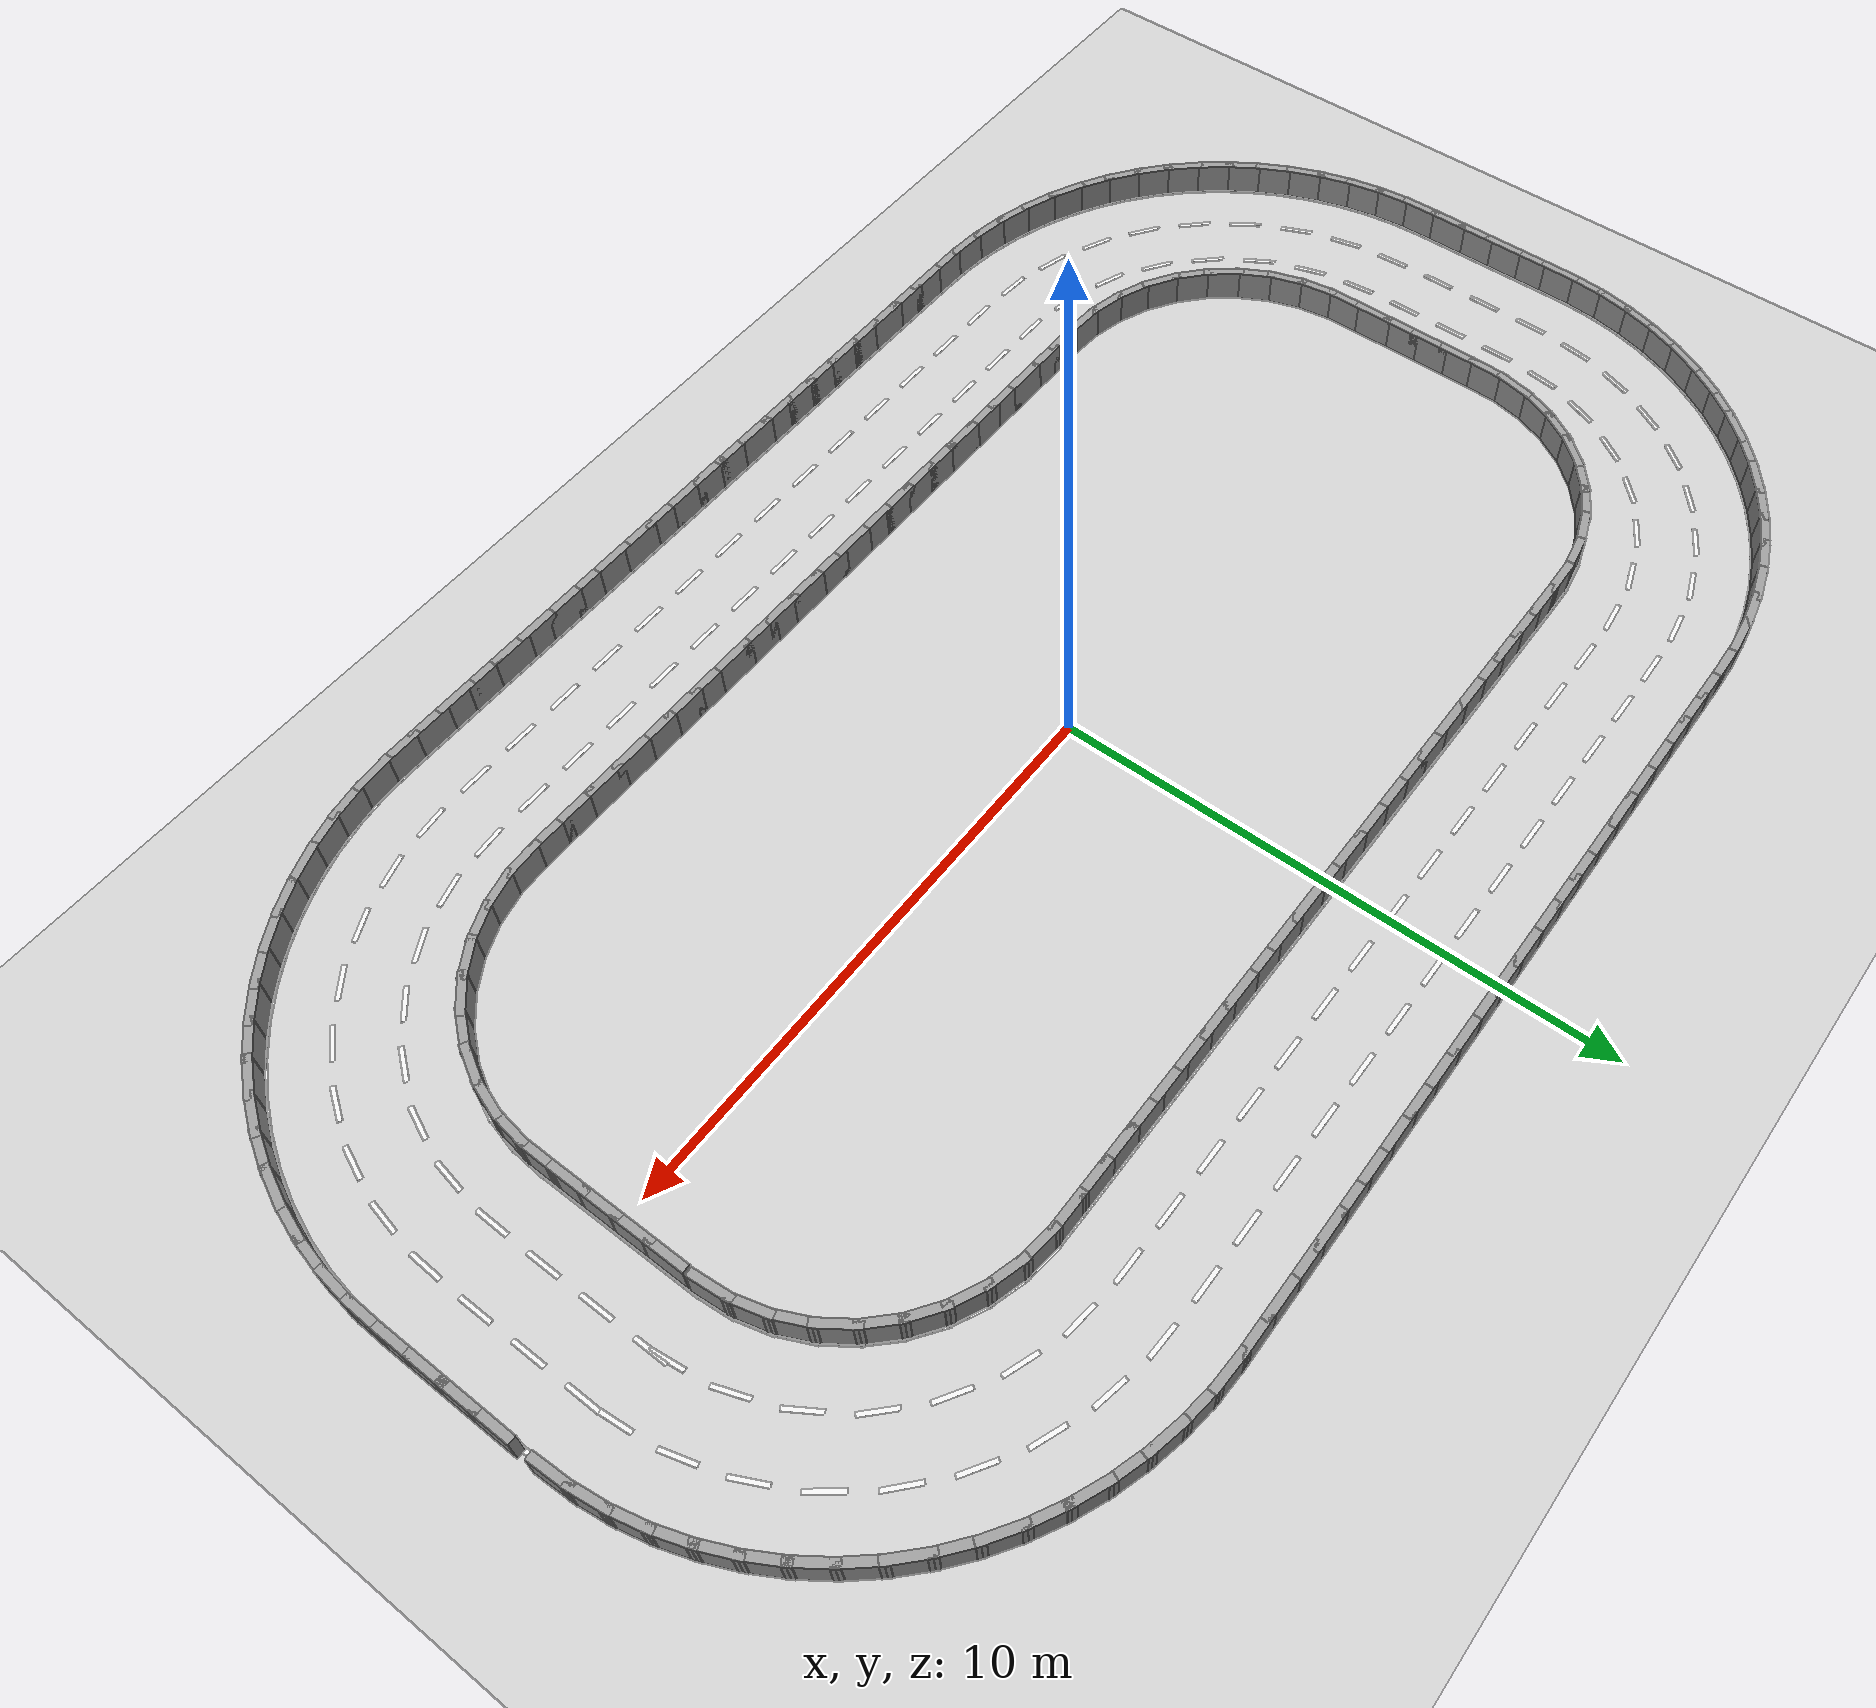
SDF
<?xml version="1.0" ?>
<sdf version='1.7'>
  <world name='default'>
    <plugin name='gazebo_ros_state' filename='libgazebo_ros_state.so'>
      <ros>
        <namespace>/</namespace>
      </ros>
      <update_rate>1000.0</update_rate>
    </plugin>

    <light name='sun' type='directional'>
      <cast_shadows>1</cast_shadows>
      <pose>0 0 10 0 -0 0</pose>
      <diffuse>0.8 0.8 0.8 1</diffuse>
      <specular>0.2 0.2 0.2 1</specular>
      <attenuation>
        <range>1000</range>
        <constant>0.9</constant>
        <linear>0.01</linear>
        <quadratic>0.001</quadratic>
      </attenuation>
      <direction>-0.5 0.1 -0.9</direction>
      <spot>
        <inner_angle>0</inner_angle>
        <outer_angle>0</outer_angle>
        <falloff>0</falloff>
      </spot>
    </light>
    <model name='ground_plane'>
      <static>1</static>
      <link name='link'>
        <collision name='collision'>
          <geometry>
            <plane>
              <normal>0 0 1</normal>
              <size>100 100</size>
            </plane>
          </geometry>
          <surface>
            <friction>
              <ode>
                <mu>100</mu>
                <mu2>50</mu2>
              </ode>
              <torsional>
                <ode/>
              </torsional>
            </friction>
            <contact>
              <ode/>
            </contact>
            <bounce/>
          </surface>
          <max_contacts>10</max_contacts>
        </collision>
        <visual name='visual'>
          <cast_shadows>0</cast_shadows>
          <geometry>
            <plane>
              <normal>0 0 1</normal>
              <size>100 100</size>
            </plane>
          </geometry>
          <material>
            <script>
              <uri>file://media/materials/scripts/gazebo.material</uri>
              <name>Gazebo/Grey</name>
            </script>
          </material>
        </visual>
        <self_collide>0</self_collide>
        <enable_wind>0</enable_wind>
        <kinematic>0</kinematic>
      </link>
    </model>
    <gravity>0 0 -9.8</gravity>
    <magnetic_field>6e-06 2.3e-05 -4.2e-05</magnetic_field>
    <atmosphere type='adiabatic'/>
    <physics type='ode'>
      <max_step_size>0.001</max_step_size>
      <real_time_factor>1</real_time_factor>
      <real_time_update_rate>1000</real_time_update_rate>
    </physics>
    <scene>
      <ambient>0.4 0.4 0.4 1</ambient>
      <background>0.7 0.7 0.7 1</background>
      <shadows>1</shadows>
    </scene>
    <audio>
      <device>default</device>
    </audio>
    <wind/>
    <spherical_coordinates>
      <surface_model>EARTH_WGS84</surface_model>
      <latitude_deg>0</latitude_deg>
      <longitude_deg>0</longitude_deg>
      <elevation>0</elevation>
      <heading_deg>0</heading_deg>
    </spherical_coordinates>
  <model name='superspeedway'>
    <pose>0 0 0 0 -0 0</pose>
    <link name='Wall_0'>
      <collision name='Wall_0_Collision'>
        <geometry><box><size>0.7493 0.1500 0.6000</size></box></geometry>
        <pose>0 0 0.3000 0 -0 0</pose>
      </collision>
      <visual name='Wall_0_Visual'>
        <pose>0 0 0.3000 0 -0 0</pose>
        <geometry><box><size>0.7493 0.1500 0.6000</size></box></geometry>
        <material>
          <script>
            <uri>file://media/materials/scripts/gazebo.material</uri>
            <name>Gazebo/Grey</name>
          </script>
          <ambient>1 1 1 1</ambient>
        </material>
      </visual>
      <pose>10.4743 1.7985 0 0 -0 1.65651</pose>
    </link>
    <link name='Wall_1'>
      <collision name='Wall_1_Collision'>
        <geometry><box><size>0.7493 0.1500 0.6000</size></box></geometry>
        <pose>0 0 0.3000 0 -0 0</pose>
      </collision>
      <visual name='Wall_1_Visual'>
        <pose>0 0 0.3000 0 -0 0</pose>
        <geometry><box><size>0.7493 0.1500 0.6000</size></box></geometry>
        <material>
          <script>
            <uri>file://media/materials/scripts/gazebo.material</uri>
            <name>Gazebo/Grey</name>
          </script>
          <ambient>1 1 1 1</ambient>
        </material>
      </visual>
      <pose>10.3725 2.3868 0 0 -0 1.82794</pose>
    </link>
    <link name='Wall_2'>
      <collision name='Wall_2_Collision'>
        <geometry><box><size>0.7493 0.1500 0.6000</size></box></geometry>
        <pose>0 0 0.3000 0 -0 0</pose>
      </collision>
      <visual name='Wall_2_Visual'>
        <pose>0 0 0.3000 0 -0 0</pose>
        <geometry><box><size>0.7493 0.1500 0.6000</size></box></geometry>
        <material>
          <script>
            <uri>file://media/materials/scripts/gazebo.material</uri>
            <name>Gazebo/Grey</name>
          </script>
          <ambient>1 1 1 1</ambient>
        </material>
      </visual>
      <pose>10.1718 2.9491 0 0 -0 1.99936</pose>
    </link>
    <link name='Wall_3'>
      <collision name='Wall_3_Collision'>
        <geometry><box><size>0.7493 0.1500 0.6000</size></box></geometry>
        <pose>0 0 0.3000 0 -0 0</pose>
      </collision>
      <visual name='Wall_3_Visual'>
        <pose>0 0 0.3000 0 -0 0</pose>
        <geometry><box><size>0.7493 0.1500 0.6000</size></box></geometry>
        <material>
          <script>
            <uri>file://media/materials/scripts/gazebo.material</uri>
            <name>Gazebo/Grey</name>
          </script>
          <ambient>1 1 1 1</ambient>
        </material>
      </visual>
      <pose>9.8781 3.4690 0 0 -0 2.17079</pose>
    </link>
    <link name='Wall_4'>
      <collision name='Wall_4_Collision'>
        <geometry><box><size>0.7493 0.1500 0.6000</size></box></geometry>
        <pose>0 0 0.3000 0 -0 0</pose>
      </collision>
      <visual name='Wall_4_Visual'>
        <pose>0 0 0.3000 0 -0 0</pose>
        <geometry><box><size>0.7493 0.1500 0.6000</size></box></geometry>
        <material>
          <script>
            <uri>file://media/materials/scripts/gazebo.material</uri>
            <name>Gazebo/Grey</name>
          </script>
          <ambient>1 1 1 1</ambient>
        </material>
      </visual>
      <pose>9.5000 3.9311 0 0 -0 2.34222</pose>
    </link>
    <link name='Wall_5'>
      <collision name='Wall_5_Collision'>
        <geometry><box><size>0.7493 0.1500 0.6000</size></box></geometry>
        <pose>0 0 0.3000 0 -0 0</pose>
      </collision>
      <visual name='Wall_5_Visual'>
        <pose>0 0 0.3000 0 -0 0</pose>
        <geometry><box><size>0.7493 0.1500 0.6000</size></box></geometry>
        <material>
          <script>
            <uri>file://media/materials/scripts/gazebo.material</uri>
            <name>Gazebo/Grey</name>
          </script>
          <ambient>1 1 1 1</ambient>
        </material>
      </visual>
      <pose>9.0486 4.3219 0 0 -0 2.51365</pose>
    </link>
    <link name='Wall_6'>
      <collision name='Wall_6_Collision'>
        <geometry><box><size>0.7493 0.1500 0.6000</size></box></geometry>
        <pose>0 0 0.3000 0 -0 0</pose>
      </collision>
      <visual name='Wall_6_Visual'>
        <pose>0 0 0.3000 0 -0 0</pose>
        <geometry><box><size>0.7493 0.1500 0.6000</size></box></geometry>
        <material>
          <script>
            <uri>file://media/materials/scripts/gazebo.material</uri>
            <name>Gazebo/Grey</name>
          </script>
          <ambient>1 1 1 1</ambient>
        </material>
      </visual>
      <pose>8.5372 4.6300 0 0 -0 2.68508</pose>
    </link>
    <link name='Wall_7'>
      <collision name='Wall_7_Collision'>
        <geometry><box><size>0.7493 0.1500 0.6000</size></box></geometry>
        <pose>0 0 0.3000 0 -0 0</pose>
      </collision>
      <visual name='Wall_7_Visual'>
        <pose>0 0 0.3000 0 -0 0</pose>
        <geometry><box><size>0.7493 0.1500 0.6000</size></box></geometry>
        <material>
          <script>
            <uri>file://media/materials/scripts/gazebo.material</uri>
            <name>Gazebo/Grey</name>
          </script>
          <ambient>1 1 1 1</ambient>
        </material>
      </visual>
      <pose>7.9807 4.8464 0 0 -0 2.85650</pose>
    </link>
    <link name='Wall_8'>
      <collision name='Wall_8_Collision'>
        <geometry><box><size>0.7493 0.1500 0.6000</size></box></geometry>
        <pose>0 0 0.3000 0 -0 0</pose>
      </collision>
      <visual name='Wall_8_Visual'>
        <pose>0 0 0.3000 0 -0 0</pose>
        <geometry><box><size>0.7493 0.1500 0.6000</size></box></geometry>
        <material>
          <script>
            <uri>file://media/materials/scripts/gazebo.material</uri>
            <name>Gazebo/Grey</name>
          </script>
          <ambient>1 1 1 1</ambient>
        </material>
      </visual>
      <pose>7.3955 4.9646 0 0 -0 3.02793</pose>
    </link>
    <link name='Wall_9'>
      <collision name='Wall_9_Collision'>
        <geometry><box><size>0.7500 0.1500 0.6000</size></box></geometry>
        <pose>0 0 0.3000 0 -0 0</pose>
      </collision>
      <visual name='Wall_9_Visual'>
        <pose>0 0 0.3000 0 -0 0</pose>
        <geometry><box><size>0.7500 0.1500 0.6000</size></box></geometry>
        <material>
          <script>
            <uri>file://media/materials/scripts/gazebo.material</uri>
            <name>Gazebo/Grey</name>
          </script>
          <ambient>1 1 1 1</ambient>
        </material>
      </visual>
      <pose>6.7978 4.9993 0 0 -0 3.13931</pose>
    </link>
    <link name='Wall_10'>
      <collision name='Wall_10_Collision'>
        <geometry><box><size>0.7500 0.1500 0.6000</size></box></geometry>
        <pose>0 0 0.3000 0 -0 0</pose>
      </collision>
      <visual name='Wall_10_Visual'>
        <pose>0 0 0.3000 0 -0 0</pose>
        <geometry><box><size>0.7500 0.1500 0.6000</size></box></geometry>
        <material>
          <script>
            <uri>file://media/materials/scripts/gazebo.material</uri>
            <name>Gazebo/Grey</name>
          </script>
          <ambient>1 1 1 1</ambient>
        </material>
      </visual>
      <pose>6.1978 5.0000 0 0 -0 3.14159</pose>
    </link>
    <link name='Wall_11'>
      <collision name='Wall_11_Collision'>
        <geometry><box><size>0.7500 0.1500 0.6000</size></box></geometry>
        <pose>0 0 0.3000 0 -0 0</pose>
      </collision>
      <visual name='Wall_11_Visual'>
        <pose>0 0 0.3000 0 -0 0</pose>
        <geometry><box><size>0.7500 0.1500 0.6000</size></box></geometry>
        <material>
          <script>
            <uri>file://media/materials/scripts/gazebo.material</uri>
            <name>Gazebo/Grey</name>
          </script>
          <ambient>1 1 1 1</ambient>
        </material>
      </visual>
      <pose>5.5978 5.0000 0 0 -0 3.14159</pose>
    </link>
    <link name='Wall_12'>
      <collision name='Wall_12_Collision'>
        <geometry><box><size>0.7500 0.1500 0.6000</size></box></geometry>
        <pose>0 0 0.3000 0 -0 0</pose>
      </collision>
      <visual name='Wall_12_Visual'>
        <pose>0 0 0.3000 0 -0 0</pose>
        <geometry><box><size>0.7500 0.1500 0.6000</size></box></geometry>
        <material>
          <script>
            <uri>file://media/materials/scripts/gazebo.material</uri>
            <name>Gazebo/Grey</name>
          </script>
          <ambient>1 1 1 1</ambient>
        </material>
      </visual>
      <pose>4.9978 5.0000 0 0 -0 3.14159</pose>
    </link>
    <link name='Wall_13'>
      <collision name='Wall_13_Collision'>
        <geometry><box><size>0.7500 0.1500 0.6000</size></box></geometry>
        <pose>0 0 0.3000 0 -0 0</pose>
      </collision>
      <visual name='Wall_13_Visual'>
        <pose>0 0 0.3000 0 -0 0</pose>
        <geometry><box><size>0.7500 0.1500 0.6000</size></box></geometry>
        <material>
          <script>
            <uri>file://media/materials/scripts/gazebo.material</uri>
            <name>Gazebo/Grey</name>
          </script>
          <ambient>1 1 1 1</ambient>
        </material>
      </visual>
      <pose>4.3978 5.0000 0 0 -0 3.14159</pose>
    </link>
    <link name='Wall_14'>
      <collision name='Wall_14_Collision'>
        <geometry><box><size>0.7500 0.1500 0.6000</size></box></geometry>
        <pose>0 0 0.3000 0 -0 0</pose>
      </collision>
      <visual name='Wall_14_Visual'>
        <pose>0 0 0.3000 0 -0 0</pose>
        <geometry><box><size>0.7500 0.1500 0.6000</size></box></geometry>
        <material>
          <script>
            <uri>file://media/materials/scripts/gazebo.material</uri>
            <name>Gazebo/Grey</name>
          </script>
          <ambient>1 1 1 1</ambient>
        </material>
      </visual>
      <pose>3.7978 5.0000 0 0 -0 3.14159</pose>
    </link>
    <link name='Wall_15'>
      <collision name='Wall_15_Collision'>
        <geometry><box><size>0.7500 0.1500 0.6000</size></box></geometry>
        <pose>0 0 0.3000 0 -0 0</pose>
      </collision>
      <visual name='Wall_15_Visual'>
        <pose>0 0 0.3000 0 -0 0</pose>
        <geometry><box><size>0.7500 0.1500 0.6000</size></box></geometry>
        <material>
          <script>
            <uri>file://media/materials/scripts/gazebo.material</uri>
            <name>Gazebo/Grey</name>
          </script>
          <ambient>1 1 1 1</ambient>
        </material>
      </visual>
      <pose>3.1978 5.0000 0 0 -0 3.14159</pose>
    </link>
    <link name='Wall_16'>
      <collision name='Wall_16_Collision'>
        <geometry><box><size>0.7500 0.1500 0.6000</size></box></geometry>
        <pose>0 0 0.3000 0 -0 0</pose>
      </collision>
      <visual name='Wall_16_Visual'>
        <pose>0 0 0.3000 0 -0 0</pose>
        <geometry><box><size>0.7500 0.1500 0.6000</size></box></geometry>
        <material>
          <script>
            <uri>file://media/materials/scripts/gazebo.material</uri>
            <name>Gazebo/Grey</name>
          </script>
          <ambient>1 1 1 1</ambient>
        </material>
      </visual>
      <pose>2.5978 5.0000 0 0 -0 3.14159</pose>
    </link>
    <link name='Wall_17'>
      <collision name='Wall_17_Collision'>
        <geometry><box><size>0.7500 0.1500 0.6000</size></box></geometry>
        <pose>0 0 0.3000 0 -0 0</pose>
      </collision>
      <visual name='Wall_17_Visual'>
        <pose>0 0 0.3000 0 -0 0</pose>
        <geometry><box><size>0.7500 0.1500 0.6000</size></box></geometry>
        <material>
          <script>
            <uri>file://media/materials/scripts/gazebo.material</uri>
            <name>Gazebo/Grey</name>
          </script>
          <ambient>1 1 1 1</ambient>
        </material>
      </visual>
      <pose>1.9978 5.0000 0 0 -0 3.14159</pose>
    </link>
    <link name='Wall_18'>
      <collision name='Wall_18_Collision'>
        <geometry><box><size>0.7500 0.1500 0.6000</size></box></geometry>
        <pose>0 0 0.3000 0 -0 0</pose>
      </collision>
      <visual name='Wall_18_Visual'>
        <pose>0 0 0.3000 0 -0 0</pose>
        <geometry><box><size>0.7500 0.1500 0.6000</size></box></geometry>
        <material>
          <script>
            <uri>file://media/materials/scripts/gazebo.material</uri>
            <name>Gazebo/Grey</name>
          </script>
          <ambient>1 1 1 1</ambient>
        </material>
      </visual>
      <pose>1.3978 5.0000 0 0 -0 3.14159</pose>
    </link>
    <link name='Wall_19'>
      <collision name='Wall_19_Collision'>
        <geometry><box><size>0.7500 0.1500 0.6000</size></box></geometry>
        <pose>0 0 0.3000 0 -0 0</pose>
      </collision>
      <visual name='Wall_19_Visual'>
        <pose>0 0 0.3000 0 -0 0</pose>
        <geometry><box><size>0.7500 0.1500 0.6000</size></box></geometry>
        <material>
          <script>
            <uri>file://media/materials/scripts/gazebo.material</uri>
            <name>Gazebo/Grey</name>
          </script>
          <ambient>1 1 1 1</ambient>
        </material>
      </visual>
      <pose>0.7978 5.0000 0 0 -0 3.14159</pose>
    </link>
    <link name='Wall_20'>
      <collision name='Wall_20_Collision'>
        <geometry><box><size>0.7500 0.1500 0.6000</size></box></geometry>
        <pose>0 0 0.3000 0 -0 0</pose>
      </collision>
      <visual name='Wall_20_Visual'>
        <pose>0 0 0.3000 0 -0 0</pose>
        <geometry><box><size>0.7500 0.1500 0.6000</size></box></geometry>
        <material>
          <script>
            <uri>file://media/materials/scripts/gazebo.material</uri>
            <name>Gazebo/Grey</name>
          </script>
          <ambient>1 1 1 1</ambient>
        </material>
      </visual>
      <pose>0.1978 5.0000 0 0 -0 3.14159</pose>
    </link>
    <link name='Wall_21'>
      <collision name='Wall_21_Collision'>
        <geometry><box><size>0.7500 0.1500 0.6000</size></box></geometry>
        <pose>0 0 0.3000 0 -0 0</pose>
      </collision>
      <visual name='Wall_21_Visual'>
        <pose>0 0 0.3000 0 -0 0</pose>
        <geometry><box><size>0.7500 0.1500 0.6000</size></box></geometry>
        <material>
          <script>
            <uri>file://media/materials/scripts/gazebo.material</uri>
            <name>Gazebo/Grey</name>
          </script>
          <ambient>1 1 1 1</ambient>
        </material>
      </visual>
      <pose>-0.4022 5.0000 0 0 -0 3.14159</pose>
    </link>
    <link name='Wall_22'>
      <collision name='Wall_22_Collision'>
        <geometry><box><size>0.7500 0.1500 0.6000</size></box></geometry>
        <pose>0 0 0.3000 0 -0 0</pose>
      </collision>
      <visual name='Wall_22_Visual'>
        <pose>0 0 0.3000 0 -0 0</pose>
        <geometry><box><size>0.7500 0.1500 0.6000</size></box></geometry>
        <material>
          <script>
            <uri>file://media/materials/scripts/gazebo.material</uri>
            <name>Gazebo/Grey</name>
          </script>
          <ambient>1 1 1 1</ambient>
        </material>
      </visual>
      <pose>-1.0022 5.0000 0 0 -0 3.14159</pose>
    </link>
    <link name='Wall_23'>
      <collision name='Wall_23_Collision'>
        <geometry><box><size>0.7500 0.1500 0.6000</size></box></geometry>
        <pose>0 0 0.3000 0 -0 0</pose>
      </collision>
      <visual name='Wall_23_Visual'>
        <pose>0 0 0.3000 0 -0 0</pose>
        <geometry><box><size>0.7500 0.1500 0.6000</size></box></geometry>
        <material>
          <script>
            <uri>file://media/materials/scripts/gazebo.material</uri>
            <name>Gazebo/Grey</name>
          </script>
          <ambient>1 1 1 1</ambient>
        </material>
      </visual>
      <pose>-1.6022 5.0000 0 0 -0 3.14159</pose>
    </link>
    <link name='Wall_24'>
      <collision name='Wall_24_Collision'>
        <geometry><box><size>0.7500 0.1500 0.6000</size></box></geometry>
        <pose>0 0 0.3000 0 -0 0</pose>
      </collision>
      <visual name='Wall_24_Visual'>
        <pose>0 0 0.3000 0 -0 0</pose>
        <geometry><box><size>0.7500 0.1500 0.6000</size></box></geometry>
        <material>
          <script>
            <uri>file://media/materials/scripts/gazebo.material</uri>
            <name>Gazebo/Grey</name>
          </script>
          <ambient>1 1 1 1</ambient>
        </material>
      </visual>
      <pose>-2.2022 5.0000 0 0 -0 3.14159</pose>
    </link>
    <link name='Wall_25'>
      <collision name='Wall_25_Collision'>
        <geometry><box><size>0.7500 0.1500 0.6000</size></box></geometry>
        <pose>0 0 0.3000 0 -0 0</pose>
      </collision>
      <visual name='Wall_25_Visual'>
        <pose>0 0 0.3000 0 -0 0</pose>
        <geometry><box><size>0.7500 0.1500 0.6000</size></box></geometry>
        <material>
          <script>
            <uri>file://media/materials/scripts/gazebo.material</uri>
            <name>Gazebo/Grey</name>
          </script>
          <ambient>1 1 1 1</ambient>
        </material>
      </visual>
      <pose>-2.8022 5.0000 0 0 -0 3.14159</pose>
    </link>
    <link name='Wall_26'>
      <collision name='Wall_26_Collision'>
        <geometry><box><size>0.7500 0.1500 0.6000</size></box></geometry>
        <pose>0 0 0.3000 0 -0 0</pose>
      </collision>
      <visual name='Wall_26_Visual'>
        <pose>0 0 0.3000 0 -0 0</pose>
        <geometry><box><size>0.7500 0.1500 0.6000</size></box></geometry>
        <material>
          <script>
            <uri>file://media/materials/scripts/gazebo.material</uri>
            <name>Gazebo/Grey</name>
          </script>
          <ambient>1 1 1 1</ambient>
        </material>
      </visual>
      <pose>-3.4022 5.0000 0 0 -0 3.14159</pose>
    </link>
    <link name='Wall_27'>
      <collision name='Wall_27_Collision'>
        <geometry><box><size>0.7500 0.1500 0.6000</size></box></geometry>
        <pose>0 0 0.3000 0 -0 0</pose>
      </collision>
      <visual name='Wall_27_Visual'>
        <pose>0 0 0.3000 0 -0 0</pose>
        <geometry><box><size>0.7500 0.1500 0.6000</size></box></geometry>
        <material>
          <script>
            <uri>file://media/materials/scripts/gazebo.material</uri>
            <name>Gazebo/Grey</name>
          </script>
          <ambient>1 1 1 1</ambient>
        </material>
      </visual>
      <pose>-4.0022 5.0000 0 0 -0 3.14159</pose>
    </link>
    <link name='Wall_28'>
      <collision name='Wall_28_Collision'>
        <geometry><box><size>0.7500 0.1500 0.6000</size></box></geometry>
        <pose>0 0 0.3000 0 -0 0</pose>
      </collision>
      <visual name='Wall_28_Visual'>
        <pose>0 0 0.3000 0 -0 0</pose>
        <geometry><box><size>0.7500 0.1500 0.6000</size></box></geometry>
        <material>
          <script>
            <uri>file://media/materials/scripts/gazebo.material</uri>
            <name>Gazebo/Grey</name>
          </script>
          <ambient>1 1 1 1</ambient>
        </material>
      </visual>
      <pose>-4.6022 5.0000 0 0 -0 3.14159</pose>
    </link>
    <link name='Wall_29'>
      <collision name='Wall_29_Collision'>
        <geometry><box><size>0.7500 0.1500 0.6000</size></box></geometry>
        <pose>0 0 0.3000 0 -0 0</pose>
      </collision>
      <visual name='Wall_29_Visual'>
        <pose>0 0 0.3000 0 -0 0</pose>
        <geometry><box><size>0.7500 0.1500 0.6000</size></box></geometry>
        <material>
          <script>
            <uri>file://media/materials/scripts/gazebo.material</uri>
            <name>Gazebo/Grey</name>
          </script>
          <ambient>1 1 1 1</ambient>
        </material>
      </visual>
      <pose>-5.2022 5.0000 0 0 -0 3.14159</pose>
    </link>
    <link name='Wall_30'>
      <collision name='Wall_30_Collision'>
        <geometry><box><size>0.7500 0.1500 0.6000</size></box></geometry>
        <pose>0 0 0.3000 0 -0 0</pose>
      </collision>
      <visual name='Wall_30_Visual'>
        <pose>0 0 0.3000 0 -0 0</pose>
        <geometry><box><size>0.7500 0.1500 0.6000</size></box></geometry>
        <material>
          <script>
            <uri>file://media/materials/scripts/gazebo.material</uri>
            <name>Gazebo/Grey</name>
          </script>
          <ambient>1 1 1 1</ambient>
        </material>
      </visual>
      <pose>-5.8022 5.0000 0 0 -0 3.14159</pose>
    </link>
    <link name='Wall_31'>
      <collision name='Wall_31_Collision'>
        <geometry><box><size>0.7500 0.1500 0.6000</size></box></geometry>
        <pose>0 0 0.3000 0 -0 0</pose>
      </collision>
      <visual name='Wall_31_Visual'>
        <pose>0 0 0.3000 0 -0 0</pose>
        <geometry><box><size>0.7500 0.1500 0.6000</size></box></geometry>
        <material>
          <script>
            <uri>file://media/materials/scripts/gazebo.material</uri>
            <name>Gazebo/Grey</name>
          </script>
          <ambient>1 1 1 1</ambient>
        </material>
      </visual>
      <pose>-6.4022 5.0000 0 0 -0 3.14159</pose>
    </link>
    <link name='Wall_32'>
      <collision name='Wall_32_Collision'>
        <geometry><box><size>0.7498 0.1500 0.6000</size></box></geometry>
        <pose>0 0 0.3000 0 -0 0</pose>
      </collision>
      <visual name='Wall_32_Visual'>
        <pose>0 0 0.3000 0 -0 0</pose>
        <geometry><box><size>0.7498 0.1500 0.6000</size></box></geometry>
        <material>
          <script>
            <uri>file://media/materials/scripts/gazebo.material</uri>
            <name>Gazebo/Grey</name>
          </script>
          <ambient>1 1 1 1</ambient>
        </material>
      </visual>
      <pose>-7.0020 4.9935 0 0 -0 -3.11984</pose>
    </link>
    <link name='Wall_33'>
      <collision name='Wall_33_Collision'>
        <geometry><box><size>0.7493 0.1500 0.6000</size></box></geometry>
        <pose>0 0 0.3000 0 -0 0</pose>
      </collision>
      <visual name='Wall_33_Visual'>
        <pose>0 0 0.3000 0 -0 0</pose>
        <geometry><box><size>0.7493 0.1500 0.6000</size></box></geometry>
        <material>
          <script>
            <uri>file://media/materials/scripts/gazebo.material</uri>
            <name>Gazebo/Grey</name>
          </script>
          <ambient>1 1 1 1</ambient>
        </material>
      </visual>
      <pose>-7.5970 4.9357 0 0 -0 -2.96953</pose>
    </link>
    <link name='Wall_34'>
      <collision name='Wall_34_Collision'>
        <geometry><box><size>0.7493 0.1500 0.6000</size></box></geometry>
        <pose>0 0 0.3000 0 -0 0</pose>
      </collision>
      <visual name='Wall_34_Visual'>
        <pose>0 0 0.3000 0 -0 0</pose>
        <geometry><box><size>0.7493 0.1500 0.6000</size></box></geometry>
        <material>
          <script>
            <uri>file://media/materials/scripts/gazebo.material</uri>
            <name>Gazebo/Grey</name>
          </script>
          <ambient>1 1 1 1</ambient>
        </material>
      </visual>
      <pose>-8.1744 4.7834 0 0 -0 -2.79811</pose>
    </link>
    <link name='Wall_35'>
      <collision name='Wall_35_Collision'>
        <geometry><box><size>0.7493 0.1500 0.6000</size></box></geometry>
        <pose>0 0 0.3000 0 -0 0</pose>
      </collision>
      <visual name='Wall_35_Visual'>
        <pose>0 0 0.3000 0 -0 0</pose>
        <geometry><box><size>0.7493 0.1500 0.6000</size></box></geometry>
        <material>
          <script>
            <uri>file://media/materials/scripts/gazebo.material</uri>
            <name>Gazebo/Grey</name>
          </script>
          <ambient>1 1 1 1</ambient>
        </material>
      </visual>
      <pose>-8.7173 4.5350 0 0 -0 -2.62668</pose>
    </link>
    <link name='Wall_36'>
      <collision name='Wall_36_Collision'>
        <geometry><box><size>0.7493 0.1500 0.6000</size></box></geometry>
        <pose>0 0 0.3000 0 -0 0</pose>
      </collision>
      <visual name='Wall_36_Visual'>
        <pose>0 0 0.3000 0 -0 0</pose>
        <geometry><box><size>0.7493 0.1500 0.6000</size></box></geometry>
        <material>
          <script>
            <uri>file://media/materials/scripts/gazebo.material</uri>
            <name>Gazebo/Grey</name>
          </script>
          <ambient>1 1 1 1</ambient>
        </material>
      </visual>
      <pose>-9.2098 4.1975 0 0 -0 -2.45525</pose>
    </link>
    <link name='Wall_37'>
      <collision name='Wall_37_Collision'>
        <geometry><box><size>0.7493 0.1500 0.6000</size></box></geometry>
        <pose>0 0 0.3000 0 -0 0</pose>
      </collision>
      <visual name='Wall_37_Visual'>
        <pose>0 0 0.3000 0 -0 0</pose>
        <geometry><box><size>0.7493 0.1500 0.6000</size></box></geometry>
        <material>
          <script>
            <uri>file://media/materials/scripts/gazebo.material</uri>
            <name>Gazebo/Grey</name>
          </script>
          <ambient>1 1 1 1</ambient>
        </material>
      </visual>
      <pose>-9.6376 3.7810 0 0 -0 -2.28382</pose>
    </link>
    <link name='Wall_38'>
      <collision name='Wall_38_Collision'>
        <geometry><box><size>0.7493 0.1500 0.6000</size></box></geometry>
        <pose>0 0 0.3000 0 -0 0</pose>
      </collision>
      <visual name='Wall_38_Visual'>
        <pose>0 0 0.3000 0 -0 0</pose>
        <geometry><box><size>0.7493 0.1500 0.6000</size></box></geometry>
        <material>
          <script>
            <uri>file://media/materials/scripts/gazebo.material</uri>
            <name>Gazebo/Grey</name>
          </script>
          <ambient>1 1 1 1</ambient>
        </material>
      </visual>
      <pose>-9.9881 3.2976 0 0 -0 -2.11240</pose>
    </link>
    <link name='Wall_39'>
      <collision name='Wall_39_Collision'>
        <geometry><box><size>0.7493 0.1500 0.6000</size></box></geometry>
        <pose>0 0 0.3000 0 -0 0</pose>
      </collision>
      <visual name='Wall_39_Visual'>
        <pose>0 0 0.3000 0 -0 0</pose>
        <geometry><box><size>0.7493 0.1500 0.6000</size></box></geometry>
        <material>
          <script>
            <uri>file://media/materials/scripts/gazebo.material</uri>
            <name>Gazebo/Grey</name>
          </script>
          <ambient>1 1 1 1</ambient>
        </material>
      </visual>
      <pose>-10.2509 2.7616 0 0 -0 -1.94097</pose>
    </link>
    <link name='Wall_40'>
      <collision name='Wall_40_Collision'>
        <geometry><box><size>0.7493 0.1500 0.6000</size></box></geometry>
        <pose>0 0 0.3000 0 -0 0</pose>
      </collision>
      <visual name='Wall_40_Visual'>
        <pose>0 0 0.3000 0 -0 0</pose>
        <geometry><box><size>0.7493 0.1500 0.6000</size></box></geometry>
        <material>
          <script>
            <uri>file://media/materials/scripts/gazebo.material</uri>
            <name>Gazebo/Grey</name>
          </script>
          <ambient>1 1 1 1</ambient>
        </material>
      </visual>
      <pose>-10.4185 2.1885 0 0 -0 -1.76954</pose>
    </link>
    <link name='Wall_41'>
      <collision name='Wall_41_Collision'>
        <geometry><box><size>0.7496 0.1500 0.6000</size></box></geometry>
        <pose>0 0 0.3000 0 -0 0</pose>
      </collision>
      <visual name='Wall_41_Visual'>
        <pose>0 0 0.3000 0 -0 0</pose>
        <geometry><box><size>0.7496 0.1500 0.6000</size></box></geometry>
        <material>
          <script>
            <uri>file://media/materials/scripts/gazebo.material</uri>
            <name>Gazebo/Grey</name>
          </script>
          <ambient>1 1 1 1</ambient>
        </material>
      </visual>
      <pose>-10.4888 1.5952 0 0 -0 -1.60806</pose>
    </link>
    <link name='Wall_42'>
      <collision name='Wall_42_Collision'>
        <geometry><box><size>0.7500 0.1500 0.6000</size></box></geometry>
        <pose>0 0 0.3000 0 -0 0</pose>
      </collision>
      <visual name='Wall_42_Visual'>
        <pose>0 0 0.3000 0 -0 0</pose>
        <geometry><box><size>0.7500 0.1500 0.6000</size></box></geometry>
        <material>
          <script>
            <uri>file://media/materials/scripts/gazebo.material</uri>
            <name>Gazebo/Grey</name>
          </script>
          <ambient>1 1 1 1</ambient>
        </material>
      </visual>
      <pose>-10.5000 0.9956 0 0 -0 -1.57080</pose>
    </link>
    <link name='Wall_43'>
      <collision name='Wall_43_Collision'>
        <geometry><box><size>0.7500 0.1500 0.6000</size></box></geometry>
        <pose>0 0 0.3000 0 -0 0</pose>
      </collision>
      <visual name='Wall_43_Visual'>
        <pose>0 0 0.3000 0 -0 0</pose>
        <geometry><box><size>0.7500 0.1500 0.6000</size></box></geometry>
        <material>
          <script>
            <uri>file://media/materials/scripts/gazebo.material</uri>
            <name>Gazebo/Grey</name>
          </script>
          <ambient>1 1 1 1</ambient>
        </material>
      </visual>
      <pose>-10.5000 0.3956 0 0 -0 -1.57080</pose>
    </link>
    <link name='Wall_44'>
      <collision name='Wall_44_Collision'>
        <geometry><box><size>0.7500 0.1500 0.6000</size></box></geometry>
        <pose>0 0 0.3000 0 -0 0</pose>
      </collision>
      <visual name='Wall_44_Visual'>
        <pose>0 0 0.3000 0 -0 0</pose>
        <geometry><box><size>0.7500 0.1500 0.6000</size></box></geometry>
        <material>
          <script>
            <uri>file://media/materials/scripts/gazebo.material</uri>
            <name>Gazebo/Grey</name>
          </script>
          <ambient>1 1 1 1</ambient>
        </material>
      </visual>
      <pose>-10.5000 -0.2044 0 0 -0 -1.57080</pose>
    </link>
    <link name='Wall_45'>
      <collision name='Wall_45_Collision'>
        <geometry><box><size>0.7500 0.1500 0.6000</size></box></geometry>
        <pose>0 0 0.3000 0 -0 0</pose>
      </collision>
      <visual name='Wall_45_Visual'>
        <pose>0 0 0.3000 0 -0 0</pose>
        <geometry><box><size>0.7500 0.1500 0.6000</size></box></geometry>
        <material>
          <script>
            <uri>file://media/materials/scripts/gazebo.material</uri>
            <name>Gazebo/Grey</name>
          </script>
          <ambient>1 1 1 1</ambient>
        </material>
      </visual>
      <pose>-10.5000 -0.8044 0 0 -0 -1.57080</pose>
    </link>
    <link name='Wall_46'>
      <collision name='Wall_46_Collision'>
        <geometry><box><size>0.7499 0.1500 0.6000</size></box></geometry>
        <pose>0 0 0.3000 0 -0 0</pose>
      </collision>
      <visual name='Wall_46_Visual'>
        <pose>0 0 0.3000 0 -0 0</pose>
        <geometry><box><size>0.7499 0.1500 0.6000</size></box></geometry>
        <material>
          <script>
            <uri>file://media/materials/scripts/gazebo.material</uri>
            <name>Gazebo/Grey</name>
          </script>
          <ambient>1 1 1 1</ambient>
        </material>
      </visual>
      <pose>-10.4970 -1.4044 0 0 -0 -1.56085</pose>
    </link>
    <link name='Wall_47'>
      <collision name='Wall_47_Collision'>
        <geometry><box><size>0.7493 0.1500 0.6000</size></box></geometry>
        <pose>0 0 0.3000 0 -0 0</pose>
      </collision>
      <visual name='Wall_47_Visual'>
        <pose>0 0 0.3000 0 -0 0</pose>
        <geometry><box><size>0.7493 0.1500 0.6000</size></box></geometry>
        <material>
          <script>
            <uri>file://media/materials/scripts/gazebo.material</uri>
            <name>Gazebo/Grey</name>
          </script>
          <ambient>1 1 1 1</ambient>
        </material>
      </visual>
      <pose>-10.4510 -2.0008 0 0 -0 -1.42668</pose>
    </link>
    <link name='Wall_48'>
      <collision name='Wall_48_Collision'>
        <geometry><box><size>0.7493 0.1500 0.6000</size></box></geometry>
        <pose>0 0 0.3000 0 -0 0</pose>
      </collision>
      <visual name='Wall_48_Visual'>
        <pose>0 0 0.3000 0 -0 0</pose>
        <geometry><box><size>0.7493 0.1500 0.6000</size></box></geometry>
        <material>
          <script>
            <uri>file://media/materials/scripts/gazebo.material</uri>
            <name>Gazebo/Grey</name>
          </script>
          <ambient>1 1 1 1</ambient>
        </material>
      </visual>
      <pose>-10.3150 -2.5822 0 0 -0 -1.25525</pose>
    </link>
    <link name='Wall_49'>
      <collision name='Wall_49_Collision'>
        <geometry><box><size>0.7493 0.1500 0.6000</size></box></geometry>
        <pose>0 0 0.3000 0 -0 0</pose>
      </collision>
      <visual name='Wall_49_Visual'>
        <pose>0 0 0.3000 0 -0 0</pose>
        <geometry><box><size>0.7493 0.1500 0.6000</size></box></geometry>
        <material>
          <script>
            <uri>file://media/materials/scripts/gazebo.material</uri>
            <name>Gazebo/Grey</name>
          </script>
          <ambient>1 1 1 1</ambient>
        </material>
      </visual>
      <pose>-10.0818 -3.1318 0 0 -0 -1.08382</pose>
    </link>
    <link name='Wall_50'>
      <collision name='Wall_50_Collision'>
        <geometry><box><size>0.7493 0.1500 0.6000</size></box></geometry>
        <pose>0 0 0.3000 0 -0 0</pose>
      </collision>
      <visual name='Wall_50_Visual'>
        <pose>0 0 0.3000 0 -0 0</pose>
        <geometry><box><size>0.7493 0.1500 0.6000</size></box></geometry>
        <material>
          <script>
            <uri>file://media/materials/scripts/gazebo.material</uri>
            <name>Gazebo/Grey</name>
          </script>
          <ambient>1 1 1 1</ambient>
        </material>
      </visual>
      <pose>-9.7582 -3.6336 0 0 -0 -0.91239</pose>
    </link>
    <link name='Wall_51'>
      <collision name='Wall_51_Collision'>
        <geometry><box><size>0.7493 0.1500 0.6000</size></box></geometry>
        <pose>0 0 0.3000 0 -0 0</pose>
      </collision>
      <visual name='Wall_51_Visual'>
        <pose>0 0 0.3000 0 -0 0</pose>
        <geometry><box><size>0.7493 0.1500 0.6000</size></box></geometry>
        <material>
          <script>
            <uri>file://media/materials/scripts/gazebo.material</uri>
            <name>Gazebo/Grey</name>
          </script>
          <ambient>1 1 1 1</ambient>
        </material>
      </visual>
      <pose>-9.3538 -4.0729 0 0 -0 -0.74096</pose>
    </link>
    <link name='Wall_52'>
      <collision name='Wall_52_Collision'>
        <geometry><box><size>0.7493 0.1500 0.6000</size></box></geometry>
        <pose>0 0 0.3000 0 -0 0</pose>
      </collision>
      <visual name='Wall_52_Visual'>
        <pose>0 0 0.3000 0 -0 0</pose>
        <geometry><box><size>0.7493 0.1500 0.6000</size></box></geometry>
        <material>
          <script>
            <uri>file://media/materials/scripts/gazebo.material</uri>
            <name>Gazebo/Grey</name>
          </script>
          <ambient>1 1 1 1</ambient>
        </material>
      </visual>
      <pose>-8.8804 -4.4367 0 0 -0 -0.56954</pose>
    </link>
    <link name='Wall_53'>
      <collision name='Wall_53_Collision'>
        <geometry><box><size>0.7493 0.1500 0.6000</size></box></geometry>
        <pose>0 0 0.3000 0 -0 0</pose>
      </collision>
      <visual name='Wall_53_Visual'>
        <pose>0 0 0.3000 0 -0 0</pose>
        <geometry><box><size>0.7493 0.1500 0.6000</size></box></geometry>
        <material>
          <script>
            <uri>file://media/materials/scripts/gazebo.material</uri>
            <name>Gazebo/Grey</name>
          </script>
          <ambient>1 1 1 1</ambient>
        </material>
      </visual>
      <pose>-8.3519 -4.7144 0 0 -0 -0.39811</pose>
    </link>
    <link name='Wall_54'>
      <collision name='Wall_54_Collision'>
        <geometry><box><size>0.7493 0.1500 0.6000</size></box></geometry>
        <pose>0 0 0.3000 0 -0 0</pose>
      </collision>
      <visual name='Wall_54_Visual'>
        <pose>0 0 0.3000 0 -0 0</pose>
        <geometry><box><size>0.7493 0.1500 0.6000</size></box></geometry>
        <material>
          <script>
            <uri>file://media/materials/scripts/gazebo.material</uri>
            <name>Gazebo/Grey</name>
          </script>
          <ambient>1 1 1 1</ambient>
        </material>
      </visual>
      <pose>-7.7837 -4.8979 0 0 -0 -0.22668</pose>
    </link>
    <link name='Wall_55'>
      <collision name='Wall_55_Collision'>
        <geometry><box><size>0.7494 0.1500 0.6000</size></box></geometry>
        <pose>0 0 0.3000 0 -0 0</pose>
      </collision>
      <visual name='Wall_55_Visual'>
        <pose>0 0 0.3000 0 -0 0</pose>
        <geometry><box><size>0.7494 0.1500 0.6000</size></box></geometry>
        <material>
          <script>
            <uri>file://media/materials/scripts/gazebo.material</uri>
            <name>Gazebo/Grey</name>
          </script>
          <ambient>1 1 1 1</ambient>
        </material>
      </visual>
      <pose>-7.1926 -4.9826 0 0 -0 -0.05797</pose>
    </link>
    <link name='Wall_56'>
      <collision name='Wall_56_Collision'>
        <geometry><box><size>0.7500 0.1500 0.6000</size></box></geometry>
        <pose>0 0 0.3000 0 -0 0</pose>
      </collision>
      <visual name='Wall_56_Visual'>
        <pose>0 0 0.3000 0 -0 0</pose>
        <geometry><box><size>0.7500 0.1500 0.6000</size></box></geometry>
        <material>
          <script>
            <uri>file://media/materials/scripts/gazebo.material</uri>
            <name>Gazebo/Grey</name>
          </script>
          <ambient>1 1 1 1</ambient>
        </material>
      </visual>
      <pose>-6.5934 -5.0000 0 0 -0 0.00000</pose>
    </link>
    <link name='Wall_57'>
      <collision name='Wall_57_Collision'>
        <geometry><box><size>0.7500 0.1500 0.6000</size></box></geometry>
        <pose>0 0 0.3000 0 -0 0</pose>
      </collision>
      <visual name='Wall_57_Visual'>
        <pose>0 0 0.3000 0 -0 0</pose>
        <geometry><box><size>0.7500 0.1500 0.6000</size></box></geometry>
        <material>
          <script>
            <uri>file://media/materials/scripts/gazebo.material</uri>
            <name>Gazebo/Grey</name>
          </script>
          <ambient>1 1 1 1</ambient>
        </material>
      </visual>
      <pose>-5.9934 -5.0000 0 0 -0 0.00000</pose>
    </link>
    <link name='Wall_58'>
      <collision name='Wall_58_Collision'>
        <geometry><box><size>0.7500 0.1500 0.6000</size></box></geometry>
        <pose>0 0 0.3000 0 -0 0</pose>
      </collision>
      <visual name='Wall_58_Visual'>
        <pose>0 0 0.3000 0 -0 0</pose>
        <geometry><box><size>0.7500 0.1500 0.6000</size></box></geometry>
        <material>
          <script>
            <uri>file://media/materials/scripts/gazebo.material</uri>
            <name>Gazebo/Grey</name>
          </script>
          <ambient>1 1 1 1</ambient>
        </material>
      </visual>
      <pose>-5.3934 -5.0000 0 0 -0 0.00000</pose>
    </link>
    <link name='Wall_59'>
      <collision name='Wall_59_Collision'>
        <geometry><box><size>0.7500 0.1500 0.6000</size></box></geometry>
        <pose>0 0 0.3000 0 -0 0</pose>
      </collision>
      <visual name='Wall_59_Visual'>
        <pose>0 0 0.3000 0 -0 0</pose>
        <geometry><box><size>0.7500 0.1500 0.6000</size></box></geometry>
        <material>
          <script>
            <uri>file://media/materials/scripts/gazebo.material</uri>
            <name>Gazebo/Grey</name>
          </script>
          <ambient>1 1 1 1</ambient>
        </material>
      </visual>
      <pose>-4.7934 -5.0000 0 0 -0 0.00000</pose>
    </link>
    <link name='Wall_60'>
      <collision name='Wall_60_Collision'>
        <geometry><box><size>0.7500 0.1500 0.6000</size></box></geometry>
        <pose>0 0 0.3000 0 -0 0</pose>
      </collision>
      <visual name='Wall_60_Visual'>
        <pose>0 0 0.3000 0 -0 0</pose>
        <geometry><box><size>0.7500 0.1500 0.6000</size></box></geometry>
        <material>
          <script>
            <uri>file://media/materials/scripts/gazebo.material</uri>
            <name>Gazebo/Grey</name>
          </script>
          <ambient>1 1 1 1</ambient>
        </material>
      </visual>
      <pose>-4.1934 -5.0000 0 0 -0 0.00000</pose>
    </link>
    <link name='Wall_61'>
      <collision name='Wall_61_Collision'>
        <geometry><box><size>0.7500 0.1500 0.6000</size></box></geometry>
        <pose>0 0 0.3000 0 -0 0</pose>
      </collision>
      <visual name='Wall_61_Visual'>
        <pose>0 0 0.3000 0 -0 0</pose>
        <geometry><box><size>0.7500 0.1500 0.6000</size></box></geometry>
        <material>
          <script>
            <uri>file://media/materials/scripts/gazebo.material</uri>
            <name>Gazebo/Grey</name>
          </script>
          <ambient>1 1 1 1</ambient>
        </material>
      </visual>
      <pose>-3.5934 -5.0000 0 0 -0 0.00000</pose>
    </link>
    <link name='Wall_62'>
      <collision name='Wall_62_Collision'>
        <geometry><box><size>0.7500 0.1500 0.6000</size></box></geometry>
        <pose>0 0 0.3000 0 -0 0</pose>
      </collision>
      <visual name='Wall_62_Visual'>
        <pose>0 0 0.3000 0 -0 0</pose>
        <geometry><box><size>0.7500 0.1500 0.6000</size></box></geometry>
        <material>
          <script>
            <uri>file://media/materials/scripts/gazebo.material</uri>
            <name>Gazebo/Grey</name>
          </script>
          <ambient>1 1 1 1</ambient>
        </material>
      </visual>
      <pose>-2.9934 -5.0000 0 0 -0 0.00000</pose>
    </link>
    <link name='Wall_63'>
      <collision name='Wall_63_Collision'>
        <geometry><box><size>0.7500 0.1500 0.6000</size></box></geometry>
        <pose>0 0 0.3000 0 -0 0</pose>
      </collision>
      <visual name='Wall_63_Visual'>
        <pose>0 0 0.3000 0 -0 0</pose>
        <geometry><box><size>0.7500 0.1500 0.6000</size></box></geometry>
        <material>
          <script>
            <uri>file://media/materials/scripts/gazebo.material</uri>
            <name>Gazebo/Grey</name>
          </script>
          <ambient>1 1 1 1</ambient>
        </material>
      </visual>
      <pose>-2.3934 -5.0000 0 0 -0 0.00000</pose>
    </link>
    <link name='Wall_64'>
      <collision name='Wall_64_Collision'>
        <geometry><box><size>0.7500 0.1500 0.6000</size></box></geometry>
        <pose>0 0 0.3000 0 -0 0</pose>
      </collision>
      <visual name='Wall_64_Visual'>
        <pose>0 0 0.3000 0 -0 0</pose>
        <geometry><box><size>0.7500 0.1500 0.6000</size></box></geometry>
        <material>
          <script>
            <uri>file://media/materials/scripts/gazebo.material</uri>
            <name>Gazebo/Grey</name>
          </script>
          <ambient>1 1 1 1</ambient>
        </material>
      </visual>
      <pose>-1.7934 -5.0000 0 0 -0 0.00000</pose>
    </link>
    <link name='Wall_65'>
      <collision name='Wall_65_Collision'>
        <geometry><box><size>0.7500 0.1500 0.6000</size></box></geometry>
        <pose>0 0 0.3000 0 -0 0</pose>
      </collision>
      <visual name='Wall_65_Visual'>
        <pose>0 0 0.3000 0 -0 0</pose>
        <geometry><box><size>0.7500 0.1500 0.6000</size></box></geometry>
        <material>
          <script>
            <uri>file://media/materials/scripts/gazebo.material</uri>
            <name>Gazebo/Grey</name>
          </script>
          <ambient>1 1 1 1</ambient>
        </material>
      </visual>
      <pose>-1.1934 -5.0000 0 0 -0 0.00000</pose>
    </link>
    <link name='Wall_66'>
      <collision name='Wall_66_Collision'>
        <geometry><box><size>0.7500 0.1500 0.6000</size></box></geometry>
        <pose>0 0 0.3000 0 -0 0</pose>
      </collision>
      <visual name='Wall_66_Visual'>
        <pose>0 0 0.3000 0 -0 0</pose>
        <geometry><box><size>0.7500 0.1500 0.6000</size></box></geometry>
        <material>
          <script>
            <uri>file://media/materials/scripts/gazebo.material</uri>
            <name>Gazebo/Grey</name>
          </script>
          <ambient>1 1 1 1</ambient>
        </material>
      </visual>
      <pose>-0.5934 -5.0000 0 0 -0 0.00000</pose>
    </link>
    <link name='Wall_67'>
      <collision name='Wall_67_Collision'>
        <geometry><box><size>0.7500 0.1500 0.6000</size></box></geometry>
        <pose>0 0 0.3000 0 -0 0</pose>
      </collision>
      <visual name='Wall_67_Visual'>
        <pose>0 0 0.3000 0 -0 0</pose>
        <geometry><box><size>0.7500 0.1500 0.6000</size></box></geometry>
        <material>
          <script>
            <uri>file://media/materials/scripts/gazebo.material</uri>
            <name>Gazebo/Grey</name>
          </script>
          <ambient>1 1 1 1</ambient>
        </material>
      </visual>
      <pose>0.0066 -5.0000 0 0 -0 0.00000</pose>
    </link>
    <link name='Wall_68'>
      <collision name='Wall_68_Collision'>
        <geometry><box><size>0.7500 0.1500 0.6000</size></box></geometry>
        <pose>0 0 0.3000 0 -0 0</pose>
      </collision>
      <visual name='Wall_68_Visual'>
        <pose>0 0 0.3000 0 -0 0</pose>
        <geometry><box><size>0.7500 0.1500 0.6000</size></box></geometry>
        <material>
          <script>
            <uri>file://media/materials/scripts/gazebo.material</uri>
            <name>Gazebo/Grey</name>
          </script>
          <ambient>1 1 1 1</ambient>
        </material>
      </visual>
      <pose>0.6066 -5.0000 0 0 -0 0.00000</pose>
    </link>
    <link name='Wall_69'>
      <collision name='Wall_69_Collision'>
        <geometry><box><size>0.7500 0.1500 0.6000</size></box></geometry>
        <pose>0 0 0.3000 0 -0 0</pose>
      </collision>
      <visual name='Wall_69_Visual'>
        <pose>0 0 0.3000 0 -0 0</pose>
        <geometry><box><size>0.7500 0.1500 0.6000</size></box></geometry>
        <material>
          <script>
            <uri>file://media/materials/scripts/gazebo.material</uri>
            <name>Gazebo/Grey</name>
          </script>
          <ambient>1 1 1 1</ambient>
        </material>
      </visual>
      <pose>1.2066 -5.0000 0 0 -0 0.00000</pose>
    </link>
    <link name='Wall_70'>
      <collision name='Wall_70_Collision'>
        <geometry><box><size>0.7500 0.1500 0.6000</size></box></geometry>
        <pose>0 0 0.3000 0 -0 0</pose>
      </collision>
      <visual name='Wall_70_Visual'>
        <pose>0 0 0.3000 0 -0 0</pose>
        <geometry><box><size>0.7500 0.1500 0.6000</size></box></geometry>
        <material>
          <script>
            <uri>file://media/materials/scripts/gazebo.material</uri>
            <name>Gazebo/Grey</name>
          </script>
          <ambient>1 1 1 1</ambient>
        </material>
      </visual>
      <pose>1.8066 -5.0000 0 0 -0 0.00000</pose>
    </link>
    <link name='Wall_71'>
      <collision name='Wall_71_Collision'>
        <geometry><box><size>0.7500 0.1500 0.6000</size></box></geometry>
        <pose>0 0 0.3000 0 -0 0</pose>
      </collision>
      <visual name='Wall_71_Visual'>
        <pose>0 0 0.3000 0 -0 0</pose>
        <geometry><box><size>0.7500 0.1500 0.6000</size></box></geometry>
        <material>
          <script>
            <uri>file://media/materials/scripts/gazebo.material</uri>
            <name>Gazebo/Grey</name>
          </script>
          <ambient>1 1 1 1</ambient>
        </material>
      </visual>
      <pose>2.4066 -5.0000 0 0 -0 0.00000</pose>
    </link>
    <link name='Wall_72'>
      <collision name='Wall_72_Collision'>
        <geometry><box><size>0.7500 0.1500 0.6000</size></box></geometry>
        <pose>0 0 0.3000 0 -0 0</pose>
      </collision>
      <visual name='Wall_72_Visual'>
        <pose>0 0 0.3000 0 -0 0</pose>
        <geometry><box><size>0.7500 0.1500 0.6000</size></box></geometry>
        <material>
          <script>
            <uri>file://media/materials/scripts/gazebo.material</uri>
            <name>Gazebo/Grey</name>
          </script>
          <ambient>1 1 1 1</ambient>
        </material>
      </visual>
      <pose>3.0066 -5.0000 0 0 -0 0.00000</pose>
    </link>
    <link name='Wall_73'>
      <collision name='Wall_73_Collision'>
        <geometry><box><size>0.7500 0.1500 0.6000</size></box></geometry>
        <pose>0 0 0.3000 0 -0 0</pose>
      </collision>
      <visual name='Wall_73_Visual'>
        <pose>0 0 0.3000 0 -0 0</pose>
        <geometry><box><size>0.7500 0.1500 0.6000</size></box></geometry>
        <material>
          <script>
            <uri>file://media/materials/scripts/gazebo.material</uri>
            <name>Gazebo/Grey</name>
          </script>
          <ambient>1 1 1 1</ambient>
        </material>
      </visual>
      <pose>3.6066 -5.0000 0 0 -0 0.00000</pose>
    </link>
    <link name='Wall_74'>
      <collision name='Wall_74_Collision'>
        <geometry><box><size>0.7500 0.1500 0.6000</size></box></geometry>
        <pose>0 0 0.3000 0 -0 0</pose>
      </collision>
      <visual name='Wall_74_Visual'>
        <pose>0 0 0.3000 0 -0 0</pose>
        <geometry><box><size>0.7500 0.1500 0.6000</size></box></geometry>
        <material>
          <script>
            <uri>file://media/materials/scripts/gazebo.material</uri>
            <name>Gazebo/Grey</name>
          </script>
          <ambient>1 1 1 1</ambient>
        </material>
      </visual>
      <pose>4.2066 -5.0000 0 0 -0 0.00000</pose>
    </link>
    <link name='Wall_75'>
      <collision name='Wall_75_Collision'>
        <geometry><box><size>0.7500 0.1500 0.6000</size></box></geometry>
        <pose>0 0 0.3000 0 -0 0</pose>
      </collision>
      <visual name='Wall_75_Visual'>
        <pose>0 0 0.3000 0 -0 0</pose>
        <geometry><box><size>0.7500 0.1500 0.6000</size></box></geometry>
        <material>
          <script>
            <uri>file://media/materials/scripts/gazebo.material</uri>
            <name>Gazebo/Grey</name>
          </script>
          <ambient>1 1 1 1</ambient>
        </material>
      </visual>
      <pose>4.8066 -5.0000 0 0 -0 0.00000</pose>
    </link>
    <link name='Wall_76'>
      <collision name='Wall_76_Collision'>
        <geometry><box><size>0.7500 0.1500 0.6000</size></box></geometry>
        <pose>0 0 0.3000 0 -0 0</pose>
      </collision>
      <visual name='Wall_76_Visual'>
        <pose>0 0 0.3000 0 -0 0</pose>
        <geometry><box><size>0.7500 0.1500 0.6000</size></box></geometry>
        <material>
          <script>
            <uri>file://media/materials/scripts/gazebo.material</uri>
            <name>Gazebo/Grey</name>
          </script>
          <ambient>1 1 1 1</ambient>
        </material>
      </visual>
      <pose>5.4066 -5.0000 0 0 -0 0.00000</pose>
    </link>
    <link name='Wall_77'>
      <collision name='Wall_77_Collision'>
        <geometry><box><size>0.7500 0.1500 0.6000</size></box></geometry>
        <pose>0 0 0.3000 0 -0 0</pose>
      </collision>
      <visual name='Wall_77_Visual'>
        <pose>0 0 0.3000 0 -0 0</pose>
        <geometry><box><size>0.7500 0.1500 0.6000</size></box></geometry>
        <material>
          <script>
            <uri>file://media/materials/scripts/gazebo.material</uri>
            <name>Gazebo/Grey</name>
          </script>
          <ambient>1 1 1 1</ambient>
        </material>
      </visual>
      <pose>6.0066 -5.0000 0 0 -0 0.00000</pose>
    </link>
    <link name='Wall_78'>
      <collision name='Wall_78_Collision'>
        <geometry><box><size>0.7500 0.1500 0.6000</size></box></geometry>
        <pose>0 0 0.3000 0 -0 0</pose>
      </collision>
      <visual name='Wall_78_Visual'>
        <pose>0 0 0.3000 0 -0 0</pose>
        <geometry><box><size>0.7500 0.1500 0.6000</size></box></geometry>
        <material>
          <script>
            <uri>file://media/materials/scripts/gazebo.material</uri>
            <name>Gazebo/Grey</name>
          </script>
          <ambient>1 1 1 1</ambient>
        </material>
      </visual>
      <pose>6.6066 -5.0000 0 0 -0 0.00000</pose>
    </link>
    <link name='Wall_79'>
      <collision name='Wall_79_Collision'>
        <geometry><box><size>0.7494 0.1500 0.6000</size></box></geometry>
        <pose>0 0 0.3000 0 -0 0</pose>
      </collision>
      <visual name='Wall_79_Visual'>
        <pose>0 0 0.3000 0 -0 0</pose>
        <geometry><box><size>0.7494 0.1500 0.6000</size></box></geometry>
        <material>
          <script>
            <uri>file://media/materials/scripts/gazebo.material</uri>
            <name>Gazebo/Grey</name>
          </script>
          <ambient>1 1 1 1</ambient>
        </material>
      </visual>
      <pose>7.2057 -4.9817 0 0 -0 0.06112</pose>
    </link>
    <link name='Wall_80'>
      <collision name='Wall_80_Collision'>
        <geometry><box><size>0.7493 0.1500 0.6000</size></box></geometry>
        <pose>0 0 0.3000 0 -0 0</pose>
      </collision>
      <visual name='Wall_80_Visual'>
        <pose>0 0 0.3000 0 -0 0</pose>
        <geometry><box><size>0.7493 0.1500 0.6000</size></box></geometry>
        <material>
          <script>
            <uri>file://media/materials/scripts/gazebo.material</uri>
            <name>Gazebo/Grey</name>
          </script>
          <ambient>1 1 1 1</ambient>
        </material>
      </visual>
      <pose>7.7966 -4.8949 0 0 -0 0.23047</pose>
    </link>
    <link name='Wall_81'>
      <collision name='Wall_81_Collision'>
        <geometry><box><size>0.7493 0.1500 0.6000</size></box></geometry>
        <pose>0 0 0.3000 0 -0 0</pose>
      </collision>
      <visual name='Wall_81_Visual'>
        <pose>0 0 0.3000 0 -0 0</pose>
        <geometry><box><size>0.7493 0.1500 0.6000</size></box></geometry>
        <material>
          <script>
            <uri>file://media/materials/scripts/gazebo.material</uri>
            <name>Gazebo/Grey</name>
          </script>
          <ambient>1 1 1 1</ambient>
        </material>
      </visual>
      <pose>8.3640 -4.7093 0 0 -0 0.40190</pose>
    </link>
    <link name='Wall_82'>
      <collision name='Wall_82_Collision'>
        <geometry><box><size>0.7493 0.1500 0.6000</size></box></geometry>
        <pose>0 0 0.3000 0 -0 0</pose>
      </collision>
      <visual name='Wall_82_Visual'>
        <pose>0 0 0.3000 0 -0 0</pose>
        <geometry><box><size>0.7493 0.1500 0.6000</size></box></geometry>
        <material>
          <script>
            <uri>file://media/materials/scripts/gazebo.material</uri>
            <name>Gazebo/Grey</name>
          </script>
          <ambient>1 1 1 1</ambient>
        </material>
      </visual>
      <pose>8.8915 -4.4296 0 0 -0 0.57332</pose>
    </link>
    <link name='Wall_83'>
      <collision name='Wall_83_Collision'>
        <geometry><box><size>0.7493 0.1500 0.6000</size></box></geometry>
        <pose>0 0 0.3000 0 -0 0</pose>
      </collision>
      <visual name='Wall_83_Visual'>
        <pose>0 0 0.3000 0 -0 0</pose>
        <geometry><box><size>0.7493 0.1500 0.6000</size></box></geometry>
        <material>
          <script>
            <uri>file://media/materials/scripts/gazebo.material</uri>
            <name>Gazebo/Grey</name>
          </script>
          <ambient>1 1 1 1</ambient>
        </material>
      </visual>
      <pose>9.3635 -4.0639 0 0 -0 0.74475</pose>
    </link>
    <link name='Wall_84'>
      <collision name='Wall_84_Collision'>
        <geometry><box><size>0.7493 0.1500 0.6000</size></box></geometry>
        <pose>0 0 0.3000 0 -0 0</pose>
      </collision>
      <visual name='Wall_84_Visual'>
        <pose>0 0 0.3000 0 -0 0</pose>
        <geometry><box><size>0.7493 0.1500 0.6000</size></box></geometry>
        <material>
          <script>
            <uri>file://media/materials/scripts/gazebo.material</uri>
            <name>Gazebo/Grey</name>
          </script>
          <ambient>1 1 1 1</ambient>
        </material>
      </visual>
      <pose>9.7663 -3.6232 0 0 -0 0.91618</pose>
    </link>
    <link name='Wall_85'>
      <collision name='Wall_85_Collision'>
        <geometry><box><size>0.7493 0.1500 0.6000</size></box></geometry>
        <pose>0 0 0.3000 0 -0 0</pose>
      </collision>
      <visual name='Wall_85_Visual'>
        <pose>0 0 0.3000 0 -0 0</pose>
        <geometry><box><size>0.7493 0.1500 0.6000</size></box></geometry>
        <material>
          <script>
            <uri>file://media/materials/scripts/gazebo.material</uri>
            <name>Gazebo/Grey</name>
          </script>
          <ambient>1 1 1 1</ambient>
        </material>
      </visual>
      <pose>10.0879 -3.1201 0 0 -0 1.08761</pose>
    </link>
    <link name='Wall_86'>
      <collision name='Wall_86_Collision'>
        <geometry><box><size>0.7493 0.1500 0.6000</size></box></geometry>
        <pose>0 0 0.3000 0 -0 0</pose>
      </collision>
      <visual name='Wall_86_Visual'>
        <pose>0 0 0.3000 0 -0 0</pose>
        <geometry><box><size>0.7493 0.1500 0.6000</size></box></geometry>
        <material>
          <script>
            <uri>file://media/materials/scripts/gazebo.material</uri>
            <name>Gazebo/Grey</name>
          </script>
          <ambient>1 1 1 1</ambient>
        </material>
      </visual>
      <pose>10.3190 -2.5696 0 0 -0 1.25904</pose>
    </link>
    <link name='Wall_87'>
      <collision name='Wall_87_Collision'>
        <geometry><box><size>0.7493 0.1500 0.6000</size></box></geometry>
        <pose>0 0 0.3000 0 -0 0</pose>
      </collision>
      <visual name='Wall_87_Visual'>
        <pose>0 0 0.3000 0 -0 0</pose>
        <geometry><box><size>0.7493 0.1500 0.6000</size></box></geometry>
        <material>
          <script>
            <uri>file://media/materials/scripts/gazebo.material</uri>
            <name>Gazebo/Grey</name>
          </script>
          <ambient>1 1 1 1</ambient>
        </material>
      </visual>
      <pose>10.4529 -1.9877 0 0 -0 1.43046</pose>
    </link>
    <link name='Wall_88'>
      <collision name='Wall_88_Collision'>
        <geometry><box><size>0.7499 0.1500 0.6000</size></box></geometry>
        <pose>0 0 0.3000 0 -0 0</pose>
      </collision>
      <visual name='Wall_88_Visual'>
        <pose>0 0 0.3000 0 -0 0</pose>
        <geometry><box><size>0.7499 0.1500 0.6000</size></box></geometry>
        <material>
          <script>
            <uri>file://media/materials/scripts/gazebo.material</uri>
            <name>Gazebo/Grey</name>
          </script>
          <ambient>1 1 1 1</ambient>
        </material>
      </visual>
      <pose>10.4974 -1.3911 0 0 -0 1.56209</pose>
    </link>
    <link name='Wall_89'>
      <collision name='Wall_89_Collision'>
        <geometry><box><size>0.7500 0.1500 0.6000</size></box></geometry>
        <pose>0 0 0.3000 0 -0 0</pose>
      </collision>
      <visual name='Wall_89_Visual'>
        <pose>0 0 0.3000 0 -0 0</pose>
        <geometry><box><size>0.7500 0.1500 0.6000</size></box></geometry>
        <material>
          <script>
            <uri>file://media/materials/scripts/gazebo.material</uri>
            <name>Gazebo/Grey</name>
          </script>
          <ambient>1 1 1 1</ambient>
        </material>
      </visual>
      <pose>10.5000 -0.7912 0 0 -0 1.57080</pose>
    </link>
    <link name='Wall_90'>
      <collision name='Wall_90_Collision'>
        <geometry><box><size>0.7500 0.1500 0.6000</size></box></geometry>
        <pose>0 0 0.3000 0 -0 0</pose>
      </collision>
      <visual name='Wall_90_Visual'>
        <pose>0 0 0.3000 0 -0 0</pose>
        <geometry><box><size>0.7500 0.1500 0.6000</size></box></geometry>
        <material>
          <script>
            <uri>file://media/materials/scripts/gazebo.material</uri>
            <name>Gazebo/Grey</name>
          </script>
          <ambient>1 1 1 1</ambient>
        </material>
      </visual>
      <pose>10.5000 -0.1912 0 0 -0 1.57080</pose>
    </link>
    <link name='Wall_91'>
      <collision name='Wall_91_Collision'>
        <geometry><box><size>0.7500 0.1500 0.6000</size></box></geometry>
        <pose>0 0 0.3000 0 -0 0</pose>
      </collision>
      <visual name='Wall_91_Visual'>
        <pose>0 0 0.3000 0 -0 0</pose>
        <geometry><box><size>0.7500 0.1500 0.6000</size></box></geometry>
        <material>
          <script>
            <uri>file://media/materials/scripts/gazebo.material</uri>
            <name>Gazebo/Grey</name>
          </script>
          <ambient>1 1 1 1</ambient>
        </material>
      </visual>
      <pose>10.5000 0.4088 0 0 -0 1.57080</pose>
    </link>
    <link name='Wall_92'>
      <collision name='Wall_92_Collision'>
        <geometry><box><size>0.7500 0.1500 0.6000</size></box></geometry>
        <pose>0 0 0.3000 0 -0 0</pose>
      </collision>
      <visual name='Wall_92_Visual'>
        <pose>0 0 0.3000 0 -0 0</pose>
        <geometry><box><size>0.7500 0.1500 0.6000</size></box></geometry>
        <material>
          <script>
            <uri>file://media/materials/scripts/gazebo.material</uri>
            <name>Gazebo/Grey</name>
          </script>
          <ambient>1 1 1 1</ambient>
        </material>
      </visual>
      <pose>10.5000 1.0088 0 0 -0 1.57080</pose>
    </link>
    <link name='Wall_93'>
      <collision name='Wall_93_Collision'>
        <geometry><box><size>0.7498 0.1500 0.6000</size></box></geometry>
        <pose>0 0 0.3000 0 -0 0</pose>
      </collision>
      <visual name='Wall_93_Visual'>
        <pose>0 0 0.3000 0 -0 0</pose>
        <geometry><box><size>0.7498 0.1500 0.6000</size></box></geometry>
        <material>
          <script>
            <uri>file://media/materials/scripts/gazebo.material</uri>
            <name>Gazebo/Grey</name>
          </script>
          <ambient>1 1 1 1</ambient>
        </material>
      </visual>
      <pose>13.4862 1.7996 0 0 -0 1.61698</pose>
    </link>
    <link name='Wall_94'>
      <collision name='Wall_94_Collision'>
        <geometry><box><size>0.7498 0.1500 0.6000</size></box></geometry>
        <pose>0 0 0.3000 0 -0 0</pose>
      </collision>
      <visual name='Wall_94_Visual'>
        <pose>0 0 0.3000 0 -0 0</pose>
        <geometry><box><size>0.7498 0.1500 0.6000</size></box></geometry>
        <material>
          <script>
            <uri>file://media/materials/scripts/gazebo.material</uri>
            <name>Gazebo/Grey</name>
          </script>
          <ambient>1 1 1 1</ambient>
        </material>
      </visual>
      <pose>13.4309 2.3962 0 0 -0 1.70924</pose>
    </link>
    <link name='Wall_95'>
      <collision name='Wall_95_Collision'>
        <geometry><box><size>0.7498 0.1500 0.6000</size></box></geometry>
        <pose>0 0 0.3000 0 -0 0</pose>
      </collision>
      <visual name='Wall_95_Visual'>
        <pose>0 0 0.3000 0 -0 0</pose>
        <geometry><box><size>0.7498 0.1500 0.6000</size></box></geometry>
        <material>
          <script>
            <uri>file://media/materials/scripts/gazebo.material</uri>
            <name>Gazebo/Grey</name>
          </script>
          <ambient>1 1 1 1</ambient>
        </material>
      </visual>
      <pose>13.3209 2.9852 0 0 -0 1.80159</pose>
    </link>
    <link name='Wall_96'>
      <collision name='Wall_96_Collision'>
        <geometry><box><size>0.7498 0.1500 0.6000</size></box></geometry>
        <pose>0 0 0.3000 0 -0 0</pose>
      </collision>
      <visual name='Wall_96_Visual'>
        <pose>0 0 0.3000 0 -0 0</pose>
        <geometry><box><size>0.7498 0.1500 0.6000</size></box></geometry>
        <material>
          <script>
            <uri>file://media/materials/scripts/gazebo.material</uri>
            <name>Gazebo/Grey</name>
          </script>
          <ambient>1 1 1 1</ambient>
        </material>
      </visual>
      <pose>13.1571 3.5615 0 0 -0 1.89385</pose>
    </link>
    <link name='Wall_97'>
      <collision name='Wall_97_Collision'>
        <geometry><box><size>0.7498 0.1500 0.6000</size></box></geometry>
        <pose>0 0 0.3000 0 -0 0</pose>
      </collision>
      <visual name='Wall_97_Visual'>
        <pose>0 0 0.3000 0 -0 0</pose>
        <geometry><box><size>0.7498 0.1500 0.6000</size></box></geometry>
        <material>
          <script>
            <uri>file://media/materials/scripts/gazebo.material</uri>
            <name>Gazebo/Grey</name>
          </script>
          <ambient>1 1 1 1</ambient>
        </material>
      </visual>
      <pose>12.9409 4.1202 0 0 -0 1.98621</pose>
    </link>
    <link name='Wall_98'>
      <collision name='Wall_98_Collision'>
        <geometry><box><size>0.7498 0.1500 0.6000</size></box></geometry>
        <pose>0 0 0.3000 0 -0 0</pose>
      </collision>
      <visual name='Wall_98_Visual'>
        <pose>0 0 0.3000 0 -0 0</pose>
        <geometry><box><size>0.7498 0.1500 0.6000</size></box></geometry>
        <material>
          <script>
            <uri>file://media/materials/scripts/gazebo.material</uri>
            <name>Gazebo/Grey</name>
          </script>
          <ambient>1 1 1 1</ambient>
        </material>
      </visual>
      <pose>12.6741 4.6567 0 0 -0 2.07847</pose>
    </link>
    <link name='Wall_99'>
      <collision name='Wall_99_Collision'>
        <geometry><box><size>0.7498 0.1500 0.6000</size></box></geometry>
        <pose>0 0 0.3000 0 -0 0</pose>
      </collision>
      <visual name='Wall_99_Visual'>
        <pose>0 0 0.3000 0 -0 0</pose>
        <geometry><box><size>0.7498 0.1500 0.6000</size></box></geometry>
        <material>
          <script>
            <uri>file://media/materials/scripts/gazebo.material</uri>
            <name>Gazebo/Grey</name>
          </script>
          <ambient>1 1 1 1</ambient>
        </material>
      </visual>
      <pose>12.3589 5.1663 0 0 -0 2.17082</pose>
    </link>
    <link name='Wall_100'>
      <collision name='Wall_100_Collision'>
        <geometry><box><size>0.7498 0.1500 0.6000</size></box></geometry>
        <pose>0 0 0.3000 0 -0 0</pose>
      </collision>
      <visual name='Wall_100_Visual'>
        <pose>0 0 0.3000 0 -0 0</pose>
        <geometry><box><size>0.7498 0.1500 0.6000</size></box></geometry>
        <material>
          <script>
            <uri>file://media/materials/scripts/gazebo.material</uri>
            <name>Gazebo/Grey</name>
          </script>
          <ambient>1 1 1 1</ambient>
        </material>
      </visual>
      <pose>11.9982 5.6446 0 0 -0 2.26309</pose>
    </link>
    <link name='Wall_101'>
      <collision name='Wall_101_Collision'>
        <geometry><box><size>0.7498 0.1500 0.6000</size></box></geometry>
        <pose>0 0 0.3000 0 -0 0</pose>
      </collision>
      <visual name='Wall_101_Visual'>
        <pose>0 0 0.3000 0 -0 0</pose>
        <geometry><box><size>0.7498 0.1500 0.6000</size></box></geometry>
        <material>
          <script>
            <uri>file://media/materials/scripts/gazebo.material</uri>
            <name>Gazebo/Grey</name>
          </script>
          <ambient>1 1 1 1</ambient>
        </material>
      </visual>
      <pose>11.5949 6.0877 0 0 -0 2.35544</pose>
    </link>
    <link name='Wall_102'>
      <collision name='Wall_102_Collision'>
        <geometry><box><size>0.7498 0.1500 0.6000</size></box></geometry>
        <pose>0 0 0.3000 0 -0 0</pose>
      </collision>
      <visual name='Wall_102_Visual'>
        <pose>0 0 0.3000 0 -0 0</pose>
        <geometry><box><size>0.7498 0.1500 0.6000</size></box></geometry>
        <material>
          <script>
            <uri>file://media/materials/scripts/gazebo.material</uri>
            <name>Gazebo/Grey</name>
          </script>
          <ambient>1 1 1 1</ambient>
        </material>
      </visual>
      <pose>11.1524 6.4917 0 0 -0 2.44771</pose>
    </link>
    <link name='Wall_103'>
      <collision name='Wall_103_Collision'>
        <geometry><box><size>0.7498 0.1500 0.6000</size></box></geometry>
        <pose>0 0 0.3000 0 -0 0</pose>
      </collision>
      <visual name='Wall_103_Visual'>
        <pose>0 0 0.3000 0 -0 0</pose>
        <geometry><box><size>0.7498 0.1500 0.6000</size></box></geometry>
        <material>
          <script>
            <uri>file://media/materials/scripts/gazebo.material</uri>
            <name>Gazebo/Grey</name>
          </script>
          <ambient>1 1 1 1</ambient>
        </material>
      </visual>
      <pose>10.6746 6.8532 0 0 -0 2.54005</pose>
    </link>
    <link name='Wall_104'>
      <collision name='Wall_104_Collision'>
        <geometry><box><size>0.7498 0.1500 0.6000</size></box></geometry>
        <pose>0 0 0.3000 0 -0 0</pose>
      </collision>
      <visual name='Wall_104_Visual'>
        <pose>0 0 0.3000 0 -0 0</pose>
        <geometry><box><size>0.7498 0.1500 0.6000</size></box></geometry>
        <material>
          <script>
            <uri>file://media/materials/scripts/gazebo.material</uri>
            <name>Gazebo/Grey</name>
          </script>
          <ambient>1 1 1 1</ambient>
        </material>
      </visual>
      <pose>10.1655 7.1692 0 0 -0 2.63232</pose>
    </link>
    <link name='Wall_105'>
      <collision name='Wall_105_Collision'>
        <geometry><box><size>0.7498 0.1500 0.6000</size></box></geometry>
        <pose>0 0 0.3000 0 -0 0</pose>
      </collision>
      <visual name='Wall_105_Visual'>
        <pose>0 0 0.3000 0 -0 0</pose>
        <geometry><box><size>0.7498 0.1500 0.6000</size></box></geometry>
        <material>
          <script>
            <uri>file://media/materials/scripts/gazebo.material</uri>
            <name>Gazebo/Grey</name>
          </script>
          <ambient>1 1 1 1</ambient>
        </material>
      </visual>
      <pose>9.6295 7.4368 0 0 -0 2.72466</pose>
    </link>
    <link name='Wall_106'>
      <collision name='Wall_106_Collision'>
        <geometry><box><size>0.7498 0.1500 0.6000</size></box></geometry>
        <pose>0 0 0.3000 0 -0 0</pose>
      </collision>
      <visual name='Wall_106_Visual'>
        <pose>0 0 0.3000 0 -0 0</pose>
        <geometry><box><size>0.7498 0.1500 0.6000</size></box></geometry>
        <material>
          <script>
            <uri>file://media/materials/scripts/gazebo.material</uri>
            <name>Gazebo/Grey</name>
          </script>
          <ambient>1 1 1 1</ambient>
        </material>
      </visual>
      <pose>9.0711 7.6539 0 0 -0 2.81694</pose>
    </link>
    <link name='Wall_107'>
      <collision name='Wall_107_Collision'>
        <geometry><box><size>0.7498 0.1500 0.6000</size></box></geometry>
        <pose>0 0 0.3000 0 -0 0</pose>
      </collision>
      <visual name='Wall_107_Visual'>
        <pose>0 0 0.3000 0 -0 0</pose>
        <geometry><box><size>0.7498 0.1500 0.6000</size></box></geometry>
        <material>
          <script>
            <uri>file://media/materials/scripts/gazebo.material</uri>
            <name>Gazebo/Grey</name>
          </script>
          <ambient>1 1 1 1</ambient>
        </material>
      </visual>
      <pose>8.4950 7.8186 0 0 -0 2.90928</pose>
    </link>
    <link name='Wall_108'>
      <collision name='Wall_108_Collision'>
        <geometry><box><size>0.7498 0.1500 0.6000</size></box></geometry>
        <pose>0 0 0.3000 0 -0 0</pose>
      </collision>
      <visual name='Wall_108_Visual'>
        <pose>0 0 0.3000 0 -0 0</pose>
        <geometry><box><size>0.7498 0.1500 0.6000</size></box></geometry>
        <material>
          <script>
            <uri>file://media/materials/scripts/gazebo.material</uri>
            <name>Gazebo/Grey</name>
          </script>
          <ambient>1 1 1 1</ambient>
        </material>
      </visual>
      <pose>7.9062 7.9295 0 0 -0 3.00156</pose>
    </link>
    <link name='Wall_109'>
      <collision name='Wall_109_Collision'>
        <geometry><box><size>0.7498 0.1500 0.6000</size></box></geometry>
        <pose>0 0 0.3000 0 -0 0</pose>
      </collision>
      <visual name='Wall_109_Visual'>
        <pose>0 0 0.3000 0 -0 0</pose>
        <geometry><box><size>0.7498 0.1500 0.6000</size></box></geometry>
        <material>
          <script>
            <uri>file://media/materials/scripts/gazebo.material</uri>
            <name>Gazebo/Grey</name>
          </script>
          <ambient>1 1 1 1</ambient>
        </material>
      </visual>
      <pose>7.3097 7.9857 0 0 -0 3.09389</pose>
    </link>
    <link name='Wall_110'>
      <collision name='Wall_110_Collision'>
        <geometry><box><size>0.7500 0.1500 0.6000</size></box></geometry>
        <pose>0 0 0.3000 0 -0 0</pose>
      </collision>
      <visual name='Wall_110_Visual'>
        <pose>0 0 0.3000 0 -0 0</pose>
        <geometry><box><size>0.7500 0.1500 0.6000</size></box></geometry>
        <material>
          <script>
            <uri>file://media/materials/scripts/gazebo.material</uri>
            <name>Gazebo/Grey</name>
          </script>
          <ambient>1 1 1 1</ambient>
        </material>
      </visual>
      <pose>6.7101 8.0000 0 0 -0 3.14155</pose>
    </link>
    <link name='Wall_111'>
      <collision name='Wall_111_Collision'>
        <geometry><box><size>0.7500 0.1500 0.6000</size></box></geometry>
        <pose>0 0 0.3000 0 -0 0</pose>
      </collision>
      <visual name='Wall_111_Visual'>
        <pose>0 0 0.3000 0 -0 0</pose>
        <geometry><box><size>0.7500 0.1500 0.6000</size></box></geometry>
        <material>
          <script>
            <uri>file://media/materials/scripts/gazebo.material</uri>
            <name>Gazebo/Grey</name>
          </script>
          <ambient>1 1 1 1</ambient>
        </material>
      </visual>
      <pose>6.1101 8.0000 0 0 -0 3.14159</pose>
    </link>
    <link name='Wall_112'>
      <collision name='Wall_112_Collision'>
        <geometry><box><size>0.7500 0.1500 0.6000</size></box></geometry>
        <pose>0 0 0.3000 0 -0 0</pose>
      </collision>
      <visual name='Wall_112_Visual'>
        <pose>0 0 0.3000 0 -0 0</pose>
        <geometry><box><size>0.7500 0.1500 0.6000</size></box></geometry>
        <material>
          <script>
            <uri>file://media/materials/scripts/gazebo.material</uri>
            <name>Gazebo/Grey</name>
          </script>
          <ambient>1 1 1 1</ambient>
        </material>
      </visual>
      <pose>5.5101 8.0000 0 0 -0 3.14159</pose>
    </link>
    <link name='Wall_113'>
      <collision name='Wall_113_Collision'>
        <geometry><box><size>0.7500 0.1500 0.6000</size></box></geometry>
        <pose>0 0 0.3000 0 -0 0</pose>
      </collision>
      <visual name='Wall_113_Visual'>
        <pose>0 0 0.3000 0 -0 0</pose>
        <geometry><box><size>0.7500 0.1500 0.6000</size></box></geometry>
        <material>
          <script>
            <uri>file://media/materials/scripts/gazebo.material</uri>
            <name>Gazebo/Grey</name>
          </script>
          <ambient>1 1 1 1</ambient>
        </material>
      </visual>
      <pose>4.9101 8.0000 0 0 -0 3.14159</pose>
    </link>
    <link name='Wall_114'>
      <collision name='Wall_114_Collision'>
        <geometry><box><size>0.7500 0.1500 0.6000</size></box></geometry>
        <pose>0 0 0.3000 0 -0 0</pose>
      </collision>
      <visual name='Wall_114_Visual'>
        <pose>0 0 0.3000 0 -0 0</pose>
        <geometry><box><size>0.7500 0.1500 0.6000</size></box></geometry>
        <material>
          <script>
            <uri>file://media/materials/scripts/gazebo.material</uri>
            <name>Gazebo/Grey</name>
          </script>
          <ambient>1 1 1 1</ambient>
        </material>
      </visual>
      <pose>4.3101 8.0000 0 0 -0 3.14159</pose>
    </link>
    <link name='Wall_115'>
      <collision name='Wall_115_Collision'>
        <geometry><box><size>0.7500 0.1500 0.6000</size></box></geometry>
        <pose>0 0 0.3000 0 -0 0</pose>
      </collision>
      <visual name='Wall_115_Visual'>
        <pose>0 0 0.3000 0 -0 0</pose>
        <geometry><box><size>0.7500 0.1500 0.6000</size></box></geometry>
        <material>
          <script>
            <uri>file://media/materials/scripts/gazebo.material</uri>
            <name>Gazebo/Grey</name>
          </script>
          <ambient>1 1 1 1</ambient>
        </material>
      </visual>
      <pose>3.7101 8.0000 0 0 -0 3.14159</pose>
    </link>
    <link name='Wall_116'>
      <collision name='Wall_116_Collision'>
        <geometry><box><size>0.7500 0.1500 0.6000</size></box></geometry>
        <pose>0 0 0.3000 0 -0 0</pose>
      </collision>
      <visual name='Wall_116_Visual'>
        <pose>0 0 0.3000 0 -0 0</pose>
        <geometry><box><size>0.7500 0.1500 0.6000</size></box></geometry>
        <material>
          <script>
            <uri>file://media/materials/scripts/gazebo.material</uri>
            <name>Gazebo/Grey</name>
          </script>
          <ambient>1 1 1 1</ambient>
        </material>
      </visual>
      <pose>3.1101 8.0000 0 0 -0 3.14159</pose>
    </link>
    <link name='Wall_117'>
      <collision name='Wall_117_Collision'>
        <geometry><box><size>0.7500 0.1500 0.6000</size></box></geometry>
        <pose>0 0 0.3000 0 -0 0</pose>
      </collision>
      <visual name='Wall_117_Visual'>
        <pose>0 0 0.3000 0 -0 0</pose>
        <geometry><box><size>0.7500 0.1500 0.6000</size></box></geometry>
        <material>
          <script>
            <uri>file://media/materials/scripts/gazebo.material</uri>
            <name>Gazebo/Grey</name>
          </script>
          <ambient>1 1 1 1</ambient>
        </material>
      </visual>
      <pose>2.5101 8.0000 0 0 -0 3.14159</pose>
    </link>
    <link name='Wall_118'>
      <collision name='Wall_118_Collision'>
        <geometry><box><size>0.7500 0.1500 0.6000</size></box></geometry>
        <pose>0 0 0.3000 0 -0 0</pose>
      </collision>
      <visual name='Wall_118_Visual'>
        <pose>0 0 0.3000 0 -0 0</pose>
        <geometry><box><size>0.7500 0.1500 0.6000</size></box></geometry>
        <material>
          <script>
            <uri>file://media/materials/scripts/gazebo.material</uri>
            <name>Gazebo/Grey</name>
          </script>
          <ambient>1 1 1 1</ambient>
        </material>
      </visual>
      <pose>1.9101 8.0000 0 0 -0 3.14159</pose>
    </link>
    <link name='Wall_119'>
      <collision name='Wall_119_Collision'>
        <geometry><box><size>0.7500 0.1500 0.6000</size></box></geometry>
        <pose>0 0 0.3000 0 -0 0</pose>
      </collision>
      <visual name='Wall_119_Visual'>
        <pose>0 0 0.3000 0 -0 0</pose>
        <geometry><box><size>0.7500 0.1500 0.6000</size></box></geometry>
        <material>
          <script>
            <uri>file://media/materials/scripts/gazebo.material</uri>
            <name>Gazebo/Grey</name>
          </script>
          <ambient>1 1 1 1</ambient>
        </material>
      </visual>
      <pose>1.3101 8.0000 0 0 -0 3.14159</pose>
    </link>
    <link name='Wall_120'>
      <collision name='Wall_120_Collision'>
        <geometry><box><size>0.7500 0.1500 0.6000</size></box></geometry>
        <pose>0 0 0.3000 0 -0 0</pose>
      </collision>
      <visual name='Wall_120_Visual'>
        <pose>0 0 0.3000 0 -0 0</pose>
        <geometry><box><size>0.7500 0.1500 0.6000</size></box></geometry>
        <material>
          <script>
            <uri>file://media/materials/scripts/gazebo.material</uri>
            <name>Gazebo/Grey</name>
          </script>
          <ambient>1 1 1 1</ambient>
        </material>
      </visual>
      <pose>0.7101 8.0000 0 0 -0 3.14159</pose>
    </link>
    <link name='Wall_121'>
      <collision name='Wall_121_Collision'>
        <geometry><box><size>0.7500 0.1500 0.6000</size></box></geometry>
        <pose>0 0 0.3000 0 -0 0</pose>
      </collision>
      <visual name='Wall_121_Visual'>
        <pose>0 0 0.3000 0 -0 0</pose>
        <geometry><box><size>0.7500 0.1500 0.6000</size></box></geometry>
        <material>
          <script>
            <uri>file://media/materials/scripts/gazebo.material</uri>
            <name>Gazebo/Grey</name>
          </script>
          <ambient>1 1 1 1</ambient>
        </material>
      </visual>
      <pose>0.1101 8.0000 0 0 -0 3.14159</pose>
    </link>
    <link name='Wall_122'>
      <collision name='Wall_122_Collision'>
        <geometry><box><size>0.7500 0.1500 0.6000</size></box></geometry>
        <pose>0 0 0.3000 0 -0 0</pose>
      </collision>
      <visual name='Wall_122_Visual'>
        <pose>0 0 0.3000 0 -0 0</pose>
        <geometry><box><size>0.7500 0.1500 0.6000</size></box></geometry>
        <material>
          <script>
            <uri>file://media/materials/scripts/gazebo.material</uri>
            <name>Gazebo/Grey</name>
          </script>
          <ambient>1 1 1 1</ambient>
        </material>
      </visual>
      <pose>-0.4899 8.0000 0 0 -0 3.14159</pose>
    </link>
    <link name='Wall_123'>
      <collision name='Wall_123_Collision'>
        <geometry><box><size>0.7500 0.1500 0.6000</size></box></geometry>
        <pose>0 0 0.3000 0 -0 0</pose>
      </collision>
      <visual name='Wall_123_Visual'>
        <pose>0 0 0.3000 0 -0 0</pose>
        <geometry><box><size>0.7500 0.1500 0.6000</size></box></geometry>
        <material>
          <script>
            <uri>file://media/materials/scripts/gazebo.material</uri>
            <name>Gazebo/Grey</name>
          </script>
          <ambient>1 1 1 1</ambient>
        </material>
      </visual>
      <pose>-1.0899 8.0000 0 0 -0 3.14159</pose>
    </link>
    <link name='Wall_124'>
      <collision name='Wall_124_Collision'>
        <geometry><box><size>0.7500 0.1500 0.6000</size></box></geometry>
        <pose>0 0 0.3000 0 -0 0</pose>
      </collision>
      <visual name='Wall_124_Visual'>
        <pose>0 0 0.3000 0 -0 0</pose>
        <geometry><box><size>0.7500 0.1500 0.6000</size></box></geometry>
        <material>
          <script>
            <uri>file://media/materials/scripts/gazebo.material</uri>
            <name>Gazebo/Grey</name>
          </script>
          <ambient>1 1 1 1</ambient>
        </material>
      </visual>
      <pose>-1.6899 8.0000 0 0 -0 3.14159</pose>
    </link>
    <link name='Wall_125'>
      <collision name='Wall_125_Collision'>
        <geometry><box><size>0.7500 0.1500 0.6000</size></box></geometry>
        <pose>0 0 0.3000 0 -0 0</pose>
      </collision>
      <visual name='Wall_125_Visual'>
        <pose>0 0 0.3000 0 -0 0</pose>
        <geometry><box><size>0.7500 0.1500 0.6000</size></box></geometry>
        <material>
          <script>
            <uri>file://media/materials/scripts/gazebo.material</uri>
            <name>Gazebo/Grey</name>
          </script>
          <ambient>1 1 1 1</ambient>
        </material>
      </visual>
      <pose>-2.2899 8.0000 0 0 -0 3.14159</pose>
    </link>
    <link name='Wall_126'>
      <collision name='Wall_126_Collision'>
        <geometry><box><size>0.7500 0.1500 0.6000</size></box></geometry>
        <pose>0 0 0.3000 0 -0 0</pose>
      </collision>
      <visual name='Wall_126_Visual'>
        <pose>0 0 0.3000 0 -0 0</pose>
        <geometry><box><size>0.7500 0.1500 0.6000</size></box></geometry>
        <material>
          <script>
            <uri>file://media/materials/scripts/gazebo.material</uri>
            <name>Gazebo/Grey</name>
          </script>
          <ambient>1 1 1 1</ambient>
        </material>
      </visual>
      <pose>-2.8899 8.0000 0 0 -0 3.14159</pose>
    </link>
    <link name='Wall_127'>
      <collision name='Wall_127_Collision'>
        <geometry><box><size>0.7500 0.1500 0.6000</size></box></geometry>
        <pose>0 0 0.3000 0 -0 0</pose>
      </collision>
      <visual name='Wall_127_Visual'>
        <pose>0 0 0.3000 0 -0 0</pose>
        <geometry><box><size>0.7500 0.1500 0.6000</size></box></geometry>
        <material>
          <script>
            <uri>file://media/materials/scripts/gazebo.material</uri>
            <name>Gazebo/Grey</name>
          </script>
          <ambient>1 1 1 1</ambient>
        </material>
      </visual>
      <pose>-3.4899 8.0000 0 0 -0 3.14159</pose>
    </link>
    <link name='Wall_128'>
      <collision name='Wall_128_Collision'>
        <geometry><box><size>0.7500 0.1500 0.6000</size></box></geometry>
        <pose>0 0 0.3000 0 -0 0</pose>
      </collision>
      <visual name='Wall_128_Visual'>
        <pose>0 0 0.3000 0 -0 0</pose>
        <geometry><box><size>0.7500 0.1500 0.6000</size></box></geometry>
        <material>
          <script>
            <uri>file://media/materials/scripts/gazebo.material</uri>
            <name>Gazebo/Grey</name>
          </script>
          <ambient>1 1 1 1</ambient>
        </material>
      </visual>
      <pose>-4.0899 8.0000 0 0 -0 3.14159</pose>
    </link>
    <link name='Wall_129'>
      <collision name='Wall_129_Collision'>
        <geometry><box><size>0.7500 0.1500 0.6000</size></box></geometry>
        <pose>0 0 0.3000 0 -0 0</pose>
      </collision>
      <visual name='Wall_129_Visual'>
        <pose>0 0 0.3000 0 -0 0</pose>
        <geometry><box><size>0.7500 0.1500 0.6000</size></box></geometry>
        <material>
          <script>
            <uri>file://media/materials/scripts/gazebo.material</uri>
            <name>Gazebo/Grey</name>
          </script>
          <ambient>1 1 1 1</ambient>
        </material>
      </visual>
      <pose>-4.6899 8.0000 0 0 -0 3.14159</pose>
    </link>
    <link name='Wall_130'>
      <collision name='Wall_130_Collision'>
        <geometry><box><size>0.7500 0.1500 0.6000</size></box></geometry>
        <pose>0 0 0.3000 0 -0 0</pose>
      </collision>
      <visual name='Wall_130_Visual'>
        <pose>0 0 0.3000 0 -0 0</pose>
        <geometry><box><size>0.7500 0.1500 0.6000</size></box></geometry>
        <material>
          <script>
            <uri>file://media/materials/scripts/gazebo.material</uri>
            <name>Gazebo/Grey</name>
          </script>
          <ambient>1 1 1 1</ambient>
        </material>
      </visual>
      <pose>-5.2899 8.0000 0 0 -0 3.14159</pose>
    </link>
    <link name='Wall_131'>
      <collision name='Wall_131_Collision'>
        <geometry><box><size>0.7500 0.1500 0.6000</size></box></geometry>
        <pose>0 0 0.3000 0 -0 0</pose>
      </collision>
      <visual name='Wall_131_Visual'>
        <pose>0 0 0.3000 0 -0 0</pose>
        <geometry><box><size>0.7500 0.1500 0.6000</size></box></geometry>
        <material>
          <script>
            <uri>file://media/materials/scripts/gazebo.material</uri>
            <name>Gazebo/Grey</name>
          </script>
          <ambient>1 1 1 1</ambient>
        </material>
      </visual>
      <pose>-5.8899 8.0000 0 0 -0 3.14159</pose>
    </link>
    <link name='Wall_132'>
      <collision name='Wall_132_Collision'>
        <geometry><box><size>0.7500 0.1500 0.6000</size></box></geometry>
        <pose>0 0 0.3000 0 -0 0</pose>
      </collision>
      <visual name='Wall_132_Visual'>
        <pose>0 0 0.3000 0 -0 0</pose>
        <geometry><box><size>0.7500 0.1500 0.6000</size></box></geometry>
        <material>
          <script>
            <uri>file://media/materials/scripts/gazebo.material</uri>
            <name>Gazebo/Grey</name>
          </script>
          <ambient>1 1 1 1</ambient>
        </material>
      </visual>
      <pose>-6.4899 8.0000 0 0 -0 3.14159</pose>
    </link>
    <link name='Wall_133'>
      <collision name='Wall_133_Collision'>
        <geometry><box><size>0.7499 0.1500 0.6000</size></box></geometry>
        <pose>0 0 0.3000 0 -0 0</pose>
      </collision>
      <visual name='Wall_133_Visual'>
        <pose>0 0 0.3000 0 -0 0</pose>
        <geometry><box><size>0.7499 0.1500 0.6000</size></box></geometry>
        <material>
          <script>
            <uri>file://media/materials/scripts/gazebo.material</uri>
            <name>Gazebo/Grey</name>
          </script>
          <ambient>1 1 1 1</ambient>
        </material>
      </visual>
      <pose>-7.0897 7.9941 0 0 -0 -3.12208</pose>
    </link>
    <link name='Wall_134'>
      <collision name='Wall_134_Collision'>
        <geometry><box><size>0.7498 0.1500 0.6000</size></box></geometry>
        <pose>0 0 0.3000 0 -0 0</pose>
      </collision>
      <visual name='Wall_134_Visual'>
        <pose>0 0 0.3000 0 -0 0</pose>
        <geometry><box><size>0.7498 0.1500 0.6000</size></box></geometry>
        <material>
          <script>
            <uri>file://media/materials/scripts/gazebo.material</uri>
            <name>Gazebo/Grey</name>
          </script>
          <ambient>1 1 1 1</ambient>
        </material>
      </visual>
      <pose>-7.6878 7.9565 0 0 -0 -3.03547</pose>
    </link>
    <link name='Wall_135'>
      <collision name='Wall_135_Collision'>
        <geometry><box><size>0.7498 0.1500 0.6000</size></box></geometry>
        <pose>0 0 0.3000 0 -0 0</pose>
      </collision>
      <visual name='Wall_135_Visual'>
        <pose>0 0 0.3000 0 -0 0</pose>
        <geometry><box><size>0.7498 0.1500 0.6000</size></box></geometry>
        <material>
          <script>
            <uri>file://media/materials/scripts/gazebo.material</uri>
            <name>Gazebo/Grey</name>
          </script>
          <ambient>1 1 1 1</ambient>
        </material>
      </visual>
      <pose>-8.2800 7.8656 0 0 -0 -2.94314</pose>
    </link>
    <link name='Wall_136'>
      <collision name='Wall_136_Collision'>
        <geometry><box><size>0.7498 0.1500 0.6000</size></box></geometry>
        <pose>0 0 0.3000 0 -0 0</pose>
      </collision>
      <visual name='Wall_136_Visual'>
        <pose>0 0 0.3000 0 -0 0</pose>
        <geometry><box><size>0.7498 0.1500 0.6000</size></box></geometry>
        <material>
          <script>
            <uri>file://media/materials/scripts/gazebo.material</uri>
            <name>Gazebo/Grey</name>
          </script>
          <ambient>1 1 1 1</ambient>
        </material>
      </visual>
      <pose>-8.8614 7.7206 0 0 -0 -2.85086</pose>
    </link>
    <link name='Wall_137'>
      <collision name='Wall_137_Collision'>
        <geometry><box><size>0.7498 0.1500 0.6000</size></box></geometry>
        <pose>0 0 0.3000 0 -0 0</pose>
      </collision>
      <visual name='Wall_137_Visual'>
        <pose>0 0 0.3000 0 -0 0</pose>
        <geometry><box><size>0.7498 0.1500 0.6000</size></box></geometry>
        <material>
          <script>
            <uri>file://media/materials/scripts/gazebo.material</uri>
            <name>Gazebo/Grey</name>
          </script>
          <ambient>1 1 1 1</ambient>
        </material>
      </visual>
      <pose>-9.4268 7.5225 0 0 -0 -2.75853</pose>
    </link>
    <link name='Wall_138'>
      <collision name='Wall_138_Collision'>
        <geometry><box><size>0.7498 0.1500 0.6000</size></box></geometry>
        <pose>0 0 0.3000 0 -0 0</pose>
      </collision>
      <visual name='Wall_138_Visual'>
        <pose>0 0 0.3000 0 -0 0</pose>
        <geometry><box><size>0.7498 0.1500 0.6000</size></box></geometry>
        <material>
          <script>
            <uri>file://media/materials/scripts/gazebo.material</uri>
            <name>Gazebo/Grey</name>
          </script>
          <ambient>1 1 1 1</ambient>
        </material>
      </visual>
      <pose>-9.9716 7.2732 0 0 -0 -2.66624</pose>
    </link>
    <link name='Wall_139'>
      <collision name='Wall_139_Collision'>
        <geometry><box><size>0.7498 0.1500 0.6000</size></box></geometry>
        <pose>0 0 0.3000 0 -0 0</pose>
      </collision>
      <visual name='Wall_139_Visual'>
        <pose>0 0 0.3000 0 -0 0</pose>
        <geometry><box><size>0.7498 0.1500 0.6000</size></box></geometry>
        <material>
          <script>
            <uri>file://media/materials/scripts/gazebo.material</uri>
            <name>Gazebo/Grey</name>
          </script>
          <ambient>1 1 1 1</ambient>
        </material>
      </visual>
      <pose>-10.4911 6.9747 0 0 -0 -2.57391</pose>
    </link>
    <link name='Wall_140'>
      <collision name='Wall_140_Collision'>
        <geometry><box><size>0.7498 0.1500 0.6000</size></box></geometry>
        <pose>0 0 0.3000 0 -0 0</pose>
      </collision>
      <visual name='Wall_140_Visual'>
        <pose>0 0 0.3000 0 -0 0</pose>
        <geometry><box><size>0.7498 0.1500 0.6000</size></box></geometry>
        <material>
          <script>
            <uri>file://media/materials/scripts/gazebo.material</uri>
            <name>Gazebo/Grey</name>
          </script>
          <ambient>1 1 1 1</ambient>
        </material>
      </visual>
      <pose>-10.9809 6.6296 0 0 -0 -2.48163</pose>
    </link>
    <link name='Wall_141'>
      <collision name='Wall_141_Collision'>
        <geometry><box><size>0.7498 0.1500 0.6000</size></box></geometry>
        <pose>0 0 0.3000 0 -0 0</pose>
      </collision>
      <visual name='Wall_141_Visual'>
        <pose>0 0 0.3000 0 -0 0</pose>
        <geometry><box><size>0.7498 0.1500 0.6000</size></box></geometry>
        <material>
          <script>
            <uri>file://media/materials/scripts/gazebo.material</uri>
            <name>Gazebo/Grey</name>
          </script>
          <ambient>1 1 1 1</ambient>
        </material>
      </visual>
      <pose>-11.4368 6.2408 0 0 -0 -2.38929</pose>
    </link>
    <link name='Wall_142'>
      <collision name='Wall_142_Collision'>
        <geometry><box><size>0.7498 0.1500 0.6000</size></box></geometry>
        <pose>0 0 0.3000 0 -0 0</pose>
      </collision>
      <visual name='Wall_142_Visual'>
        <pose>0 0 0.3000 0 -0 0</pose>
        <geometry><box><size>0.7498 0.1500 0.6000</size></box></geometry>
        <material>
          <script>
            <uri>file://media/materials/scripts/gazebo.material</uri>
            <name>Gazebo/Grey</name>
          </script>
          <ambient>1 1 1 1</ambient>
        </material>
      </visual>
      <pose>-11.8549 5.8116 0 0 -0 -2.29702</pose>
    </link>
    <link name='Wall_143'>
      <collision name='Wall_143_Collision'>
        <geometry><box><size>0.7498 0.1500 0.6000</size></box></geometry>
        <pose>0 0 0.3000 0 -0 0</pose>
      </collision>
      <visual name='Wall_143_Visual'>
        <pose>0 0 0.3000 0 -0 0</pose>
        <geometry><box><size>0.7498 0.1500 0.6000</size></box></geometry>
        <material>
          <script>
            <uri>file://media/materials/scripts/gazebo.material</uri>
            <name>Gazebo/Grey</name>
          </script>
          <ambient>1 1 1 1</ambient>
        </material>
      </visual>
      <pose>-12.2316 5.3458 0 0 -0 -2.20467</pose>
    </link>
    <link name='Wall_144'>
      <collision name='Wall_144_Collision'>
        <geometry><box><size>0.7498 0.1500 0.6000</size></box></geometry>
        <pose>0 0 0.3000 0 -0 0</pose>
      </collision>
      <visual name='Wall_144_Visual'>
        <pose>0 0 0.3000 0 -0 0</pose>
        <geometry><box><size>0.7498 0.1500 0.6000</size></box></geometry>
        <material>
          <script>
            <uri>file://media/materials/scripts/gazebo.material</uri>
            <name>Gazebo/Grey</name>
          </script>
          <ambient>1 1 1 1</ambient>
        </material>
      </visual>
      <pose>-12.5639 4.8472 0 0 -0 -2.11240</pose>
    </link>
    <link name='Wall_145'>
      <collision name='Wall_145_Collision'>
        <geometry><box><size>0.7498 0.1500 0.6000</size></box></geometry>
        <pose>0 0 0.3000 0 -0 0</pose>
      </collision>
      <visual name='Wall_145_Visual'>
        <pose>0 0 0.3000 0 -0 0</pose>
        <geometry><box><size>0.7498 0.1500 0.6000</size></box></geometry>
        <material>
          <script>
            <uri>file://media/materials/scripts/gazebo.material</uri>
            <name>Gazebo/Grey</name>
          </script>
          <ambient>1 1 1 1</ambient>
        </material>
      </visual>
      <pose>-12.8487 4.3200 0 0 -0 -2.02006</pose>
    </link>
    <link name='Wall_146'>
      <collision name='Wall_146_Collision'>
        <geometry><box><size>0.7498 0.1500 0.6000</size></box></geometry>
        <pose>0 0 0.3000 0 -0 0</pose>
      </collision>
      <visual name='Wall_146_Visual'>
        <pose>0 0 0.3000 0 -0 0</pose>
        <geometry><box><size>0.7498 0.1500 0.6000</size></box></geometry>
        <material>
          <script>
            <uri>file://media/materials/scripts/gazebo.material</uri>
            <name>Gazebo/Grey</name>
          </script>
          <ambient>1 1 1 1</ambient>
        </material>
      </visual>
      <pose>-13.0837 3.7689 0 0 -0 -1.92779</pose>
    </link>
    <link name='Wall_147'>
      <collision name='Wall_147_Collision'>
        <geometry><box><size>0.7498 0.1500 0.6000</size></box></geometry>
        <pose>0 0 0.3000 0 -0 0</pose>
      </collision>
      <visual name='Wall_147_Visual'>
        <pose>0 0 0.3000 0 -0 0</pose>
        <geometry><box><size>0.7498 0.1500 0.6000</size></box></geometry>
        <material>
          <script>
            <uri>file://media/materials/scripts/gazebo.material</uri>
            <name>Gazebo/Grey</name>
          </script>
          <ambient>1 1 1 1</ambient>
        </material>
      </visual>
      <pose>-13.2670 3.1985 0 0 -0 -1.83544</pose>
    </link>
    <link name='Wall_148'>
      <collision name='Wall_148_Collision'>
        <geometry><box><size>0.7498 0.1500 0.6000</size></box></geometry>
        <pose>0 0 0.3000 0 -0 0</pose>
      </collision>
      <visual name='Wall_148_Visual'>
        <pose>0 0 0.3000 0 -0 0</pose>
        <geometry><box><size>0.7498 0.1500 0.6000</size></box></geometry>
        <material>
          <script>
            <uri>file://media/materials/scripts/gazebo.material</uri>
            <name>Gazebo/Grey</name>
          </script>
          <ambient>1 1 1 1</ambient>
        </material>
      </visual>
      <pose>-13.3969 2.6136 0 0 -0 -1.74317</pose>
    </link>
    <link name='Wall_149'>
      <collision name='Wall_149_Collision'>
        <geometry><box><size>0.7498 0.1500 0.6000</size></box></geometry>
        <pose>0 0 0.3000 0 -0 0</pose>
      </collision>
      <visual name='Wall_149_Visual'>
        <pose>0 0 0.3000 0 -0 0</pose>
        <geometry><box><size>0.7498 0.1500 0.6000</size></box></geometry>
        <material>
          <script>
            <uri>file://media/materials/scripts/gazebo.material</uri>
            <name>Gazebo/Grey</name>
          </script>
          <ambient>1 1 1 1</ambient>
        </material>
      </visual>
      <pose>-13.4723 2.0192 0 0 -0 -1.65082</pose>
    </link>
    <link name='Wall_150'>
      <collision name='Wall_150_Collision'>
        <geometry><box><size>0.7500 0.1500 0.6000</size></box></geometry>
        <pose>0 0 0.3000 0 -0 0</pose>
      </collision>
      <visual name='Wall_150_Visual'>
        <pose>0 0 0.3000 0 -0 0</pose>
        <geometry><box><size>0.7500 0.1500 0.6000</size></box></geometry>
        <material>
          <script>
            <uri>file://media/materials/scripts/gazebo.material</uri>
            <name>Gazebo/Grey</name>
          </script>
          <ambient>1 1 1 1</ambient>
        </material>
      </visual>
      <pose>-13.4981 1.4203 0 0 -0 -1.57705</pose>
    </link>
    <link name='Wall_151'>
      <collision name='Wall_151_Collision'>
        <geometry><box><size>0.7500 0.1500 0.6000</size></box></geometry>
        <pose>0 0 0.3000 0 -0 0</pose>
      </collision>
      <visual name='Wall_151_Visual'>
        <pose>0 0 0.3000 0 -0 0</pose>
        <geometry><box><size>0.7500 0.1500 0.6000</size></box></geometry>
        <material>
          <script>
            <uri>file://media/materials/scripts/gazebo.material</uri>
            <name>Gazebo/Grey</name>
          </script>
          <ambient>1 1 1 1</ambient>
        </material>
      </visual>
      <pose>-13.5000 0.8203 0 0 -0 -1.57080</pose>
    </link>
    <link name='Wall_152'>
      <collision name='Wall_152_Collision'>
        <geometry><box><size>0.7500 0.1500 0.6000</size></box></geometry>
        <pose>0 0 0.3000 0 -0 0</pose>
      </collision>
      <visual name='Wall_152_Visual'>
        <pose>0 0 0.3000 0 -0 0</pose>
        <geometry><box><size>0.7500 0.1500 0.6000</size></box></geometry>
        <material>
          <script>
            <uri>file://media/materials/scripts/gazebo.material</uri>
            <name>Gazebo/Grey</name>
          </script>
          <ambient>1 1 1 1</ambient>
        </material>
      </visual>
      <pose>-13.5000 0.2203 0 0 -0 -1.57080</pose>
    </link>
    <link name='Wall_153'>
      <collision name='Wall_153_Collision'>
        <geometry><box><size>0.7500 0.1500 0.6000</size></box></geometry>
        <pose>0 0 0.3000 0 -0 0</pose>
      </collision>
      <visual name='Wall_153_Visual'>
        <pose>0 0 0.3000 0 -0 0</pose>
        <geometry><box><size>0.7500 0.1500 0.6000</size></box></geometry>
        <material>
          <script>
            <uri>file://media/materials/scripts/gazebo.material</uri>
            <name>Gazebo/Grey</name>
          </script>
          <ambient>1 1 1 1</ambient>
        </material>
      </visual>
      <pose>-13.5000 -0.3797 0 0 -0 -1.57080</pose>
    </link>
    <link name='Wall_154'>
      <collision name='Wall_154_Collision'>
        <geometry><box><size>0.7500 0.1500 0.6000</size></box></geometry>
        <pose>0 0 0.3000 0 -0 0</pose>
      </collision>
      <visual name='Wall_154_Visual'>
        <pose>0 0 0.3000 0 -0 0</pose>
        <geometry><box><size>0.7500 0.1500 0.6000</size></box></geometry>
        <material>
          <script>
            <uri>file://media/materials/scripts/gazebo.material</uri>
            <name>Gazebo/Grey</name>
          </script>
          <ambient>1 1 1 1</ambient>
        </material>
      </visual>
      <pose>-13.5000 -0.9797 0 0 -0 -1.57080</pose>
    </link>
    <link name='Wall_155'>
      <collision name='Wall_155_Collision'>
        <geometry><box><size>0.7499 0.1500 0.6000</size></box></geometry>
        <pose>0 0 0.3000 0 -0 0</pose>
      </collision>
      <visual name='Wall_155_Visual'>
        <pose>0 0 0.3000 0 -0 0</pose>
        <geometry><box><size>0.7499 0.1500 0.6000</size></box></geometry>
        <material>
          <script>
            <uri>file://media/materials/scripts/gazebo.material</uri>
            <name>Gazebo/Grey</name>
          </script>
          <ambient>1 1 1 1</ambient>
        </material>
      </visual>
      <pose>-13.4945 -1.5796 0 0 -0 -1.55231</pose>
    </link>
    <link name='Wall_156'>
      <collision name='Wall_156_Collision'>
        <geometry><box><size>0.7498 0.1500 0.6000</size></box></geometry>
        <pose>0 0 0.3000 0 -0 0</pose>
      </collision>
      <visual name='Wall_156_Visual'>
        <pose>0 0 0.3000 0 -0 0</pose>
        <geometry><box><size>0.7498 0.1500 0.6000</size></box></geometry>
        <material>
          <script>
            <uri>file://media/materials/scripts/gazebo.material</uri>
            <name>Gazebo/Grey</name>
          </script>
          <ambient>1 1 1 1</ambient>
        </material>
      </visual>
      <pose>-13.4576 -2.1777 0 0 -0 -1.46620</pose>
    </link>
    <link name='Wall_157'>
      <collision name='Wall_157_Collision'>
        <geometry><box><size>0.7498 0.1500 0.6000</size></box></geometry>
        <pose>0 0 0.3000 0 -0 0</pose>
      </collision>
      <visual name='Wall_157_Visual'>
        <pose>0 0 0.3000 0 -0 0</pose>
        <geometry><box><size>0.7498 0.1500 0.6000</size></box></geometry>
        <material>
          <script>
            <uri>file://media/materials/scripts/gazebo.material</uri>
            <name>Gazebo/Grey</name>
          </script>
          <ambient>1 1 1 1</ambient>
        </material>
      </visual>
      <pose>-13.3676 -2.7701 0 0 -0 -1.37395</pose>
    </link>
    <link name='Wall_158'>
      <collision name='Wall_158_Collision'>
        <geometry><box><size>0.7498 0.1500 0.6000</size></box></geometry>
        <pose>0 0 0.3000 0 -0 0</pose>
      </collision>
      <visual name='Wall_158_Visual'>
        <pose>0 0 0.3000 0 -0 0</pose>
        <geometry><box><size>0.7498 0.1500 0.6000</size></box></geometry>
        <material>
          <script>
            <uri>file://media/materials/scripts/gazebo.material</uri>
            <name>Gazebo/Grey</name>
          </script>
          <ambient>1 1 1 1</ambient>
        </material>
      </visual>
      <pose>-13.2235 -3.3516 0 0 -0 -1.28159</pose>
    </link>
    <link name='Wall_159'>
      <collision name='Wall_159_Collision'>
        <geometry><box><size>0.7498 0.1500 0.6000</size></box></geometry>
        <pose>0 0 0.3000 0 -0 0</pose>
      </collision>
      <visual name='Wall_159_Visual'>
        <pose>0 0 0.3000 0 -0 0</pose>
        <geometry><box><size>0.7498 0.1500 0.6000</size></box></geometry>
        <material>
          <script>
            <uri>file://media/materials/scripts/gazebo.material</uri>
            <name>Gazebo/Grey</name>
          </script>
          <ambient>1 1 1 1</ambient>
        </material>
      </visual>
      <pose>-13.0263 -3.9174 0 0 -0 -1.18933</pose>
    </link>
    <link name='Wall_160'>
      <collision name='Wall_160_Collision'>
        <geometry><box><size>0.7498 0.1500 0.6000</size></box></geometry>
        <pose>0 0 0.3000 0 -0 0</pose>
      </collision>
      <visual name='Wall_160_Visual'>
        <pose>0 0 0.3000 0 -0 0</pose>
        <geometry><box><size>0.7498 0.1500 0.6000</size></box></geometry>
        <material>
          <script>
            <uri>file://media/materials/scripts/gazebo.material</uri>
            <name>Gazebo/Grey</name>
          </script>
          <ambient>1 1 1 1</ambient>
        </material>
      </visual>
      <pose>-12.7778 -4.4626 0 0 -0 -1.09697</pose>
    </link>
    <link name='Wall_161'>
      <collision name='Wall_161_Collision'>
        <geometry><box><size>0.7498 0.1500 0.6000</size></box></geometry>
        <pose>0 0 0.3000 0 -0 0</pose>
      </collision>
      <visual name='Wall_161_Visual'>
        <pose>0 0 0.3000 0 -0 0</pose>
        <geometry><box><size>0.7498 0.1500 0.6000</size></box></geometry>
        <material>
          <script>
            <uri>file://media/materials/scripts/gazebo.material</uri>
            <name>Gazebo/Grey</name>
          </script>
          <ambient>1 1 1 1</ambient>
        </material>
      </visual>
      <pose>-12.4801 -4.9826 0 0 -0 -1.00471</pose>
    </link>
    <link name='Wall_162'>
      <collision name='Wall_162_Collision'>
        <geometry><box><size>0.7498 0.1500 0.6000</size></box></geometry>
        <pose>0 0 0.3000 0 -0 0</pose>
      </collision>
      <visual name='Wall_162_Visual'>
        <pose>0 0 0.3000 0 -0 0</pose>
        <geometry><box><size>0.7498 0.1500 0.6000</size></box></geometry>
        <material>
          <script>
            <uri>file://media/materials/scripts/gazebo.material</uri>
            <name>Gazebo/Grey</name>
          </script>
          <ambient>1 1 1 1</ambient>
        </material>
      </visual>
      <pose>-12.1358 -5.4729 0 0 -0 -0.91236</pose>
    </link>
    <link name='Wall_163'>
      <collision name='Wall_163_Collision'>
        <geometry><box><size>0.7498 0.1500 0.6000</size></box></geometry>
        <pose>0 0 0.3000 0 -0 0</pose>
      </collision>
      <visual name='Wall_163_Visual'>
        <pose>0 0 0.3000 0 -0 0</pose>
        <geometry><box><size>0.7498 0.1500 0.6000</size></box></geometry>
        <material>
          <script>
            <uri>file://media/materials/scripts/gazebo.material</uri>
            <name>Gazebo/Grey</name>
          </script>
          <ambient>1 1 1 1</ambient>
        </material>
      </visual>
      <pose>-11.7477 -5.9294 0 0 -0 -0.82010</pose>
    </link>
    <link name='Wall_164'>
      <collision name='Wall_164_Collision'>
        <geometry><box><size>0.7498 0.1500 0.6000</size></box></geometry>
        <pose>0 0 0.3000 0 -0 0</pose>
      </collision>
      <visual name='Wall_164_Visual'>
        <pose>0 0 0.3000 0 -0 0</pose>
        <geometry><box><size>0.7498 0.1500 0.6000</size></box></geometry>
        <material>
          <script>
            <uri>file://media/materials/scripts/gazebo.material</uri>
            <name>Gazebo/Grey</name>
          </script>
          <ambient>1 1 1 1</ambient>
        </material>
      </visual>
      <pose>-11.3192 -6.3481 0 0 -0 -0.72774</pose>
    </link>
    <link name='Wall_165'>
      <collision name='Wall_165_Collision'>
        <geometry><box><size>0.7498 0.1500 0.6000</size></box></geometry>
        <pose>0 0 0.3000 0 -0 0</pose>
      </collision>
      <visual name='Wall_165_Visual'>
        <pose>0 0 0.3000 0 -0 0</pose>
        <geometry><box><size>0.7498 0.1500 0.6000</size></box></geometry>
        <material>
          <script>
            <uri>file://media/materials/scripts/gazebo.material</uri>
            <name>Gazebo/Grey</name>
          </script>
          <ambient>1 1 1 1</ambient>
        </material>
      </visual>
      <pose>-10.8539 -6.7256 0 0 -0 -0.63548</pose>
    </link>
    <link name='Wall_166'>
      <collision name='Wall_166_Collision'>
        <geometry><box><size>0.7498 0.1500 0.6000</size></box></geometry>
        <pose>0 0 0.3000 0 -0 0</pose>
      </collision>
      <visual name='Wall_166_Visual'>
        <pose>0 0 0.3000 0 -0 0</pose>
        <geometry><box><size>0.7498 0.1500 0.6000</size></box></geometry>
        <material>
          <script>
            <uri>file://media/materials/scripts/gazebo.material</uri>
            <name>Gazebo/Grey</name>
          </script>
          <ambient>1 1 1 1</ambient>
        </material>
      </visual>
      <pose>-10.3559 -7.0586 0 0 -0 -0.54313</pose>
    </link>
    <link name='Wall_167'>
      <collision name='Wall_167_Collision'>
        <geometry><box><size>0.7498 0.1500 0.6000</size></box></geometry>
        <pose>0 0 0.3000 0 -0 0</pose>
      </collision>
      <visual name='Wall_167_Visual'>
        <pose>0 0 0.3000 0 -0 0</pose>
        <geometry><box><size>0.7498 0.1500 0.6000</size></box></geometry>
        <material>
          <script>
            <uri>file://media/materials/scripts/gazebo.material</uri>
            <name>Gazebo/Grey</name>
          </script>
          <ambient>1 1 1 1</ambient>
        </material>
      </visual>
      <pose>-9.8292 -7.3443 0 0 -0 -0.45086</pose>
    </link>
    <link name='Wall_168'>
      <collision name='Wall_168_Collision'>
        <geometry><box><size>0.7498 0.1500 0.6000</size></box></geometry>
        <pose>0 0 0.3000 0 -0 0</pose>
      </collision>
      <visual name='Wall_168_Visual'>
        <pose>0 0 0.3000 0 -0 0</pose>
        <geometry><box><size>0.7498 0.1500 0.6000</size></box></geometry>
        <material>
          <script>
            <uri>file://media/materials/scripts/gazebo.material</uri>
            <name>Gazebo/Grey</name>
          </script>
          <ambient>1 1 1 1</ambient>
        </material>
      </visual>
      <pose>-9.2784 -7.5802 0 0 -0 -0.35852</pose>
    </link>
    <link name='Wall_169'>
      <collision name='Wall_169_Collision'>
        <geometry><box><size>0.7498 0.1500 0.6000</size></box></geometry>
        <pose>0 0 0.3000 0 -0 0</pose>
      </collision>
      <visual name='Wall_169_Visual'>
        <pose>0 0 0.3000 0 -0 0</pose>
        <geometry><box><size>0.7498 0.1500 0.6000</size></box></geometry>
        <material>
          <script>
            <uri>file://media/materials/scripts/gazebo.material</uri>
            <name>Gazebo/Grey</name>
          </script>
          <ambient>1 1 1 1</ambient>
        </material>
      </visual>
      <pose>-8.7083 -7.7643 0 0 -0 -0.26624</pose>
    </link>
    <link name='Wall_170'>
      <collision name='Wall_170_Collision'>
        <geometry><box><size>0.7498 0.1500 0.6000</size></box></geometry>
        <pose>0 0 0.3000 0 -0 0</pose>
      </collision>
      <visual name='Wall_170_Visual'>
        <pose>0 0 0.3000 0 -0 0</pose>
        <geometry><box><size>0.7498 0.1500 0.6000</size></box></geometry>
        <material>
          <script>
            <uri>file://media/materials/scripts/gazebo.material</uri>
            <name>Gazebo/Grey</name>
          </script>
          <ambient>1 1 1 1</ambient>
        </material>
      </visual>
      <pose>-8.1236 -7.8951 0 0 -0 -0.17390</pose>
    </link>
    <link name='Wall_171'>
      <collision name='Wall_171_Collision'>
        <geometry><box><size>0.7498 0.1500 0.6000</size></box></geometry>
        <pose>0 0 0.3000 0 -0 0</pose>
      </collision>
      <visual name='Wall_171_Visual'>
        <pose>0 0 0.3000 0 -0 0</pose>
        <geometry><box><size>0.7498 0.1500 0.6000</size></box></geometry>
        <material>
          <script>
            <uri>file://media/materials/scripts/gazebo.material</uri>
            <name>Gazebo/Grey</name>
          </script>
          <ambient>1 1 1 1</ambient>
        </material>
      </visual>
      <pose>-7.5293 -7.9715 0 0 -0 -0.08163</pose>
    </link>
    <link name='Wall_172'>
      <collision name='Wall_172_Collision'>
        <geometry><box><size>0.7500 0.1500 0.6000</size></box></geometry>
        <pose>0 0 0.3000 0 -0 0</pose>
      </collision>
      <visual name='Wall_172_Visual'>
        <pose>0 0 0.3000 0 -0 0</pose>
        <geometry><box><size>0.7500 0.1500 0.6000</size></box></geometry>
        <material>
          <script>
            <uri>file://media/materials/scripts/gazebo.material</uri>
            <name>Gazebo/Grey</name>
          </script>
          <ambient>1 1 1 1</ambient>
        </material>
      </visual>
      <pose>-6.9305 -7.9980 0 0 -0 -0.00682</pose>
    </link>
    <link name='Wall_173'>
      <collision name='Wall_173_Collision'>
        <geometry><box><size>0.7500 0.1500 0.6000</size></box></geometry>
        <pose>0 0 0.3000 0 -0 0</pose>
      </collision>
      <visual name='Wall_173_Visual'>
        <pose>0 0 0.3000 0 -0 0</pose>
        <geometry><box><size>0.7500 0.1500 0.6000</size></box></geometry>
        <material>
          <script>
            <uri>file://media/materials/scripts/gazebo.material</uri>
            <name>Gazebo/Grey</name>
          </script>
          <ambient>1 1 1 1</ambient>
        </material>
      </visual>
      <pose>-6.3305 -8.0000 0 0 -0 0.00000</pose>
    </link>
    <link name='Wall_174'>
      <collision name='Wall_174_Collision'>
        <geometry><box><size>0.7500 0.1500 0.6000</size></box></geometry>
        <pose>0 0 0.3000 0 -0 0</pose>
      </collision>
      <visual name='Wall_174_Visual'>
        <pose>0 0 0.3000 0 -0 0</pose>
        <geometry><box><size>0.7500 0.1500 0.6000</size></box></geometry>
        <material>
          <script>
            <uri>file://media/materials/scripts/gazebo.material</uri>
            <name>Gazebo/Grey</name>
          </script>
          <ambient>1 1 1 1</ambient>
        </material>
      </visual>
      <pose>-5.7305 -8.0000 0 0 -0 0.00000</pose>
    </link>
    <link name='Wall_175'>
      <collision name='Wall_175_Collision'>
        <geometry><box><size>0.7500 0.1500 0.6000</size></box></geometry>
        <pose>0 0 0.3000 0 -0 0</pose>
      </collision>
      <visual name='Wall_175_Visual'>
        <pose>0 0 0.3000 0 -0 0</pose>
        <geometry><box><size>0.7500 0.1500 0.6000</size></box></geometry>
        <material>
          <script>
            <uri>file://media/materials/scripts/gazebo.material</uri>
            <name>Gazebo/Grey</name>
          </script>
          <ambient>1 1 1 1</ambient>
        </material>
      </visual>
      <pose>-5.1305 -8.0000 0 0 -0 0.00000</pose>
    </link>
    <link name='Wall_176'>
      <collision name='Wall_176_Collision'>
        <geometry><box><size>0.7500 0.1500 0.6000</size></box></geometry>
        <pose>0 0 0.3000 0 -0 0</pose>
      </collision>
      <visual name='Wall_176_Visual'>
        <pose>0 0 0.3000 0 -0 0</pose>
        <geometry><box><size>0.7500 0.1500 0.6000</size></box></geometry>
        <material>
          <script>
            <uri>file://media/materials/scripts/gazebo.material</uri>
            <name>Gazebo/Grey</name>
          </script>
          <ambient>1 1 1 1</ambient>
        </material>
      </visual>
      <pose>-4.5305 -8.0000 0 0 -0 0.00000</pose>
    </link>
    <link name='Wall_177'>
      <collision name='Wall_177_Collision'>
        <geometry><box><size>0.7500 0.1500 0.6000</size></box></geometry>
        <pose>0 0 0.3000 0 -0 0</pose>
      </collision>
      <visual name='Wall_177_Visual'>
        <pose>0 0 0.3000 0 -0 0</pose>
        <geometry><box><size>0.7500 0.1500 0.6000</size></box></geometry>
        <material>
          <script>
            <uri>file://media/materials/scripts/gazebo.material</uri>
            <name>Gazebo/Grey</name>
          </script>
          <ambient>1 1 1 1</ambient>
        </material>
      </visual>
      <pose>-3.9305 -8.0000 0 0 -0 0.00000</pose>
    </link>
    <link name='Wall_178'>
      <collision name='Wall_178_Collision'>
        <geometry><box><size>0.7500 0.1500 0.6000</size></box></geometry>
        <pose>0 0 0.3000 0 -0 0</pose>
      </collision>
      <visual name='Wall_178_Visual'>
        <pose>0 0 0.3000 0 -0 0</pose>
        <geometry><box><size>0.7500 0.1500 0.6000</size></box></geometry>
        <material>
          <script>
            <uri>file://media/materials/scripts/gazebo.material</uri>
            <name>Gazebo/Grey</name>
          </script>
          <ambient>1 1 1 1</ambient>
        </material>
      </visual>
      <pose>-3.3305 -8.0000 0 0 -0 0.00000</pose>
    </link>
    <link name='Wall_179'>
      <collision name='Wall_179_Collision'>
        <geometry><box><size>0.7500 0.1500 0.6000</size></box></geometry>
        <pose>0 0 0.3000 0 -0 0</pose>
      </collision>
      <visual name='Wall_179_Visual'>
        <pose>0 0 0.3000 0 -0 0</pose>
        <geometry><box><size>0.7500 0.1500 0.6000</size></box></geometry>
        <material>
          <script>
            <uri>file://media/materials/scripts/gazebo.material</uri>
            <name>Gazebo/Grey</name>
          </script>
          <ambient>1 1 1 1</ambient>
        </material>
      </visual>
      <pose>-2.7305 -8.0000 0 0 -0 0.00000</pose>
    </link>
    <link name='Wall_180'>
      <collision name='Wall_180_Collision'>
        <geometry><box><size>0.7500 0.1500 0.6000</size></box></geometry>
        <pose>0 0 0.3000 0 -0 0</pose>
      </collision>
      <visual name='Wall_180_Visual'>
        <pose>0 0 0.3000 0 -0 0</pose>
        <geometry><box><size>0.7500 0.1500 0.6000</size></box></geometry>
        <material>
          <script>
            <uri>file://media/materials/scripts/gazebo.material</uri>
            <name>Gazebo/Grey</name>
          </script>
          <ambient>1 1 1 1</ambient>
        </material>
      </visual>
      <pose>-2.1305 -8.0000 0 0 -0 0.00000</pose>
    </link>
    <link name='Wall_181'>
      <collision name='Wall_181_Collision'>
        <geometry><box><size>0.7500 0.1500 0.6000</size></box></geometry>
        <pose>0 0 0.3000 0 -0 0</pose>
      </collision>
      <visual name='Wall_181_Visual'>
        <pose>0 0 0.3000 0 -0 0</pose>
        <geometry><box><size>0.7500 0.1500 0.6000</size></box></geometry>
        <material>
          <script>
            <uri>file://media/materials/scripts/gazebo.material</uri>
            <name>Gazebo/Grey</name>
          </script>
          <ambient>1 1 1 1</ambient>
        </material>
      </visual>
      <pose>-1.5305 -8.0000 0 0 -0 0.00000</pose>
    </link>
    <link name='Wall_182'>
      <collision name='Wall_182_Collision'>
        <geometry><box><size>0.7500 0.1500 0.6000</size></box></geometry>
        <pose>0 0 0.3000 0 -0 0</pose>
      </collision>
      <visual name='Wall_182_Visual'>
        <pose>0 0 0.3000 0 -0 0</pose>
        <geometry><box><size>0.7500 0.1500 0.6000</size></box></geometry>
        <material>
          <script>
            <uri>file://media/materials/scripts/gazebo.material</uri>
            <name>Gazebo/Grey</name>
          </script>
          <ambient>1 1 1 1</ambient>
        </material>
      </visual>
      <pose>-0.9305 -8.0000 0 0 -0 0.00000</pose>
    </link>
    <link name='Wall_183'>
      <collision name='Wall_183_Collision'>
        <geometry><box><size>0.7500 0.1500 0.6000</size></box></geometry>
        <pose>0 0 0.3000 0 -0 0</pose>
      </collision>
      <visual name='Wall_183_Visual'>
        <pose>0 0 0.3000 0 -0 0</pose>
        <geometry><box><size>0.7500 0.1500 0.6000</size></box></geometry>
        <material>
          <script>
            <uri>file://media/materials/scripts/gazebo.material</uri>
            <name>Gazebo/Grey</name>
          </script>
          <ambient>1 1 1 1</ambient>
        </material>
      </visual>
      <pose>-0.3305 -8.0000 0 0 -0 0.00000</pose>
    </link>
    <link name='Wall_184'>
      <collision name='Wall_184_Collision'>
        <geometry><box><size>0.7500 0.1500 0.6000</size></box></geometry>
        <pose>0 0 0.3000 0 -0 0</pose>
      </collision>
      <visual name='Wall_184_Visual'>
        <pose>0 0 0.3000 0 -0 0</pose>
        <geometry><box><size>0.7500 0.1500 0.6000</size></box></geometry>
        <material>
          <script>
            <uri>file://media/materials/scripts/gazebo.material</uri>
            <name>Gazebo/Grey</name>
          </script>
          <ambient>1 1 1 1</ambient>
        </material>
      </visual>
      <pose>0.2695 -8.0000 0 0 -0 0.00000</pose>
    </link>
    <link name='Wall_185'>
      <collision name='Wall_185_Collision'>
        <geometry><box><size>0.7500 0.1500 0.6000</size></box></geometry>
        <pose>0 0 0.3000 0 -0 0</pose>
      </collision>
      <visual name='Wall_185_Visual'>
        <pose>0 0 0.3000 0 -0 0</pose>
        <geometry><box><size>0.7500 0.1500 0.6000</size></box></geometry>
        <material>
          <script>
            <uri>file://media/materials/scripts/gazebo.material</uri>
            <name>Gazebo/Grey</name>
          </script>
          <ambient>1 1 1 1</ambient>
        </material>
      </visual>
      <pose>0.8695 -8.0000 0 0 -0 0.00000</pose>
    </link>
    <link name='Wall_186'>
      <collision name='Wall_186_Collision'>
        <geometry><box><size>0.7500 0.1500 0.6000</size></box></geometry>
        <pose>0 0 0.3000 0 -0 0</pose>
      </collision>
      <visual name='Wall_186_Visual'>
        <pose>0 0 0.3000 0 -0 0</pose>
        <geometry><box><size>0.7500 0.1500 0.6000</size></box></geometry>
        <material>
          <script>
            <uri>file://media/materials/scripts/gazebo.material</uri>
            <name>Gazebo/Grey</name>
          </script>
          <ambient>1 1 1 1</ambient>
        </material>
      </visual>
      <pose>1.4695 -8.0000 0 0 -0 0.00000</pose>
    </link>
    <link name='Wall_187'>
      <collision name='Wall_187_Collision'>
        <geometry><box><size>0.7500 0.1500 0.6000</size></box></geometry>
        <pose>0 0 0.3000 0 -0 0</pose>
      </collision>
      <visual name='Wall_187_Visual'>
        <pose>0 0 0.3000 0 -0 0</pose>
        <geometry><box><size>0.7500 0.1500 0.6000</size></box></geometry>
        <material>
          <script>
            <uri>file://media/materials/scripts/gazebo.material</uri>
            <name>Gazebo/Grey</name>
          </script>
          <ambient>1 1 1 1</ambient>
        </material>
      </visual>
      <pose>2.0695 -8.0000 0 0 -0 0.00000</pose>
    </link>
    <link name='Wall_188'>
      <collision name='Wall_188_Collision'>
        <geometry><box><size>0.7500 0.1500 0.6000</size></box></geometry>
        <pose>0 0 0.3000 0 -0 0</pose>
      </collision>
      <visual name='Wall_188_Visual'>
        <pose>0 0 0.3000 0 -0 0</pose>
        <geometry><box><size>0.7500 0.1500 0.6000</size></box></geometry>
        <material>
          <script>
            <uri>file://media/materials/scripts/gazebo.material</uri>
            <name>Gazebo/Grey</name>
          </script>
          <ambient>1 1 1 1</ambient>
        </material>
      </visual>
      <pose>2.6695 -8.0000 0 0 -0 0.00000</pose>
    </link>
    <link name='Wall_189'>
      <collision name='Wall_189_Collision'>
        <geometry><box><size>0.7500 0.1500 0.6000</size></box></geometry>
        <pose>0 0 0.3000 0 -0 0</pose>
      </collision>
      <visual name='Wall_189_Visual'>
        <pose>0 0 0.3000 0 -0 0</pose>
        <geometry><box><size>0.7500 0.1500 0.6000</size></box></geometry>
        <material>
          <script>
            <uri>file://media/materials/scripts/gazebo.material</uri>
            <name>Gazebo/Grey</name>
          </script>
          <ambient>1 1 1 1</ambient>
        </material>
      </visual>
      <pose>3.2695 -8.0000 0 0 -0 0.00000</pose>
    </link>
    <link name='Wall_190'>
      <collision name='Wall_190_Collision'>
        <geometry><box><size>0.7500 0.1500 0.6000</size></box></geometry>
        <pose>0 0 0.3000 0 -0 0</pose>
      </collision>
      <visual name='Wall_190_Visual'>
        <pose>0 0 0.3000 0 -0 0</pose>
        <geometry><box><size>0.7500 0.1500 0.6000</size></box></geometry>
        <material>
          <script>
            <uri>file://media/materials/scripts/gazebo.material</uri>
            <name>Gazebo/Grey</name>
          </script>
          <ambient>1 1 1 1</ambient>
        </material>
      </visual>
      <pose>3.8695 -8.0000 0 0 -0 0.00000</pose>
    </link>
    <link name='Wall_191'>
      <collision name='Wall_191_Collision'>
        <geometry><box><size>0.7500 0.1500 0.6000</size></box></geometry>
        <pose>0 0 0.3000 0 -0 0</pose>
      </collision>
      <visual name='Wall_191_Visual'>
        <pose>0 0 0.3000 0 -0 0</pose>
        <geometry><box><size>0.7500 0.1500 0.6000</size></box></geometry>
        <material>
          <script>
            <uri>file://media/materials/scripts/gazebo.material</uri>
            <name>Gazebo/Grey</name>
          </script>
          <ambient>1 1 1 1</ambient>
        </material>
      </visual>
      <pose>4.4695 -8.0000 0 0 -0 0.00000</pose>
    </link>
    <link name='Wall_192'>
      <collision name='Wall_192_Collision'>
        <geometry><box><size>0.7500 0.1500 0.6000</size></box></geometry>
        <pose>0 0 0.3000 0 -0 0</pose>
      </collision>
      <visual name='Wall_192_Visual'>
        <pose>0 0 0.3000 0 -0 0</pose>
        <geometry><box><size>0.7500 0.1500 0.6000</size></box></geometry>
        <material>
          <script>
            <uri>file://media/materials/scripts/gazebo.material</uri>
            <name>Gazebo/Grey</name>
          </script>
          <ambient>1 1 1 1</ambient>
        </material>
      </visual>
      <pose>5.0695 -8.0000 0 0 -0 0.00000</pose>
    </link>
    <link name='Wall_193'>
      <collision name='Wall_193_Collision'>
        <geometry><box><size>0.7500 0.1500 0.6000</size></box></geometry>
        <pose>0 0 0.3000 0 -0 0</pose>
      </collision>
      <visual name='Wall_193_Visual'>
        <pose>0 0 0.3000 0 -0 0</pose>
        <geometry><box><size>0.7500 0.1500 0.6000</size></box></geometry>
        <material>
          <script>
            <uri>file://media/materials/scripts/gazebo.material</uri>
            <name>Gazebo/Grey</name>
          </script>
          <ambient>1 1 1 1</ambient>
        </material>
      </visual>
      <pose>5.6695 -8.0000 0 0 -0 0.00000</pose>
    </link>
    <link name='Wall_194'>
      <collision name='Wall_194_Collision'>
        <geometry><box><size>0.7500 0.1500 0.6000</size></box></geometry>
        <pose>0 0 0.3000 0 -0 0</pose>
      </collision>
      <visual name='Wall_194_Visual'>
        <pose>0 0 0.3000 0 -0 0</pose>
        <geometry><box><size>0.7500 0.1500 0.6000</size></box></geometry>
        <material>
          <script>
            <uri>file://media/materials/scripts/gazebo.material</uri>
            <name>Gazebo/Grey</name>
          </script>
          <ambient>1 1 1 1</ambient>
        </material>
      </visual>
      <pose>6.2695 -8.0000 0 0 -0 0.00000</pose>
    </link>
    <link name='Wall_195'>
      <collision name='Wall_195_Collision'>
        <geometry><box><size>0.7500 0.1500 0.6000</size></box></geometry>
        <pose>0 0 0.3000 0 -0 0</pose>
      </collision>
      <visual name='Wall_195_Visual'>
        <pose>0 0 0.3000 0 -0 0</pose>
        <geometry><box><size>0.7500 0.1500 0.6000</size></box></geometry>
        <material>
          <script>
            <uri>file://media/materials/scripts/gazebo.material</uri>
            <name>Gazebo/Grey</name>
          </script>
          <ambient>1 1 1 1</ambient>
        </material>
      </visual>
      <pose>6.8695 -7.9989 0 0 -0 0.00370</pose>
    </link>
    <link name='Wall_196'>
      <collision name='Wall_196_Collision'>
        <geometry><box><size>0.7498 0.1500 0.6000</size></box></geometry>
        <pose>0 0 0.3000 0 -0 0</pose>
      </collision>
      <visual name='Wall_196_Visual'>
        <pose>0 0 0.3000 0 -0 0</pose>
        <geometry><box><size>0.7498 0.1500 0.6000</size></box></geometry>
        <material>
          <script>
            <uri>file://media/materials/scripts/gazebo.material</uri>
            <name>Gazebo/Grey</name>
          </script>
          <ambient>1 1 1 1</ambient>
        </material>
      </visual>
      <pose>7.4686 -7.9761 0 0 -0 0.07224</pose>
    </link>
    <link name='Wall_197'>
      <collision name='Wall_197_Collision'>
        <geometry><box><size>0.7498 0.1500 0.6000</size></box></geometry>
        <pose>0 0 0.3000 0 -0 0</pose>
      </collision>
      <visual name='Wall_197_Visual'>
        <pose>0 0 0.3000 0 -0 0</pose>
        <geometry><box><size>0.7498 0.1500 0.6000</size></box></geometry>
        <material>
          <script>
            <uri>file://media/materials/scripts/gazebo.material</uri>
            <name>Gazebo/Grey</name>
          </script>
          <ambient>1 1 1 1</ambient>
        </material>
      </visual>
      <pose>8.0636 -7.9054 0 0 -0 0.16454</pose>
    </link>
    <link name='Wall_198'>
      <collision name='Wall_198_Collision'>
        <geometry><box><size>0.7498 0.1500 0.6000</size></box></geometry>
        <pose>0 0 0.3000 0 -0 0</pose>
      </collision>
      <visual name='Wall_198_Visual'>
        <pose>0 0 0.3000 0 -0 0</pose>
        <geometry><box><size>0.7498 0.1500 0.6000</size></box></geometry>
        <material>
          <script>
            <uri>file://media/materials/scripts/gazebo.material</uri>
            <name>Gazebo/Grey</name>
          </script>
          <ambient>1 1 1 1</ambient>
        </material>
      </visual>
      <pose>8.6495 -7.7801 0 0 -0 0.25686</pose>
    </link>
    <link name='Wall_199'>
      <collision name='Wall_199_Collision'>
        <geometry><box><size>0.7498 0.1500 0.6000</size></box></geometry>
        <pose>0 0 0.3000 0 -0 0</pose>
      </collision>
      <visual name='Wall_199_Visual'>
        <pose>0 0 0.3000 0 -0 0</pose>
        <geometry><box><size>0.7498 0.1500 0.6000</size></box></geometry>
        <material>
          <script>
            <uri>file://media/materials/scripts/gazebo.material</uri>
            <name>Gazebo/Grey</name>
          </script>
          <ambient>1 1 1 1</ambient>
        </material>
      </visual>
      <pose>9.2213 -7.6013 0 0 -0 0.34915</pose>
    </link>
    <link name='Wall_200'>
      <collision name='Wall_200_Collision'>
        <geometry><box><size>0.7498 0.1500 0.6000</size></box></geometry>
        <pose>0 0 0.3000 0 -0 0</pose>
      </collision>
      <visual name='Wall_200_Visual'>
        <pose>0 0 0.3000 0 -0 0</pose>
        <geometry><box><size>0.7498 0.1500 0.6000</size></box></geometry>
        <material>
          <script>
            <uri>file://media/materials/scripts/gazebo.material</uri>
            <name>Gazebo/Grey</name>
          </script>
          <ambient>1 1 1 1</ambient>
        </material>
      </visual>
      <pose>9.7743 -7.3706 0 0 -0 0.44147</pose>
    </link>
    <link name='Wall_201'>
      <collision name='Wall_201_Collision'>
        <geometry><box><size>0.7498 0.1500 0.6000</size></box></geometry>
        <pose>0 0 0.3000 0 -0 0</pose>
      </collision>
      <visual name='Wall_201_Visual'>
        <pose>0 0 0.3000 0 -0 0</pose>
        <geometry><box><size>0.7498 0.1500 0.6000</size></box></geometry>
        <material>
          <script>
            <uri>file://media/materials/scripts/gazebo.material</uri>
            <name>Gazebo/Grey</name>
          </script>
          <ambient>1 1 1 1</ambient>
        </material>
      </visual>
      <pose>10.3036 -7.0898 0 0 -0 0.53376</pose>
    </link>
    <link name='Wall_202'>
      <collision name='Wall_202_Collision'>
        <geometry><box><size>0.7498 0.1500 0.6000</size></box></geometry>
        <pose>0 0 0.3000 0 -0 0</pose>
      </collision>
      <visual name='Wall_202_Visual'>
        <pose>0 0 0.3000 0 -0 0</pose>
        <geometry><box><size>0.7498 0.1500 0.6000</size></box></geometry>
        <material>
          <script>
            <uri>file://media/materials/scripts/gazebo.material</uri>
            <name>Gazebo/Grey</name>
          </script>
          <ambient>1 1 1 1</ambient>
        </material>
      </visual>
      <pose>10.8048 -6.7615 0 0 -0 0.62609</pose>
    </link>
    <link name='Wall_203'>
      <collision name='Wall_203_Collision'>
        <geometry><box><size>0.7498 0.1500 0.6000</size></box></geometry>
        <pose>0 0 0.3000 0 -0 0</pose>
      </collision>
      <visual name='Wall_203_Visual'>
        <pose>0 0 0.3000 0 -0 0</pose>
        <geometry><box><size>0.7498 0.1500 0.6000</size></box></geometry>
        <material>
          <script>
            <uri>file://media/materials/scripts/gazebo.material</uri>
            <name>Gazebo/Grey</name>
          </script>
          <ambient>1 1 1 1</ambient>
        </material>
      </visual>
      <pose>11.2736 -6.3884 0 0 -0 0.71838</pose>
    </link>
    <link name='Wall_204'>
      <collision name='Wall_204_Collision'>
        <geometry><box><size>0.7498 0.1500 0.6000</size></box></geometry>
        <pose>0 0 0.3000 0 -0 0</pose>
      </collision>
      <visual name='Wall_204_Visual'>
        <pose>0 0 0.3000 0 -0 0</pose>
        <geometry><box><size>0.7498 0.1500 0.6000</size></box></geometry>
        <material>
          <script>
            <uri>file://media/materials/scripts/gazebo.material</uri>
            <name>Gazebo/Grey</name>
          </script>
          <ambient>1 1 1 1</ambient>
        </material>
      </visual>
      <pose>11.7060 -5.9737 0 0 -0 0.81071</pose>
    </link>
    <link name='Wall_205'>
      <collision name='Wall_205_Collision'>
        <geometry><box><size>0.7498 0.1500 0.6000</size></box></geometry>
        <pose>0 0 0.3000 0 -0 0</pose>
      </collision>
      <visual name='Wall_205_Visual'>
        <pose>0 0 0.3000 0 -0 0</pose>
        <geometry><box><size>0.7498 0.1500 0.6000</size></box></geometry>
        <material>
          <script>
            <uri>file://media/materials/scripts/gazebo.material</uri>
            <name>Gazebo/Grey</name>
          </script>
          <ambient>1 1 1 1</ambient>
        </material>
      </visual>
      <pose>12.0983 -5.5209 0 0 -0 0.90299</pose>
    </link>
    <link name='Wall_206'>
      <collision name='Wall_206_Collision'>
        <geometry><box><size>0.7498 0.1500 0.6000</size></box></geometry>
        <pose>0 0 0.3000 0 -0 0</pose>
      </collision>
      <visual name='Wall_206_Visual'>
        <pose>0 0 0.3000 0 -0 0</pose>
        <geometry><box><size>0.7498 0.1500 0.6000</size></box></geometry>
        <material>
          <script>
            <uri>file://media/materials/scripts/gazebo.material</uri>
            <name>Gazebo/Grey</name>
          </script>
          <ambient>1 1 1 1</ambient>
        </material>
      </visual>
      <pose>12.4472 -5.0338 0 0 -0 0.99533</pose>
    </link>
    <link name='Wall_207'>
      <collision name='Wall_207_Collision'>
        <geometry><box><size>0.7498 0.1500 0.6000</size></box></geometry>
        <pose>0 0 0.3000 0 -0 0</pose>
      </collision>
      <visual name='Wall_207_Visual'>
        <pose>0 0 0.3000 0 -0 0</pose>
        <geometry><box><size>0.7498 0.1500 0.6000</size></box></geometry>
        <material>
          <script>
            <uri>file://media/materials/scripts/gazebo.material</uri>
            <name>Gazebo/Grey</name>
          </script>
          <ambient>1 1 1 1</ambient>
        </material>
      </visual>
      <pose>12.7498 -4.5166 0 0 -0 1.08760</pose>
    </link>
    <link name='Wall_208'>
      <collision name='Wall_208_Collision'>
        <geometry><box><size>0.7498 0.1500 0.6000</size></box></geometry>
        <pose>0 0 0.3000 0 -0 0</pose>
      </collision>
      <visual name='Wall_208_Visual'>
        <pose>0 0 0.3000 0 -0 0</pose>
        <geometry><box><size>0.7498 0.1500 0.6000</size></box></geometry>
        <material>
          <script>
            <uri>file://media/materials/scripts/gazebo.material</uri>
            <name>Gazebo/Grey</name>
          </script>
          <ambient>1 1 1 1</ambient>
        </material>
      </visual>
      <pose>13.0033 -3.9738 0 0 -0 1.17994</pose>
    </link>
    <link name='Wall_209'>
      <collision name='Wall_209_Collision'>
        <geometry><box><size>0.7498 0.1500 0.6000</size></box></geometry>
        <pose>0 0 0.3000 0 -0 0</pose>
      </collision>
      <visual name='Wall_209_Visual'>
        <pose>0 0 0.3000 0 -0 0</pose>
        <geometry><box><size>0.7498 0.1500 0.6000</size></box></geometry>
        <material>
          <script>
            <uri>file://media/materials/scripts/gazebo.material</uri>
            <name>Gazebo/Grey</name>
          </script>
          <ambient>1 1 1 1</ambient>
        </material>
      </visual>
      <pose>13.2058 -3.4099 0 0 -0 1.27222</pose>
    </link>
    <link name='Wall_210'>
      <collision name='Wall_210_Collision'>
        <geometry><box><size>0.7498 0.1500 0.6000</size></box></geometry>
        <pose>0 0 0.3000 0 -0 0</pose>
      </collision>
      <visual name='Wall_210_Visual'>
        <pose>0 0 0.3000 0 -0 0</pose>
        <geometry><box><size>0.7498 0.1500 0.6000</size></box></geometry>
        <material>
          <script>
            <uri>file://media/materials/scripts/gazebo.material</uri>
            <name>Gazebo/Grey</name>
          </script>
          <ambient>1 1 1 1</ambient>
        </material>
      </visual>
      <pose>13.3554 -2.8297 0 0 -0 1.36456</pose>
    </link>
    <link name='Wall_211'>
      <collision name='Wall_211_Collision'>
        <geometry><box><size>0.7498 0.1500 0.6000</size></box></geometry>
        <pose>0 0 0.3000 0 -0 0</pose>
      </collision>
      <visual name='Wall_211_Visual'>
        <pose>0 0 0.3000 0 -0 0</pose>
        <geometry><box><size>0.7498 0.1500 0.6000</size></box></geometry>
        <material>
          <script>
            <uri>file://media/materials/scripts/gazebo.material</uri>
            <name>Gazebo/Grey</name>
          </script>
          <ambient>1 1 1 1</ambient>
        </material>
      </visual>
      <pose>13.4510 -2.2383 0 0 -0 1.45683</pose>
    </link>
    <link name='Wall_212'>
      <collision name='Wall_212_Collision'>
        <geometry><box><size>0.7498 0.1500 0.6000</size></box></geometry>
        <pose>0 0 0.3000 0 -0 0</pose>
      </collision>
      <visual name='Wall_212_Visual'>
        <pose>0 0 0.3000 0 -0 0</pose>
        <geometry><box><size>0.7498 0.1500 0.6000</size></box></geometry>
        <material>
          <script>
            <uri>file://media/materials/scripts/gazebo.material</uri>
            <name>Gazebo/Grey</name>
          </script>
          <ambient>1 1 1 1</ambient>
        </material>
      </visual>
      <pose>13.4925 -1.6405 0 0 -0 1.54590</pose>
    </link>
    <link name='Wall_213'>
      <collision name='Wall_213_Collision'>
        <geometry><box><size>0.7500 0.1500 0.6000</size></box></geometry>
        <pose>0 0 0.3000 0 -0 0</pose>
      </collision>
      <visual name='Wall_213_Visual'>
        <pose>0 0 0.3000 0 -0 0</pose>
        <geometry><box><size>0.7500 0.1500 0.6000</size></box></geometry>
        <material>
          <script>
            <uri>file://media/materials/scripts/gazebo.material</uri>
            <name>Gazebo/Grey</name>
          </script>
          <ambient>1 1 1 1</ambient>
        </material>
      </visual>
      <pose>13.5000 -1.0406 0 0 -0 1.57080</pose>
    </link>
    <link name='Wall_214'>
      <collision name='Wall_214_Collision'>
        <geometry><box><size>0.7500 0.1500 0.6000</size></box></geometry>
        <pose>0 0 0.3000 0 -0 0</pose>
      </collision>
      <visual name='Wall_214_Visual'>
        <pose>0 0 0.3000 0 -0 0</pose>
        <geometry><box><size>0.7500 0.1500 0.6000</size></box></geometry>
        <material>
          <script>
            <uri>file://media/materials/scripts/gazebo.material</uri>
            <name>Gazebo/Grey</name>
          </script>
          <ambient>1 1 1 1</ambient>
        </material>
      </visual>
      <pose>13.5000 -0.4406 0 0 -0 1.57080</pose>
    </link>
    <link name='Wall_215'>
      <collision name='Wall_215_Collision'>
        <geometry><box><size>0.7500 0.1500 0.6000</size></box></geometry>
        <pose>0 0 0.3000 0 -0 0</pose>
      </collision>
      <visual name='Wall_215_Visual'>
        <pose>0 0 0.3000 0 -0 0</pose>
        <geometry><box><size>0.7500 0.1500 0.6000</size></box></geometry>
        <material>
          <script>
            <uri>file://media/materials/scripts/gazebo.material</uri>
            <name>Gazebo/Grey</name>
          </script>
          <ambient>1 1 1 1</ambient>
        </material>
      </visual>
      <pose>13.5000 0.1594 0 0 -0 1.57080</pose>
    </link>
    <link name='Wall_216'>
      <collision name='Wall_216_Collision'>
        <geometry><box><size>0.7500 0.1500 0.6000</size></box></geometry>
        <pose>0 0 0.3000 0 -0 0</pose>
      </collision>
      <visual name='Wall_216_Visual'>
        <pose>0 0 0.3000 0 -0 0</pose>
        <geometry><box><size>0.7500 0.1500 0.6000</size></box></geometry>
        <material>
          <script>
            <uri>file://media/materials/scripts/gazebo.material</uri>
            <name>Gazebo/Grey</name>
          </script>
          <ambient>1 1 1 1</ambient>
        </material>
      </visual>
      <pose>13.5000 0.7594 0 0 -0 1.57080</pose>
    </link>
    <link name='Paint_0'>
      <visual name='Paint_0_Visual'>
        <pose>0 0 0.0020 0 -0 0</pose>
        <geometry><box><size>0.6800 0.0800 0.0040</size></box></geometry>
        <material>
          <script>
            <uri>file://media/materials/scripts/gazebo.material</uri>
            <name>Gazebo/White</name>
          </script>
          <ambient>1 1 1 1</ambient>
        </material>
      </visual>
      <pose>10.5313 1.8388 0 0 -0 1.65527</pose>
    </link>
    <link name='Paint_1'>
      <visual name='Paint_1_Visual'>
        <pose>0 0 0.0020 0 -0 0</pose>
        <geometry><box><size>0.6800 0.0800 0.0040</size></box></geometry>
        <material>
          <script>
            <uri>file://media/materials/scripts/gazebo.material</uri>
            <name>Gazebo/White</name>
          </script>
          <ambient>1 1 1 1</ambient>
        </material>
      </visual>
      <pose>10.4242 2.4270 0 0 -0 1.82399</pose>
    </link>
    <link name='Paint_2'>
      <visual name='Paint_2_Visual'>
        <pose>0 0 0.0020 0 -0 0</pose>
        <geometry><box><size>0.6800 0.0800 0.0040</size></box></geometry>
        <material>
          <script>
            <uri>file://media/materials/scripts/gazebo.material</uri>
            <name>Gazebo/White</name>
          </script>
          <ambient>1 1 1 1</ambient>
        </material>
      </visual>
      <pose>10.2198 2.9888 0 0 -0 1.99274</pose>
    </link>
    <link name='Paint_3'>
      <visual name='Paint_3_Visual'>
        <pose>0 0 0.0020 0 -0 0</pose>
        <geometry><box><size>0.6800 0.0800 0.0040</size></box></geometry>
        <material>
          <script>
            <uri>file://media/materials/scripts/gazebo.material</uri>
            <name>Gazebo/White</name>
          </script>
          <ambient>1 1 1 1</ambient>
        </material>
      </visual>
      <pose>9.9240 3.5084 0 0 -0 2.16147</pose>
    </link>
    <link name='Paint_4'>
      <visual name='Paint_4_Visual'>
        <pose>0 0 0.0020 0 -0 0</pose>
        <geometry><box><size>0.6799 0.0800 0.0040</size></box></geometry>
        <material>
          <script>
            <uri>file://media/materials/scripts/gazebo.material</uri>
            <name>Gazebo/White</name>
          </script>
          <ambient>1 1 1 1</ambient>
        </material>
      </visual>
      <pose>9.5452 3.9709 0 0 -0 2.33021</pose>
    </link>
    <link name='Paint_5'>
      <visual name='Paint_5_Visual'>
        <pose>0 0 0.0020 0 -0 0</pose>
        <geometry><box><size>0.6799 0.0800 0.0040</size></box></geometry>
        <material>
          <script>
            <uri>file://media/materials/scripts/gazebo.material</uri>
            <name>Gazebo/White</name>
          </script>
          <ambient>1 1 1 1</ambient>
        </material>
      </visual>
      <pose>9.0940 4.3632 0 0 -0 2.49895</pose>
    </link>
    <link name='Paint_6'>
      <visual name='Paint_6_Visual'>
        <pose>0 0 0.0020 0 -0 0</pose>
        <geometry><box><size>0.6799 0.0800 0.0040</size></box></geometry>
        <material>
          <script>
            <uri>file://media/materials/scripts/gazebo.material</uri>
            <name>Gazebo/White</name>
          </script>
          <ambient>1 1 1 1</ambient>
        </material>
      </visual>
      <pose>8.5834 4.6741 0 0 -0 2.66768</pose>
    </link>
    <link name='Paint_7'>
      <visual name='Paint_7_Visual'>
        <pose>0 0 0.0020 0 -0 0</pose>
        <geometry><box><size>0.6799 0.0800 0.0040</size></box></geometry>
        <material>
          <script>
            <uri>file://media/materials/scripts/gazebo.material</uri>
            <name>Gazebo/White</name>
          </script>
          <ambient>1 1 1 1</ambient>
        </material>
      </visual>
      <pose>8.0279 4.8949 0 0 -0 2.83643</pose>
    </link>
    <link name='Paint_8'>
      <visual name='Paint_8_Visual'>
        <pose>0 0 0.0020 0 -0 0</pose>
        <geometry><box><size>0.6799 0.0800 0.0040</size></box></geometry>
        <material>
          <script>
            <uri>file://media/materials/scripts/gazebo.material</uri>
            <name>Gazebo/White</name>
          </script>
          <ambient>1 1 1 1</ambient>
        </material>
      </visual>
      <pose>7.4431 5.0194 0 0 -0 3.00474</pose>
    </link>
    <link name='Paint_9'>
      <visual name='Paint_9_Visual'>
        <pose>0 0 0.0020 0 -0 0</pose>
        <geometry><box><size>0.6800 0.0800 0.0040</size></box></geometry>
        <material>
          <script>
            <uri>file://media/materials/scripts/gazebo.material</uri>
            <name>Gazebo/White</name>
          </script>
          <ambient>1 1 1 1</ambient>
        </material>
      </visual>
      <pose>6.8456 5.0578 0 0 -0 3.13305</pose>
    </link>
    <link name='Paint_10'>
      <visual name='Paint_10_Visual'>
        <pose>0 0 0.0020 0 -0 0</pose>
        <geometry><box><size>0.6800 0.0800 0.0040</size></box></geometry>
        <material>
          <script>
            <uri>file://media/materials/scripts/gazebo.material</uri>
            <name>Gazebo/White</name>
          </script>
          <ambient>1 1 1 1</ambient>
        </material>
      </visual>
      <pose>6.2456 5.0600 0 0 -0 3.14159</pose>
    </link>
    <link name='Paint_11'>
      <visual name='Paint_11_Visual'>
        <pose>0 0 0.0020 0 -0 0</pose>
        <geometry><box><size>0.6800 0.0800 0.0040</size></box></geometry>
        <material>
          <script>
            <uri>file://media/materials/scripts/gazebo.material</uri>
            <name>Gazebo/White</name>
          </script>
          <ambient>1 1 1 1</ambient>
        </material>
      </visual>
      <pose>5.6456 5.0600 0 0 -0 3.14159</pose>
    </link>
    <link name='Paint_12'>
      <visual name='Paint_12_Visual'>
        <pose>0 0 0.0020 0 -0 0</pose>
        <geometry><box><size>0.6800 0.0800 0.0040</size></box></geometry>
        <material>
          <script>
            <uri>file://media/materials/scripts/gazebo.material</uri>
            <name>Gazebo/White</name>
          </script>
          <ambient>1 1 1 1</ambient>
        </material>
      </visual>
      <pose>5.0456 5.0600 0 0 -0 3.14159</pose>
    </link>
    <link name='Paint_13'>
      <visual name='Paint_13_Visual'>
        <pose>0 0 0.0020 0 -0 0</pose>
        <geometry><box><size>0.6800 0.0800 0.0040</size></box></geometry>
        <material>
          <script>
            <uri>file://media/materials/scripts/gazebo.material</uri>
            <name>Gazebo/White</name>
          </script>
          <ambient>1 1 1 1</ambient>
        </material>
      </visual>
      <pose>4.4456 5.0600 0 0 -0 3.14159</pose>
    </link>
    <link name='Paint_14'>
      <visual name='Paint_14_Visual'>
        <pose>0 0 0.0020 0 -0 0</pose>
        <geometry><box><size>0.6800 0.0800 0.0040</size></box></geometry>
        <material>
          <script>
            <uri>file://media/materials/scripts/gazebo.material</uri>
            <name>Gazebo/White</name>
          </script>
          <ambient>1 1 1 1</ambient>
        </material>
      </visual>
      <pose>3.8456 5.0600 0 0 -0 3.14159</pose>
    </link>
    <link name='Paint_15'>
      <visual name='Paint_15_Visual'>
        <pose>0 0 0.0020 0 -0 0</pose>
        <geometry><box><size>0.6800 0.0800 0.0040</size></box></geometry>
        <material>
          <script>
            <uri>file://media/materials/scripts/gazebo.material</uri>
            <name>Gazebo/White</name>
          </script>
          <ambient>1 1 1 1</ambient>
        </material>
      </visual>
      <pose>3.2456 5.0600 0 0 -0 3.14159</pose>
    </link>
    <link name='Paint_16'>
      <visual name='Paint_16_Visual'>
        <pose>0 0 0.0020 0 -0 0</pose>
        <geometry><box><size>0.6800 0.0800 0.0040</size></box></geometry>
        <material>
          <script>
            <uri>file://media/materials/scripts/gazebo.material</uri>
            <name>Gazebo/White</name>
          </script>
          <ambient>1 1 1 1</ambient>
        </material>
      </visual>
      <pose>2.6456 5.0600 0 0 -0 3.14159</pose>
    </link>
    <link name='Paint_17'>
      <visual name='Paint_17_Visual'>
        <pose>0 0 0.0020 0 -0 0</pose>
        <geometry><box><size>0.6800 0.0800 0.0040</size></box></geometry>
        <material>
          <script>
            <uri>file://media/materials/scripts/gazebo.material</uri>
            <name>Gazebo/White</name>
          </script>
          <ambient>1 1 1 1</ambient>
        </material>
      </visual>
      <pose>2.0456 5.0600 0 0 -0 3.14159</pose>
    </link>
    <link name='Paint_18'>
      <visual name='Paint_18_Visual'>
        <pose>0 0 0.0020 0 -0 0</pose>
        <geometry><box><size>0.6800 0.0800 0.0040</size></box></geometry>
        <material>
          <script>
            <uri>file://media/materials/scripts/gazebo.material</uri>
            <name>Gazebo/White</name>
          </script>
          <ambient>1 1 1 1</ambient>
        </material>
      </visual>
      <pose>1.4456 5.0600 0 0 -0 3.14159</pose>
    </link>
    <link name='Paint_19'>
      <visual name='Paint_19_Visual'>
        <pose>0 0 0.0020 0 -0 0</pose>
        <geometry><box><size>0.6800 0.0800 0.0040</size></box></geometry>
        <material>
          <script>
            <uri>file://media/materials/scripts/gazebo.material</uri>
            <name>Gazebo/White</name>
          </script>
          <ambient>1 1 1 1</ambient>
        </material>
      </visual>
      <pose>0.8456 5.0600 0 0 -0 3.14159</pose>
    </link>
    <link name='Paint_20'>
      <visual name='Paint_20_Visual'>
        <pose>0 0 0.0020 0 -0 0</pose>
        <geometry><box><size>0.6800 0.0800 0.0040</size></box></geometry>
        <material>
          <script>
            <uri>file://media/materials/scripts/gazebo.material</uri>
            <name>Gazebo/White</name>
          </script>
          <ambient>1 1 1 1</ambient>
        </material>
      </visual>
      <pose>0.2456 5.0600 0 0 -0 3.14159</pose>
    </link>
    <link name='Paint_21'>
      <visual name='Paint_21_Visual'>
        <pose>0 0 0.0020 0 -0 0</pose>
        <geometry><box><size>0.6800 0.0800 0.0040</size></box></geometry>
        <material>
          <script>
            <uri>file://media/materials/scripts/gazebo.material</uri>
            <name>Gazebo/White</name>
          </script>
          <ambient>1 1 1 1</ambient>
        </material>
      </visual>
      <pose>-0.3544 5.0600 0 0 -0 3.14159</pose>
    </link>
    <link name='Paint_22'>
      <visual name='Paint_22_Visual'>
        <pose>0 0 0.0020 0 -0 0</pose>
        <geometry><box><size>0.6800 0.0800 0.0040</size></box></geometry>
        <material>
          <script>
            <uri>file://media/materials/scripts/gazebo.material</uri>
            <name>Gazebo/White</name>
          </script>
          <ambient>1 1 1 1</ambient>
        </material>
      </visual>
      <pose>-0.9544 5.0600 0 0 -0 3.14159</pose>
    </link>
    <link name='Paint_23'>
      <visual name='Paint_23_Visual'>
        <pose>0 0 0.0020 0 -0 0</pose>
        <geometry><box><size>0.6800 0.0800 0.0040</size></box></geometry>
        <material>
          <script>
            <uri>file://media/materials/scripts/gazebo.material</uri>
            <name>Gazebo/White</name>
          </script>
          <ambient>1 1 1 1</ambient>
        </material>
      </visual>
      <pose>-1.5544 5.0600 0 0 -0 3.14159</pose>
    </link>
    <link name='Paint_24'>
      <visual name='Paint_24_Visual'>
        <pose>0 0 0.0020 0 -0 0</pose>
        <geometry><box><size>0.6800 0.0800 0.0040</size></box></geometry>
        <material>
          <script>
            <uri>file://media/materials/scripts/gazebo.material</uri>
            <name>Gazebo/White</name>
          </script>
          <ambient>1 1 1 1</ambient>
        </material>
      </visual>
      <pose>-2.1544 5.0600 0 0 -0 3.14159</pose>
    </link>
    <link name='Paint_25'>
      <visual name='Paint_25_Visual'>
        <pose>0 0 0.0020 0 -0 0</pose>
        <geometry><box><size>0.6800 0.0800 0.0040</size></box></geometry>
        <material>
          <script>
            <uri>file://media/materials/scripts/gazebo.material</uri>
            <name>Gazebo/White</name>
          </script>
          <ambient>1 1 1 1</ambient>
        </material>
      </visual>
      <pose>-2.7544 5.0600 0 0 -0 3.14159</pose>
    </link>
    <link name='Paint_26'>
      <visual name='Paint_26_Visual'>
        <pose>0 0 0.0020 0 -0 0</pose>
        <geometry><box><size>0.6800 0.0800 0.0040</size></box></geometry>
        <material>
          <script>
            <uri>file://media/materials/scripts/gazebo.material</uri>
            <name>Gazebo/White</name>
          </script>
          <ambient>1 1 1 1</ambient>
        </material>
      </visual>
      <pose>-3.3544 5.0600 0 0 -0 3.14159</pose>
    </link>
    <link name='Paint_27'>
      <visual name='Paint_27_Visual'>
        <pose>0 0 0.0020 0 -0 0</pose>
        <geometry><box><size>0.6800 0.0800 0.0040</size></box></geometry>
        <material>
          <script>
            <uri>file://media/materials/scripts/gazebo.material</uri>
            <name>Gazebo/White</name>
          </script>
          <ambient>1 1 1 1</ambient>
        </material>
      </visual>
      <pose>-3.9544 5.0600 0 0 -0 3.14159</pose>
    </link>
    <link name='Paint_28'>
      <visual name='Paint_28_Visual'>
        <pose>0 0 0.0020 0 -0 0</pose>
        <geometry><box><size>0.6800 0.0800 0.0040</size></box></geometry>
        <material>
          <script>
            <uri>file://media/materials/scripts/gazebo.material</uri>
            <name>Gazebo/White</name>
          </script>
          <ambient>1 1 1 1</ambient>
        </material>
      </visual>
      <pose>-4.5544 5.0600 0 0 -0 3.14159</pose>
    </link>
    <link name='Paint_29'>
      <visual name='Paint_29_Visual'>
        <pose>0 0 0.0020 0 -0 0</pose>
        <geometry><box><size>0.6800 0.0800 0.0040</size></box></geometry>
        <material>
          <script>
            <uri>file://media/materials/scripts/gazebo.material</uri>
            <name>Gazebo/White</name>
          </script>
          <ambient>1 1 1 1</ambient>
        </material>
      </visual>
      <pose>-5.1544 5.0600 0 0 -0 3.14159</pose>
    </link>
    <link name='Paint_30'>
      <visual name='Paint_30_Visual'>
        <pose>0 0 0.0020 0 -0 0</pose>
        <geometry><box><size>0.6800 0.0800 0.0040</size></box></geometry>
        <material>
          <script>
            <uri>file://media/materials/scripts/gazebo.material</uri>
            <name>Gazebo/White</name>
          </script>
          <ambient>1 1 1 1</ambient>
        </material>
      </visual>
      <pose>-5.7544 5.0600 0 0 -0 3.14159</pose>
    </link>
    <link name='Paint_31'>
      <visual name='Paint_31_Visual'>
        <pose>0 0 0.0020 0 -0 0</pose>
        <geometry><box><size>0.6800 0.0800 0.0040</size></box></geometry>
        <material>
          <script>
            <uri>file://media/materials/scripts/gazebo.material</uri>
            <name>Gazebo/White</name>
          </script>
          <ambient>1 1 1 1</ambient>
        </material>
      </visual>
      <pose>-6.3544 5.0600 0 0 -0 -3.14148</pose>
    </link>
    <link name='Paint_32'>
      <visual name='Paint_32_Visual'>
        <pose>0 0 0.0020 0 -0 0</pose>
        <geometry><box><size>0.6799 0.0800 0.0040</size></box></geometry>
        <material>
          <script>
            <uri>file://media/materials/scripts/gazebo.material</uri>
            <name>Gazebo/White</name>
          </script>
          <ambient>1 1 1 1</ambient>
        </material>
      </visual>
      <pose>-6.9544 5.0560 0 0 -0 -3.13003</pose>
    </link>
    <link name='Paint_33'>
      <visual name='Paint_33_Visual'>
        <pose>0 0 0.0020 0 -0 0</pose>
        <geometry><box><size>0.6799 0.0800 0.0040</size></box></geometry>
        <material>
          <script>
            <uri>file://media/materials/scripts/gazebo.material</uri>
            <name>Gazebo/White</name>
          </script>
          <ambient>1 1 1 1</ambient>
        </material>
      </visual>
      <pose>-7.5507 5.0040 0 0 -0 -2.99687</pose>
    </link>
    <link name='Paint_34'>
      <visual name='Paint_34_Visual'>
        <pose>0 0 0.0020 0 -0 0</pose>
        <geometry><box><size>0.6799 0.0800 0.0040</size></box></geometry>
        <material>
          <script>
            <uri>file://media/materials/scripts/gazebo.material</uri>
            <name>Gazebo/White</name>
          </script>
          <ambient>1 1 1 1</ambient>
        </material>
      </visual>
      <pose>-8.1313 4.8617 0 0 -0 -2.82815</pose>
    </link>
    <link name='Paint_35'>
      <visual name='Paint_35_Visual'>
        <pose>0 0 0.0020 0 -0 0</pose>
        <geometry><box><size>0.6799 0.0800 0.0040</size></box></geometry>
        <material>
          <script>
            <uri>file://media/materials/scripts/gazebo.material</uri>
            <name>Gazebo/White</name>
          </script>
          <ambient>1 1 1 1</ambient>
        </material>
      </visual>
      <pose>-8.6798 4.6239 0 0 -0 -2.65940</pose>
    </link>
    <link name='Paint_36'>
      <visual name='Paint_36_Visual'>
        <pose>0 0 0.0020 0 -0 0</pose>
        <geometry><box><size>0.6799 0.0800 0.0040</size></box></geometry>
        <material>
          <script>
            <uri>file://media/materials/scripts/gazebo.material</uri>
            <name>Gazebo/White</name>
          </script>
          <ambient>1 1 1 1</ambient>
        </material>
      </visual>
      <pose>-9.1805 4.2974 0 0 -0 -2.49067</pose>
    </link>
    <link name='Paint_37'>
      <visual name='Paint_37_Visual'>
        <pose>0 0 0.0020 0 -0 0</pose>
        <geometry><box><size>0.6799 0.0800 0.0040</size></box></geometry>
        <material>
          <script>
            <uri>file://media/materials/scripts/gazebo.material</uri>
            <name>Gazebo/White</name>
          </script>
          <ambient>1 1 1 1</ambient>
        </material>
      </visual>
      <pose>-9.6193 3.8914 0 0 -0 -2.32193</pose>
    </link>
    <link name='Paint_38'>
      <visual name='Paint_38_Visual'>
        <pose>0 0 0.0020 0 -0 0</pose>
        <geometry><box><size>0.6798 0.0800 0.0040</size></box></geometry>
        <material>
          <script>
            <uri>file://media/materials/scripts/gazebo.material</uri>
            <name>Gazebo/White</name>
          </script>
          <ambient>1 1 1 1</ambient>
        </material>
      </visual>
      <pose>-9.9836 3.4175 0 0 -0 -2.15319</pose>
    </link>
    <link name='Paint_39'>
      <visual name='Paint_39_Visual'>
        <pose>0 0 0.0020 0 -0 0</pose>
        <geometry><box><size>0.6798 0.0800 0.0040</size></box></geometry>
        <material>
          <script>
            <uri>file://media/materials/scripts/gazebo.material</uri>
            <name>Gazebo/White</name>
          </script>
          <ambient>1 1 1 1</ambient>
        </material>
      </visual>
      <pose>-10.2632 2.8892 0 0 -0 -1.98446</pose>
    </link>
    <link name='Paint_40'>
      <visual name='Paint_40_Visual'>
        <pose>0 0 0.0020 0 -0 0</pose>
        <geometry><box><size>0.6798 0.0800 0.0040</size></box></geometry>
        <material>
          <script>
            <uri>file://media/materials/scripts/gazebo.material</uri>
            <name>Gazebo/White</name>
          </script>
          <ambient>1 1 1 1</ambient>
        </material>
      </visual>
      <pose>-10.4501 2.3214 0 0 -0 -1.81571</pose>
    </link>
    <link name='Paint_41'>
      <visual name='Paint_41_Visual'>
        <pose>0 0 0.0020 0 -0 0</pose>
        <geometry><box><size>0.6800 0.0800 0.0040</size></box></geometry>
        <material>
          <script>
            <uri>file://media/materials/scripts/gazebo.material</uri>
            <name>Gazebo/White</name>
          </script>
          <ambient>1 1 1 1</ambient>
        </material>
      </visual>
      <pose>-10.5397 1.7303 0 0 -0 -1.64895</pose>
    </link>
    <link name='Paint_42'>
      <visual name='Paint_42_Visual'>
        <pose>0 0 0.0020 0 -0 0</pose>
        <geometry><box><size>0.6800 0.0800 0.0040</size></box></geometry>
        <material>
          <script>
            <uri>file://media/materials/scripts/gazebo.material</uri>
            <name>Gazebo/White</name>
          </script>
          <ambient>1 1 1 1</ambient>
        </material>
      </visual>
      <pose>-10.5600 1.1311 0 0 -0 -1.57080</pose>
    </link>
    <link name='Paint_43'>
      <visual name='Paint_43_Visual'>
        <pose>0 0 0.0020 0 -0 0</pose>
        <geometry><box><size>0.6800 0.0800 0.0040</size></box></geometry>
        <material>
          <script>
            <uri>file://media/materials/scripts/gazebo.material</uri>
            <name>Gazebo/White</name>
          </script>
          <ambient>1 1 1 1</ambient>
        </material>
      </visual>
      <pose>-10.5600 0.5311 0 0 -0 -1.57080</pose>
    </link>
    <link name='Paint_44'>
      <visual name='Paint_44_Visual'>
        <pose>0 0 0.0020 0 -0 0</pose>
        <geometry><box><size>0.6800 0.0800 0.0040</size></box></geometry>
        <material>
          <script>
            <uri>file://media/materials/scripts/gazebo.material</uri>
            <name>Gazebo/White</name>
          </script>
          <ambient>1 1 1 1</ambient>
        </material>
      </visual>
      <pose>-10.5600 -0.0689 0 0 -0 -1.57080</pose>
    </link>
    <link name='Paint_45'>
      <visual name='Paint_45_Visual'>
        <pose>0 0 0.0020 0 -0 0</pose>
        <geometry><box><size>0.6800 0.0800 0.0040</size></box></geometry>
        <material>
          <script>
            <uri>file://media/materials/scripts/gazebo.material</uri>
            <name>Gazebo/White</name>
          </script>
          <ambient>1 1 1 1</ambient>
        </material>
      </visual>
      <pose>-10.5600 -0.6689 0 0 -0 -1.57080</pose>
    </link>
    <link name='Paint_46'>
      <visual name='Paint_46_Visual'>
        <pose>0 0 0.0020 0 -0 0</pose>
        <geometry><box><size>0.6800 0.0800 0.0040</size></box></geometry>
        <material>
          <script>
            <uri>file://media/materials/scripts/gazebo.material</uri>
            <name>Gazebo/White</name>
          </script>
          <ambient>1 1 1 1</ambient>
        </material>
      </visual>
      <pose>-10.5593 -1.2688 0 0 -0 -1.56883</pose>
    </link>
    <link name='Paint_47'>
      <visual name='Paint_47_Visual'>
        <pose>0 0 0.0020 0 -0 0</pose>
        <geometry><box><size>0.6798 0.0800 0.0040</size></box></geometry>
        <material>
          <script>
            <uri>file://media/materials/scripts/gazebo.material</uri>
            <name>Gazebo/White</name>
          </script>
          <ambient>1 1 1 1</ambient>
        </material>
      </visual>
      <pose>-10.5274 -1.8673 0 0 -0 -1.47822</pose>
    </link>
    <link name='Paint_48'>
      <visual name='Paint_48_Visual'>
        <pose>0 0 0.0020 0 -0 0</pose>
        <geometry><box><size>0.6798 0.0800 0.0040</size></box></geometry>
        <material>
          <script>
            <uri>file://media/materials/scripts/gazebo.material</uri>
            <name>Gazebo/White</name>
          </script>
          <ambient>1 1 1 1</ambient>
        </material>
      </visual>
      <pose>-10.4156 -2.4544 0 0 -0 -1.30951</pose>
    </link>
    <link name='Paint_49'>
      <visual name='Paint_49_Visual'>
        <pose>0 0 0.0020 0 -0 0</pose>
        <geometry><box><size>0.6798 0.0800 0.0040</size></box></geometry>
        <material>
          <script>
            <uri>file://media/materials/scripts/gazebo.material</uri>
            <name>Gazebo/White</name>
          </script>
          <ambient>1 1 1 1</ambient>
        </material>
      </visual>
      <pose>-10.2067 -3.0144 0 0 -0 -1.14075</pose>
    </link>
    <link name='Paint_50'>
      <visual name='Paint_50_Visual'>
        <pose>0 0 0.0020 0 -0 0</pose>
        <geometry><box><size>0.6798 0.0800 0.0040</size></box></geometry>
        <material>
          <script>
            <uri>file://media/materials/scripts/gazebo.material</uri>
            <name>Gazebo/White</name>
          </script>
          <ambient>1 1 1 1</ambient>
        </material>
      </visual>
      <pose>-9.9068 -3.5314 0 0 -0 -0.97203</pose>
    </link>
    <link name='Paint_51'>
      <visual name='Paint_51_Visual'>
        <pose>0 0 0.0020 0 -0 0</pose>
        <geometry><box><size>0.6798 0.0800 0.0040</size></box></geometry>
        <material>
          <script>
            <uri>file://media/materials/scripts/gazebo.material</uri>
            <name>Gazebo/White</name>
          </script>
          <ambient>1 1 1 1</ambient>
        </material>
      </visual>
      <pose>-9.5243 -3.9907 0 0 -0 -0.80328</pose>
    </link>
    <link name='Paint_52'>
      <visual name='Paint_52_Visual'>
        <pose>0 0 0.0020 0 -0 0</pose>
        <geometry><box><size>0.6798 0.0800 0.0040</size></box></geometry>
        <material>
          <script>
            <uri>file://media/materials/scripts/gazebo.material</uri>
            <name>Gazebo/White</name>
          </script>
          <ambient>1 1 1 1</ambient>
        </material>
      </visual>
      <pose>-9.0701 -4.3792 0 0 -0 -0.63454</pose>
    </link>
    <link name='Paint_53'>
      <visual name='Paint_53_Visual'>
        <pose>0 0 0.0020 0 -0 0</pose>
        <geometry><box><size>0.6798 0.0800 0.0040</size></box></geometry>
        <material>
          <script>
            <uri>file://media/materials/scripts/gazebo.material</uri>
            <name>Gazebo/White</name>
          </script>
          <ambient>1 1 1 1</ambient>
        </material>
      </visual>
      <pose>-8.5572 -4.6859 0 0 -0 -0.46582</pose>
    </link>
    <link name='Paint_54'>
      <visual name='Paint_54_Visual'>
        <pose>0 0 0.0020 0 -0 0</pose>
        <geometry><box><size>0.6797 0.0800 0.0040</size></box></geometry>
        <material>
          <script>
            <uri>file://media/materials/scripts/gazebo.material</uri>
            <name>Gazebo/White</name>
          </script>
          <ambient>1 1 1 1</ambient>
        </material>
      </visual>
      <pose>-8.0000 -4.9021 0 0 -0 -0.29706</pose>
    </link>
    <link name='Paint_55'>
      <visual name='Paint_55_Visual'>
        <pose>0 0 0.0020 0 -0 0</pose>
        <geometry><box><size>0.6799 0.0800 0.0040</size></box></geometry>
        <material>
          <script>
            <uri>file://media/materials/scripts/gazebo.material</uri>
            <name>Gazebo/White</name>
          </script>
          <ambient>1 1 1 1</ambient>
        </material>
      </visual>
      <pose>-7.4145 -5.0222 0 0 -0 -0.12969</pose>
    </link>
    <link name='Paint_56'>
      <visual name='Paint_56_Visual'>
        <pose>0 0 0.0020 0 -0 0</pose>
        <geometry><box><size>0.6800 0.0800 0.0040</size></box></geometry>
        <material>
          <script>
            <uri>file://media/materials/scripts/gazebo.material</uri>
            <name>Gazebo/White</name>
          </script>
          <ambient>1 1 1 1</ambient>
        </material>
      </visual>
      <pose>-6.8167 -5.0582 0 0 -0 -0.00703</pose>
    </link>
    <link name='Paint_57'>
      <visual name='Paint_57_Visual'>
        <pose>0 0 0.0020 0 -0 0</pose>
        <geometry><box><size>0.6800 0.0800 0.0040</size></box></geometry>
        <material>
          <script>
            <uri>file://media/materials/scripts/gazebo.material</uri>
            <name>Gazebo/White</name>
          </script>
          <ambient>1 1 1 1</ambient>
        </material>
      </visual>
      <pose>-6.2167 -5.0600 0 0 -0 0.00000</pose>
    </link>
    <link name='Paint_58'>
      <visual name='Paint_58_Visual'>
        <pose>0 0 0.0020 0 -0 0</pose>
        <geometry><box><size>0.6800 0.0800 0.0040</size></box></geometry>
        <material>
          <script>
            <uri>file://media/materials/scripts/gazebo.material</uri>
            <name>Gazebo/White</name>
          </script>
          <ambient>1 1 1 1</ambient>
        </material>
      </visual>
      <pose>-5.6167 -5.0600 0 0 -0 0.00000</pose>
    </link>
    <link name='Paint_59'>
      <visual name='Paint_59_Visual'>
        <pose>0 0 0.0020 0 -0 0</pose>
        <geometry><box><size>0.6800 0.0800 0.0040</size></box></geometry>
        <material>
          <script>
            <uri>file://media/materials/scripts/gazebo.material</uri>
            <name>Gazebo/White</name>
          </script>
          <ambient>1 1 1 1</ambient>
        </material>
      </visual>
      <pose>-5.0167 -5.0600 0 0 -0 0.00000</pose>
    </link>
    <link name='Paint_60'>
      <visual name='Paint_60_Visual'>
        <pose>0 0 0.0020 0 -0 0</pose>
        <geometry><box><size>0.6800 0.0800 0.0040</size></box></geometry>
        <material>
          <script>
            <uri>file://media/materials/scripts/gazebo.material</uri>
            <name>Gazebo/White</name>
          </script>
          <ambient>1 1 1 1</ambient>
        </material>
      </visual>
      <pose>-4.4167 -5.0600 0 0 -0 0.00000</pose>
    </link>
    <link name='Paint_61'>
      <visual name='Paint_61_Visual'>
        <pose>0 0 0.0020 0 -0 0</pose>
        <geometry><box><size>0.6800 0.0800 0.0040</size></box></geometry>
        <material>
          <script>
            <uri>file://media/materials/scripts/gazebo.material</uri>
            <name>Gazebo/White</name>
          </script>
          <ambient>1 1 1 1</ambient>
        </material>
      </visual>
      <pose>-3.8167 -5.0600 0 0 -0 0.00000</pose>
    </link>
    <link name='Paint_62'>
      <visual name='Paint_62_Visual'>
        <pose>0 0 0.0020 0 -0 0</pose>
        <geometry><box><size>0.6800 0.0800 0.0040</size></box></geometry>
        <material>
          <script>
            <uri>file://media/materials/scripts/gazebo.material</uri>
            <name>Gazebo/White</name>
          </script>
          <ambient>1 1 1 1</ambient>
        </material>
      </visual>
      <pose>-3.2167 -5.0600 0 0 -0 0.00000</pose>
    </link>
    <link name='Paint_63'>
      <visual name='Paint_63_Visual'>
        <pose>0 0 0.0020 0 -0 0</pose>
        <geometry><box><size>0.6800 0.0800 0.0040</size></box></geometry>
        <material>
          <script>
            <uri>file://media/materials/scripts/gazebo.material</uri>
            <name>Gazebo/White</name>
          </script>
          <ambient>1 1 1 1</ambient>
        </material>
      </visual>
      <pose>-2.6167 -5.0600 0 0 -0 0.00000</pose>
    </link>
    <link name='Paint_64'>
      <visual name='Paint_64_Visual'>
        <pose>0 0 0.0020 0 -0 0</pose>
        <geometry><box><size>0.6800 0.0800 0.0040</size></box></geometry>
        <material>
          <script>
            <uri>file://media/materials/scripts/gazebo.material</uri>
            <name>Gazebo/White</name>
          </script>
          <ambient>1 1 1 1</ambient>
        </material>
      </visual>
      <pose>-2.0167 -5.0600 0 0 -0 0.00000</pose>
    </link>
    <link name='Paint_65'>
      <visual name='Paint_65_Visual'>
        <pose>0 0 0.0020 0 -0 0</pose>
        <geometry><box><size>0.6800 0.0800 0.0040</size></box></geometry>
        <material>
          <script>
            <uri>file://media/materials/scripts/gazebo.material</uri>
            <name>Gazebo/White</name>
          </script>
          <ambient>1 1 1 1</ambient>
        </material>
      </visual>
      <pose>-1.4167 -5.0600 0 0 -0 0.00000</pose>
    </link>
    <link name='Paint_66'>
      <visual name='Paint_66_Visual'>
        <pose>0 0 0.0020 0 -0 0</pose>
        <geometry><box><size>0.6800 0.0800 0.0040</size></box></geometry>
        <material>
          <script>
            <uri>file://media/materials/scripts/gazebo.material</uri>
            <name>Gazebo/White</name>
          </script>
          <ambient>1 1 1 1</ambient>
        </material>
      </visual>
      <pose>-0.8167 -5.0600 0 0 -0 0.00000</pose>
    </link>
    <link name='Paint_67'>
      <visual name='Paint_67_Visual'>
        <pose>0 0 0.0020 0 -0 0</pose>
        <geometry><box><size>0.6800 0.0800 0.0040</size></box></geometry>
        <material>
          <script>
            <uri>file://media/materials/scripts/gazebo.material</uri>
            <name>Gazebo/White</name>
          </script>
          <ambient>1 1 1 1</ambient>
        </material>
      </visual>
      <pose>-0.2167 -5.0600 0 0 -0 0.00000</pose>
    </link>
    <link name='Paint_68'>
      <visual name='Paint_68_Visual'>
        <pose>0 0 0.0020 0 -0 0</pose>
        <geometry><box><size>0.6800 0.0800 0.0040</size></box></geometry>
        <material>
          <script>
            <uri>file://media/materials/scripts/gazebo.material</uri>
            <name>Gazebo/White</name>
          </script>
          <ambient>1 1 1 1</ambient>
        </material>
      </visual>
      <pose>0.3833 -5.0600 0 0 -0 0.00000</pose>
    </link>
    <link name='Paint_69'>
      <visual name='Paint_69_Visual'>
        <pose>0 0 0.0020 0 -0 0</pose>
        <geometry><box><size>0.6800 0.0800 0.0040</size></box></geometry>
        <material>
          <script>
            <uri>file://media/materials/scripts/gazebo.material</uri>
            <name>Gazebo/White</name>
          </script>
          <ambient>1 1 1 1</ambient>
        </material>
      </visual>
      <pose>0.9833 -5.0600 0 0 -0 0.00000</pose>
    </link>
    <link name='Paint_70'>
      <visual name='Paint_70_Visual'>
        <pose>0 0 0.0020 0 -0 0</pose>
        <geometry><box><size>0.6800 0.0800 0.0040</size></box></geometry>
        <material>
          <script>
            <uri>file://media/materials/scripts/gazebo.material</uri>
            <name>Gazebo/White</name>
          </script>
          <ambient>1 1 1 1</ambient>
        </material>
      </visual>
      <pose>1.5833 -5.0600 0 0 -0 0.00000</pose>
    </link>
    <link name='Paint_71'>
      <visual name='Paint_71_Visual'>
        <pose>0 0 0.0020 0 -0 0</pose>
        <geometry><box><size>0.6800 0.0800 0.0040</size></box></geometry>
        <material>
          <script>
            <uri>file://media/materials/scripts/gazebo.material</uri>
            <name>Gazebo/White</name>
          </script>
          <ambient>1 1 1 1</ambient>
        </material>
      </visual>
      <pose>2.1833 -5.0600 0 0 -0 0.00000</pose>
    </link>
    <link name='Paint_72'>
      <visual name='Paint_72_Visual'>
        <pose>0 0 0.0020 0 -0 0</pose>
        <geometry><box><size>0.6800 0.0800 0.0040</size></box></geometry>
        <material>
          <script>
            <uri>file://media/materials/scripts/gazebo.material</uri>
            <name>Gazebo/White</name>
          </script>
          <ambient>1 1 1 1</ambient>
        </material>
      </visual>
      <pose>2.7833 -5.0600 0 0 -0 0.00000</pose>
    </link>
    <link name='Paint_73'>
      <visual name='Paint_73_Visual'>
        <pose>0 0 0.0020 0 -0 0</pose>
        <geometry><box><size>0.6800 0.0800 0.0040</size></box></geometry>
        <material>
          <script>
            <uri>file://media/materials/scripts/gazebo.material</uri>
            <name>Gazebo/White</name>
          </script>
          <ambient>1 1 1 1</ambient>
        </material>
      </visual>
      <pose>3.3833 -5.0600 0 0 -0 0.00000</pose>
    </link>
    <link name='Paint_74'>
      <visual name='Paint_74_Visual'>
        <pose>0 0 0.0020 0 -0 0</pose>
        <geometry><box><size>0.6800 0.0800 0.0040</size></box></geometry>
        <material>
          <script>
            <uri>file://media/materials/scripts/gazebo.material</uri>
            <name>Gazebo/White</name>
          </script>
          <ambient>1 1 1 1</ambient>
        </material>
      </visual>
      <pose>3.9833 -5.0600 0 0 -0 0.00000</pose>
    </link>
    <link name='Paint_75'>
      <visual name='Paint_75_Visual'>
        <pose>0 0 0.0020 0 -0 0</pose>
        <geometry><box><size>0.6800 0.0800 0.0040</size></box></geometry>
        <material>
          <script>
            <uri>file://media/materials/scripts/gazebo.material</uri>
            <name>Gazebo/White</name>
          </script>
          <ambient>1 1 1 1</ambient>
        </material>
      </visual>
      <pose>4.5833 -5.0600 0 0 -0 0.00000</pose>
    </link>
    <link name='Paint_76'>
      <visual name='Paint_76_Visual'>
        <pose>0 0 0.0020 0 -0 0</pose>
        <geometry><box><size>0.6800 0.0800 0.0040</size></box></geometry>
        <material>
          <script>
            <uri>file://media/materials/scripts/gazebo.material</uri>
            <name>Gazebo/White</name>
          </script>
          <ambient>1 1 1 1</ambient>
        </material>
      </visual>
      <pose>5.1833 -5.0600 0 0 -0 0.00000</pose>
    </link>
    <link name='Paint_77'>
      <visual name='Paint_77_Visual'>
        <pose>0 0 0.0020 0 -0 0</pose>
        <geometry><box><size>0.6800 0.0800 0.0040</size></box></geometry>
        <material>
          <script>
            <uri>file://media/materials/scripts/gazebo.material</uri>
            <name>Gazebo/White</name>
          </script>
          <ambient>1 1 1 1</ambient>
        </material>
      </visual>
      <pose>5.7833 -5.0600 0 0 -0 0.00000</pose>
    </link>
    <link name='Paint_78'>
      <visual name='Paint_78_Visual'>
        <pose>0 0 0.0020 0 -0 0</pose>
        <geometry><box><size>0.6800 0.0800 0.0040</size></box></geometry>
        <material>
          <script>
            <uri>file://media/materials/scripts/gazebo.material</uri>
            <name>Gazebo/White</name>
          </script>
          <ambient>1 1 1 1</ambient>
        </material>
      </visual>
      <pose>6.3833 -5.0599 0 0 -0 0.00038</pose>
    </link>
    <link name='Paint_79'>
      <visual name='Paint_79_Visual'>
        <pose>0 0 0.0020 0 -0 0</pose>
        <geometry><box><size>0.6798 0.0800 0.0040</size></box></geometry>
        <material>
          <script>
            <uri>file://media/materials/scripts/gazebo.material</uri>
            <name>Gazebo/White</name>
          </script>
          <ambient>1 1 1 1</ambient>
        </material>
      </visual>
      <pose>6.9831 -5.0543 0 0 -0 0.01612</pose>
    </link>
    <link name='Paint_80'>
      <visual name='Paint_80_Visual'>
        <pose>0 0 0.0020 0 -0 0</pose>
        <geometry><box><size>0.6797 0.0800 0.0040</size></box></geometry>
        <material>
          <script>
            <uri>file://media/materials/scripts/gazebo.material</uri>
            <name>Gazebo/White</name>
          </script>
          <ambient>1 1 1 1</ambient>
        </material>
      </visual>
      <pose>7.5789 -4.9984 0 0 -0 0.15282</pose>
    </link>
    <link name='Paint_81'>
      <visual name='Paint_81_Visual'>
        <pose>0 0 0.0020 0 -0 0</pose>
        <geometry><box><size>0.6797 0.0800 0.0040</size></box></geometry>
        <material>
          <script>
            <uri>file://media/materials/scripts/gazebo.material</uri>
            <name>Gazebo/White</name>
          </script>
          <ambient>1 1 1 1</ambient>
        </material>
      </visual>
      <pose>8.1582 -4.8514 0 0 -0 0.32154</pose>
    </link>
    <link name='Paint_82'>
      <visual name='Paint_82_Visual'>
        <pose>0 0 0.0020 0 -0 0</pose>
        <geometry><box><size>0.6797 0.0800 0.0040</size></box></geometry>
        <material>
          <script>
            <uri>file://media/materials/scripts/gazebo.material</uri>
            <name>Gazebo/White</name>
          </script>
          <ambient>1 1 1 1</ambient>
        </material>
      </visual>
      <pose>8.7046 -4.6092 0 0 -0 0.49029</pose>
    </link>
    <link name='Paint_83'>
      <visual name='Paint_83_Visual'>
        <pose>0 0 0.0020 0 -0 0</pose>
        <geometry><box><size>0.6797 0.0800 0.0040</size></box></geometry>
        <material>
          <script>
            <uri>file://media/materials/scripts/gazebo.material</uri>
            <name>Gazebo/White</name>
          </script>
          <ambient>1 1 1 1</ambient>
        </material>
      </visual>
      <pose>9.2025 -4.2788 0 0 -0 0.65902</pose>
    </link>
    <link name='Paint_84'>
      <visual name='Paint_84_Visual'>
        <pose>0 0 0.0020 0 -0 0</pose>
        <geometry><box><size>0.6797 0.0800 0.0040</size></box></geometry>
        <material>
          <script>
            <uri>file://media/materials/scripts/gazebo.material</uri>
            <name>Gazebo/White</name>
          </script>
          <ambient>1 1 1 1</ambient>
        </material>
      </visual>
      <pose>9.6378 -3.8694 0 0 -0 0.82776</pose>
    </link>
    <link name='Paint_85'>
      <visual name='Paint_85_Visual'>
        <pose>0 0 0.0020 0 -0 0</pose>
        <geometry><box><size>0.6797 0.0800 0.0040</size></box></geometry>
        <material>
          <script>
            <uri>file://media/materials/scripts/gazebo.material</uri>
            <name>Gazebo/White</name>
          </script>
          <ambient>1 1 1 1</ambient>
        </material>
      </visual>
      <pose>9.9982 -3.3927 0 0 -0 0.99651</pose>
    </link>
    <link name='Paint_86'>
      <visual name='Paint_86_Visual'>
        <pose>0 0 0.0020 0 -0 0</pose>
        <geometry><box><size>0.6797 0.0800 0.0040</size></box></geometry>
        <material>
          <script>
            <uri>file://media/materials/scripts/gazebo.material</uri>
            <name>Gazebo/White</name>
          </script>
          <ambient>1 1 1 1</ambient>
        </material>
      </visual>
      <pose>10.2735 -2.8623 0 0 -0 1.16523</pose>
    </link>
    <link name='Paint_87'>
      <visual name='Paint_87_Visual'>
        <pose>0 0 0.0020 0 -0 0</pose>
        <geometry><box><size>0.6797 0.0800 0.0040</size></box></geometry>
        <material>
          <script>
            <uri>file://media/materials/scripts/gazebo.material</uri>
            <name>Gazebo/White</name>
          </script>
          <ambient>1 1 1 1</ambient>
        </material>
      </visual>
      <pose>10.4557 -2.2932 0 0 -0 1.33398</pose>
    </link>
    <link name='Paint_88'>
      <visual name='Paint_88_Visual'>
        <pose>0 0 0.0020 0 -0 0</pose>
        <geometry><box><size>0.6799 0.0800 0.0040</size></box></geometry>
        <material>
          <script>
            <uri>file://media/materials/scripts/gazebo.material</uri>
            <name>Gazebo/White</name>
          </script>
          <ambient>1 1 1 1</ambient>
        </material>
      </visual>
      <pose>10.5412 -1.7016 0 0 -0 1.49848</pose>
    </link>
    <link name='Paint_89'>
      <visual name='Paint_89_Visual'>
        <pose>0 0 0.0020 0 -0 0</pose>
        <geometry><box><size>0.6800 0.0800 0.0040</size></box></geometry>
        <material>
          <script>
            <uri>file://media/materials/scripts/gazebo.material</uri>
            <name>Gazebo/White</name>
          </script>
          <ambient>1 1 1 1</ambient>
        </material>
      </visual>
      <pose>10.5600 -1.1023 0 0 -0 1.57080</pose>
    </link>
    <link name='Paint_90'>
      <visual name='Paint_90_Visual'>
        <pose>0 0 0.0020 0 -0 0</pose>
        <geometry><box><size>0.6800 0.0800 0.0040</size></box></geometry>
        <material>
          <script>
            <uri>file://media/materials/scripts/gazebo.material</uri>
            <name>Gazebo/White</name>
          </script>
          <ambient>1 1 1 1</ambient>
        </material>
      </visual>
      <pose>10.5600 -0.5023 0 0 -0 1.57080</pose>
    </link>
    <link name='Paint_91'>
      <visual name='Paint_91_Visual'>
        <pose>0 0 0.0020 0 -0 0</pose>
        <geometry><box><size>0.6800 0.0800 0.0040</size></box></geometry>
        <material>
          <script>
            <uri>file://media/materials/scripts/gazebo.material</uri>
            <name>Gazebo/White</name>
          </script>
          <ambient>1 1 1 1</ambient>
        </material>
      </visual>
      <pose>10.5600 0.0977 0 0 -0 1.57080</pose>
    </link>
    <link name='Paint_92'>
      <visual name='Paint_92_Visual'>
        <pose>0 0 0.0020 0 -0 0</pose>
        <geometry><box><size>0.6800 0.0800 0.0040</size></box></geometry>
        <material>
          <script>
            <uri>file://media/materials/scripts/gazebo.material</uri>
            <name>Gazebo/White</name>
          </script>
          <ambient>1 1 1 1</ambient>
        </material>
      </visual>
      <pose>10.5600 0.6977 0 0 -0 1.57080</pose>
    </link>
    <link name='Paint_93'>
      <visual name='Paint_93_Visual'>
        <pose>0 0 0.0020 0 -0 0</pose>
        <geometry><box><size>0.6222 0.0800 0.0040</size></box></geometry>
        <material>
          <script>
            <uri>file://media/materials/scripts/gazebo.material</uri>
            <name>Gazebo/White</name>
          </script>
          <ambient>1 1 1 1</ambient>
        </material>
      </visual>
      <pose>10.5600 1.2689 0 0 -0 1.57080</pose>
    </link>
    <link name='Paint_94'>
      <visual name='Paint_94_Visual'>
        <pose>0 0 0.0020 0 -0 0</pose>
        <geometry><box><size>0.6800 0.0800 0.0040</size></box></geometry>
        <material>
          <script>
            <uri>file://media/materials/scripts/gazebo.material</uri>
            <name>Gazebo/White</name>
          </script>
          <ambient>1 1 1 1</ambient>
        </material>
      </visual>
      <pose>13.4241 1.8397 0 0 -0 1.61744</pose>
    </link>
    <link name='Paint_95'>
      <visual name='Paint_95_Visual'>
        <pose>0 0 0.0020 0 -0 0</pose>
        <geometry><box><size>0.6800 0.0800 0.0040</size></box></geometry>
        <material>
          <script>
            <uri>file://media/materials/scripts/gazebo.material</uri>
            <name>Gazebo/White</name>
          </script>
          <ambient>1 1 1 1</ambient>
        </material>
      </visual>
      <pose>13.3646 2.4361 0 0 -0 1.71062</pose>
    </link>
    <link name='Paint_96'>
      <visual name='Paint_96_Visual'>
        <pose>0 0 0.0020 0 -0 0</pose>
        <geometry><box><size>0.6800 0.0800 0.0040</size></box></geometry>
        <material>
          <script>
            <uri>file://media/materials/scripts/gazebo.material</uri>
            <name>Gazebo/White</name>
          </script>
          <ambient>1 1 1 1</ambient>
        </material>
      </visual>
      <pose>13.2499 3.0243 0 0 -0 1.80380</pose>
    </link>
    <link name='Paint_97'>
      <visual name='Paint_97_Visual'>
        <pose>0 0 0.0020 0 -0 0</pose>
        <geometry><box><size>0.6800 0.0800 0.0040</size></box></geometry>
        <material>
          <script>
            <uri>file://media/materials/scripts/gazebo.material</uri>
            <name>Gazebo/White</name>
          </script>
          <ambient>1 1 1 1</ambient>
        </material>
      </visual>
      <pose>13.0809 3.5994 0 0 -0 1.89703</pose>
    </link>
    <link name='Paint_98'>
      <visual name='Paint_98_Visual'>
        <pose>0 0 0.0020 0 -0 0</pose>
        <geometry><box><size>0.6800 0.0800 0.0040</size></box></geometry>
        <material>
          <script>
            <uri>file://media/materials/scripts/gazebo.material</uri>
            <name>Gazebo/White</name>
          </script>
          <ambient>1 1 1 1</ambient>
        </material>
      </visual>
      <pose>12.8591 4.1562 0 0 -0 1.99023</pose>
    </link>
    <link name='Paint_99'>
      <visual name='Paint_99_Visual'>
        <pose>0 0 0.0020 0 -0 0</pose>
        <geometry><box><size>0.6800 0.0800 0.0040</size></box></geometry>
        <material>
          <script>
            <uri>file://media/materials/scripts/gazebo.material</uri>
            <name>Gazebo/White</name>
          </script>
          <ambient>1 1 1 1</ambient>
        </material>
      </visual>
      <pose>12.5865 4.6899 0 0 -0 2.08342</pose>
    </link>
    <link name='Paint_100'>
      <visual name='Paint_100_Visual'>
        <pose>0 0 0.0020 0 -0 0</pose>
        <geometry><box><size>0.6800 0.0800 0.0040</size></box></geometry>
        <material>
          <script>
            <uri>file://media/materials/scripts/gazebo.material</uri>
            <name>Gazebo/White</name>
          </script>
          <ambient>1 1 1 1</ambient>
        </material>
      </visual>
      <pose>12.2653 5.1960 0 0 -0 2.17662</pose>
    </link>
    <link name='Paint_101'>
      <visual name='Paint_101_Visual'>
        <pose>0 0 0.0020 0 -0 0</pose>
        <geometry><box><size>0.6800 0.0800 0.0040</size></box></geometry>
        <material>
          <script>
            <uri>file://media/materials/scripts/gazebo.material</uri>
            <name>Gazebo/White</name>
          </script>
          <ambient>1 1 1 1</ambient>
        </material>
      </visual>
      <pose>11.8985 5.6700 0 0 -0 2.26984</pose>
    </link>
    <link name='Paint_102'>
      <visual name='Paint_102_Visual'>
        <pose>0 0 0.0020 0 -0 0</pose>
        <geometry><box><size>0.6800 0.0800 0.0040</size></box></geometry>
        <material>
          <script>
            <uri>file://media/materials/scripts/gazebo.material</uri>
            <name>Gazebo/White</name>
          </script>
          <ambient>1 1 1 1</ambient>
        </material>
      </visual>
      <pose>11.4892 6.1078 0 0 -0 2.36303</pose>
    </link>
    <link name='Paint_103'>
      <visual name='Paint_103_Visual'>
        <pose>0 0 0.0020 0 -0 0</pose>
        <geometry><box><size>0.6800 0.0800 0.0040</size></box></geometry>
        <material>
          <script>
            <uri>file://media/materials/scripts/gazebo.material</uri>
            <name>Gazebo/White</name>
          </script>
          <ambient>1 1 1 1</ambient>
        </material>
      </visual>
      <pose>11.0408 6.5055 0 0 -0 2.45621</pose>
    </link>
    <link name='Paint_104'>
      <visual name='Paint_104_Visual'>
        <pose>0 0 0.0020 0 -0 0</pose>
        <geometry><box><size>0.6800 0.0800 0.0040</size></box></geometry>
        <material>
          <script>
            <uri>file://media/materials/scripts/gazebo.material</uri>
            <name>Gazebo/White</name>
          </script>
          <ambient>1 1 1 1</ambient>
        </material>
      </visual>
      <pose>10.5574 6.8599 0 0 -0 2.54946</pose>
    </link>
    <link name='Paint_105'>
      <visual name='Paint_105_Visual'>
        <pose>0 0 0.0020 0 -0 0</pose>
        <geometry><box><size>0.6800 0.0800 0.0040</size></box></geometry>
        <material>
          <script>
            <uri>file://media/materials/scripts/gazebo.material</uri>
            <name>Gazebo/White</name>
          </script>
          <ambient>1 1 1 1</ambient>
        </material>
      </visual>
      <pose>10.0432 7.1677 0 0 -0 2.64264</pose>
    </link>
    <link name='Paint_106'>
      <visual name='Paint_106_Visual'>
        <pose>0 0 0.0020 0 -0 0</pose>
        <geometry><box><size>0.6800 0.0800 0.0040</size></box></geometry>
        <material>
          <script>
            <uri>file://media/materials/scripts/gazebo.material</uri>
            <name>Gazebo/White</name>
          </script>
          <ambient>1 1 1 1</ambient>
        </material>
      </visual>
      <pose>9.5025 7.4263 0 0 -0 2.73582</pose>
    </link>
    <link name='Paint_107'>
      <visual name='Paint_107_Visual'>
        <pose>0 0 0.0020 0 -0 0</pose>
        <geometry><box><size>0.6800 0.0800 0.0040</size></box></geometry>
        <material>
          <script>
            <uri>file://media/materials/scripts/gazebo.material</uri>
            <name>Gazebo/White</name>
          </script>
          <ambient>1 1 1 1</ambient>
        </material>
      </visual>
      <pose>8.9401 7.6335 0 0 -0 2.82904</pose>
    </link>
    <link name='Paint_108'>
      <visual name='Paint_108_Visual'>
        <pose>0 0 0.0020 0 -0 0</pose>
        <geometry><box><size>0.6800 0.0800 0.0040</size></box></geometry>
        <material>
          <script>
            <uri>file://media/materials/scripts/gazebo.material</uri>
            <name>Gazebo/White</name>
          </script>
          <ambient>1 1 1 1</ambient>
        </material>
      </visual>
      <pose>8.3608 7.7874 0 0 -0 2.92225</pose>
    </link>
    <link name='Paint_109'>
      <visual name='Paint_109_Visual'>
        <pose>0 0 0.0020 0 -0 0</pose>
        <geometry><box><size>0.6800 0.0800 0.0040</size></box></geometry>
        <material>
          <script>
            <uri>file://media/materials/scripts/gazebo.material</uri>
            <name>Gazebo/White</name>
          </script>
          <ambient>1 1 1 1</ambient>
        </material>
      </visual>
      <pose>7.7698 7.8867 0 0 -0 3.01543</pose>
    </link>
    <link name='Paint_110'>
      <visual name='Paint_110_Visual'>
        <pose>0 0 0.0020 0 -0 0</pose>
        <geometry><box><size>0.6800 0.0800 0.0040</size></box></geometry>
        <material>
          <script>
            <uri>file://media/materials/scripts/gazebo.material</uri>
            <name>Gazebo/White</name>
          </script>
          <ambient>1 1 1 1</ambient>
        </material>
      </visual>
      <pose>7.1721 7.9311 0 0 -0 3.10735</pose>
    </link>
    <link name='Paint_111'>
      <visual name='Paint_111_Visual'>
        <pose>0 0 0.0020 0 -0 0</pose>
        <geometry><box><size>0.6800 0.0800 0.0040</size></box></geometry>
        <material>
          <script>
            <uri>file://media/materials/scripts/gazebo.material</uri>
            <name>Gazebo/White</name>
          </script>
          <ambient>1 1 1 1</ambient>
        </material>
      </visual>
      <pose>6.5722 7.9400 0 0 -0 3.14159</pose>
    </link>
    <link name='Paint_112'>
      <visual name='Paint_112_Visual'>
        <pose>0 0 0.0020 0 -0 0</pose>
        <geometry><box><size>0.6800 0.0800 0.0040</size></box></geometry>
        <material>
          <script>
            <uri>file://media/materials/scripts/gazebo.material</uri>
            <name>Gazebo/White</name>
          </script>
          <ambient>1 1 1 1</ambient>
        </material>
      </visual>
      <pose>5.9722 7.9400 0 0 -0 3.14159</pose>
    </link>
    <link name='Paint_113'>
      <visual name='Paint_113_Visual'>
        <pose>0 0 0.0020 0 -0 0</pose>
        <geometry><box><size>0.6800 0.0800 0.0040</size></box></geometry>
        <material>
          <script>
            <uri>file://media/materials/scripts/gazebo.material</uri>
            <name>Gazebo/White</name>
          </script>
          <ambient>1 1 1 1</ambient>
        </material>
      </visual>
      <pose>5.3722 7.9400 0 0 -0 3.14159</pose>
    </link>
    <link name='Paint_114'>
      <visual name='Paint_114_Visual'>
        <pose>0 0 0.0020 0 -0 0</pose>
        <geometry><box><size>0.6800 0.0800 0.0040</size></box></geometry>
        <material>
          <script>
            <uri>file://media/materials/scripts/gazebo.material</uri>
            <name>Gazebo/White</name>
          </script>
          <ambient>1 1 1 1</ambient>
        </material>
      </visual>
      <pose>4.7722 7.9400 0 0 -0 3.14159</pose>
    </link>
    <link name='Paint_115'>
      <visual name='Paint_115_Visual'>
        <pose>0 0 0.0020 0 -0 0</pose>
        <geometry><box><size>0.6800 0.0800 0.0040</size></box></geometry>
        <material>
          <script>
            <uri>file://media/materials/scripts/gazebo.material</uri>
            <name>Gazebo/White</name>
          </script>
          <ambient>1 1 1 1</ambient>
        </material>
      </visual>
      <pose>4.1722 7.9400 0 0 -0 3.14159</pose>
    </link>
    <link name='Paint_116'>
      <visual name='Paint_116_Visual'>
        <pose>0 0 0.0020 0 -0 0</pose>
        <geometry><box><size>0.6800 0.0800 0.0040</size></box></geometry>
        <material>
          <script>
            <uri>file://media/materials/scripts/gazebo.material</uri>
            <name>Gazebo/White</name>
          </script>
          <ambient>1 1 1 1</ambient>
        </material>
      </visual>
      <pose>3.5722 7.9400 0 0 -0 3.14159</pose>
    </link>
    <link name='Paint_117'>
      <visual name='Paint_117_Visual'>
        <pose>0 0 0.0020 0 -0 0</pose>
        <geometry><box><size>0.6800 0.0800 0.0040</size></box></geometry>
        <material>
          <script>
            <uri>file://media/materials/scripts/gazebo.material</uri>
            <name>Gazebo/White</name>
          </script>
          <ambient>1 1 1 1</ambient>
        </material>
      </visual>
      <pose>2.9722 7.9400 0 0 -0 3.14159</pose>
    </link>
    <link name='Paint_118'>
      <visual name='Paint_118_Visual'>
        <pose>0 0 0.0020 0 -0 0</pose>
        <geometry><box><size>0.6800 0.0800 0.0040</size></box></geometry>
        <material>
          <script>
            <uri>file://media/materials/scripts/gazebo.material</uri>
            <name>Gazebo/White</name>
          </script>
          <ambient>1 1 1 1</ambient>
        </material>
      </visual>
      <pose>2.3722 7.9400 0 0 -0 3.14159</pose>
    </link>
    <link name='Paint_119'>
      <visual name='Paint_119_Visual'>
        <pose>0 0 0.0020 0 -0 0</pose>
        <geometry><box><size>0.6800 0.0800 0.0040</size></box></geometry>
        <material>
          <script>
            <uri>file://media/materials/scripts/gazebo.material</uri>
            <name>Gazebo/White</name>
          </script>
          <ambient>1 1 1 1</ambient>
        </material>
      </visual>
      <pose>1.7722 7.9400 0 0 -0 3.14159</pose>
    </link>
    <link name='Paint_120'>
      <visual name='Paint_120_Visual'>
        <pose>0 0 0.0020 0 -0 0</pose>
        <geometry><box><size>0.6800 0.0800 0.0040</size></box></geometry>
        <material>
          <script>
            <uri>file://media/materials/scripts/gazebo.material</uri>
            <name>Gazebo/White</name>
          </script>
          <ambient>1 1 1 1</ambient>
        </material>
      </visual>
      <pose>1.1722 7.9400 0 0 -0 3.14159</pose>
    </link>
    <link name='Paint_121'>
      <visual name='Paint_121_Visual'>
        <pose>0 0 0.0020 0 -0 0</pose>
        <geometry><box><size>0.6800 0.0800 0.0040</size></box></geometry>
        <material>
          <script>
            <uri>file://media/materials/scripts/gazebo.material</uri>
            <name>Gazebo/White</name>
          </script>
          <ambient>1 1 1 1</ambient>
        </material>
      </visual>
      <pose>0.5722 7.9400 0 0 -0 3.14159</pose>
    </link>
    <link name='Paint_122'>
      <visual name='Paint_122_Visual'>
        <pose>0 0 0.0020 0 -0 0</pose>
        <geometry><box><size>0.6800 0.0800 0.0040</size></box></geometry>
        <material>
          <script>
            <uri>file://media/materials/scripts/gazebo.material</uri>
            <name>Gazebo/White</name>
          </script>
          <ambient>1 1 1 1</ambient>
        </material>
      </visual>
      <pose>-0.0278 7.9400 0 0 -0 3.14159</pose>
    </link>
    <link name='Paint_123'>
      <visual name='Paint_123_Visual'>
        <pose>0 0 0.0020 0 -0 0</pose>
        <geometry><box><size>0.6800 0.0800 0.0040</size></box></geometry>
        <material>
          <script>
            <uri>file://media/materials/scripts/gazebo.material</uri>
            <name>Gazebo/White</name>
          </script>
          <ambient>1 1 1 1</ambient>
        </material>
      </visual>
      <pose>-0.6278 7.9400 0 0 -0 3.14159</pose>
    </link>
    <link name='Paint_124'>
      <visual name='Paint_124_Visual'>
        <pose>0 0 0.0020 0 -0 0</pose>
        <geometry><box><size>0.6800 0.0800 0.0040</size></box></geometry>
        <material>
          <script>
            <uri>file://media/materials/scripts/gazebo.material</uri>
            <name>Gazebo/White</name>
          </script>
          <ambient>1 1 1 1</ambient>
        </material>
      </visual>
      <pose>-1.2278 7.9400 0 0 -0 3.14159</pose>
    </link>
    <link name='Paint_125'>
      <visual name='Paint_125_Visual'>
        <pose>0 0 0.0020 0 -0 0</pose>
        <geometry><box><size>0.6800 0.0800 0.0040</size></box></geometry>
        <material>
          <script>
            <uri>file://media/materials/scripts/gazebo.material</uri>
            <name>Gazebo/White</name>
          </script>
          <ambient>1 1 1 1</ambient>
        </material>
      </visual>
      <pose>-1.8278 7.9400 0 0 -0 3.14159</pose>
    </link>
    <link name='Paint_126'>
      <visual name='Paint_126_Visual'>
        <pose>0 0 0.0020 0 -0 0</pose>
        <geometry><box><size>0.6800 0.0800 0.0040</size></box></geometry>
        <material>
          <script>
            <uri>file://media/materials/scripts/gazebo.material</uri>
            <name>Gazebo/White</name>
          </script>
          <ambient>1 1 1 1</ambient>
        </material>
      </visual>
      <pose>-2.4278 7.9400 0 0 -0 3.14159</pose>
    </link>
    <link name='Paint_127'>
      <visual name='Paint_127_Visual'>
        <pose>0 0 0.0020 0 -0 0</pose>
        <geometry><box><size>0.6800 0.0800 0.0040</size></box></geometry>
        <material>
          <script>
            <uri>file://media/materials/scripts/gazebo.material</uri>
            <name>Gazebo/White</name>
          </script>
          <ambient>1 1 1 1</ambient>
        </material>
      </visual>
      <pose>-3.0278 7.9400 0 0 -0 3.14159</pose>
    </link>
    <link name='Paint_128'>
      <visual name='Paint_128_Visual'>
        <pose>0 0 0.0020 0 -0 0</pose>
        <geometry><box><size>0.6800 0.0800 0.0040</size></box></geometry>
        <material>
          <script>
            <uri>file://media/materials/scripts/gazebo.material</uri>
            <name>Gazebo/White</name>
          </script>
          <ambient>1 1 1 1</ambient>
        </material>
      </visual>
      <pose>-3.6278 7.9400 0 0 -0 3.14159</pose>
    </link>
    <link name='Paint_129'>
      <visual name='Paint_129_Visual'>
        <pose>0 0 0.0020 0 -0 0</pose>
        <geometry><box><size>0.6800 0.0800 0.0040</size></box></geometry>
        <material>
          <script>
            <uri>file://media/materials/scripts/gazebo.material</uri>
            <name>Gazebo/White</name>
          </script>
          <ambient>1 1 1 1</ambient>
        </material>
      </visual>
      <pose>-4.2278 7.9400 0 0 -0 3.14159</pose>
    </link>
    <link name='Paint_130'>
      <visual name='Paint_130_Visual'>
        <pose>0 0 0.0020 0 -0 0</pose>
        <geometry><box><size>0.6800 0.0800 0.0040</size></box></geometry>
        <material>
          <script>
            <uri>file://media/materials/scripts/gazebo.material</uri>
            <name>Gazebo/White</name>
          </script>
          <ambient>1 1 1 1</ambient>
        </material>
      </visual>
      <pose>-4.8278 7.9400 0 0 -0 3.14159</pose>
    </link>
    <link name='Paint_131'>
      <visual name='Paint_131_Visual'>
        <pose>0 0 0.0020 0 -0 0</pose>
        <geometry><box><size>0.6800 0.0800 0.0040</size></box></geometry>
        <material>
          <script>
            <uri>file://media/materials/scripts/gazebo.material</uri>
            <name>Gazebo/White</name>
          </script>
          <ambient>1 1 1 1</ambient>
        </material>
      </visual>
      <pose>-5.4278 7.9400 0 0 -0 3.14159</pose>
    </link>
    <link name='Paint_132'>
      <visual name='Paint_132_Visual'>
        <pose>0 0 0.0020 0 -0 0</pose>
        <geometry><box><size>0.6800 0.0800 0.0040</size></box></geometry>
        <material>
          <script>
            <uri>file://media/materials/scripts/gazebo.material</uri>
            <name>Gazebo/White</name>
          </script>
          <ambient>1 1 1 1</ambient>
        </material>
      </visual>
      <pose>-6.0278 7.9400 0 0 -0 3.14159</pose>
    </link>
    <link name='Paint_133'>
      <visual name='Paint_133_Visual'>
        <pose>0 0 0.0020 0 -0 0</pose>
        <geometry><box><size>0.6800 0.0800 0.0040</size></box></geometry>
        <material>
          <script>
            <uri>file://media/materials/scripts/gazebo.material</uri>
            <name>Gazebo/White</name>
          </script>
          <ambient>1 1 1 1</ambient>
        </material>
      </visual>
      <pose>-6.6278 7.9399 0 0 -0 -3.14141</pose>
    </link>
    <link name='Paint_134'>
      <visual name='Paint_134_Visual'>
        <pose>0 0 0.0020 0 -0 0</pose>
        <geometry><box><size>0.6800 0.0800 0.0040</size></box></geometry>
        <material>
          <script>
            <uri>file://media/materials/scripts/gazebo.material</uri>
            <name>Gazebo/White</name>
          </script>
          <ambient>1 1 1 1</ambient>
        </material>
      </visual>
      <pose>-7.2276 7.9294 0 0 -0 -3.11066</pose>
    </link>
    <link name='Paint_135'>
      <visual name='Paint_135_Visual'>
        <pose>0 0 0.0020 0 -0 0</pose>
        <geometry><box><size>0.6800 0.0800 0.0040</size></box></geometry>
        <material>
          <script>
            <uri>file://media/materials/scripts/gazebo.material</uri>
            <name>Gazebo/White</name>
          </script>
          <ambient>1 1 1 1</ambient>
        </material>
      </visual>
      <pose>-7.8249 7.8798 0 0 -0 -3.01920</pose>
    </link>
    <link name='Paint_136'>
      <visual name='Paint_136_Visual'>
        <pose>0 0 0.0020 0 -0 0</pose>
        <geometry><box><size>0.6800 0.0800 0.0040</size></box></geometry>
        <material>
          <script>
            <uri>file://media/materials/scripts/gazebo.material</uri>
            <name>Gazebo/White</name>
          </script>
          <ambient>1 1 1 1</ambient>
        </material>
      </visual>
      <pose>-8.4151 7.7754 0 0 -0 -2.92602</pose>
    </link>
    <link name='Paint_137'>
      <visual name='Paint_137_Visual'>
        <pose>0 0 0.0020 0 -0 0</pose>
        <geometry><box><size>0.6800 0.0800 0.0040</size></box></geometry>
        <material>
          <script>
            <uri>file://media/materials/scripts/gazebo.material</uri>
            <name>Gazebo/White</name>
          </script>
          <ambient>1 1 1 1</ambient>
        </material>
      </visual>
      <pose>-8.9930 7.6164 0 0 -0 -2.83280</pose>
    </link>
    <link name='Paint_138'>
      <visual name='Paint_138_Visual'>
        <pose>0 0 0.0020 0 -0 0</pose>
        <geometry><box><size>0.6800 0.0800 0.0040</size></box></geometry>
        <material>
          <script>
            <uri>file://media/materials/scripts/gazebo.material</uri>
            <name>Gazebo/White</name>
          </script>
          <ambient>1 1 1 1</ambient>
        </material>
      </visual>
      <pose>-9.5536 7.4044 0 0 -0 -2.73959</pose>
    </link>
    <link name='Paint_139'>
      <visual name='Paint_139_Visual'>
        <pose>0 0 0.0020 0 -0 0</pose>
        <geometry><box><size>0.6800 0.0800 0.0040</size></box></geometry>
        <material>
          <script>
            <uri>file://media/materials/scripts/gazebo.material</uri>
            <name>Gazebo/White</name>
          </script>
          <ambient>1 1 1 1</ambient>
        </material>
      </visual>
      <pose>-10.0920 7.1411 0 0 -0 -2.64641</pose>
    </link>
    <link name='Paint_140'>
      <visual name='Paint_140_Visual'>
        <pose>0 0 0.0020 0 -0 0</pose>
        <geometry><box><size>0.6800 0.0800 0.0040</size></box></geometry>
        <material>
          <script>
            <uri>file://media/materials/scripts/gazebo.material</uri>
            <name>Gazebo/White</name>
          </script>
          <ambient>1 1 1 1</ambient>
        </material>
      </visual>
      <pose>-10.6035 6.8288 0 0 -0 -2.55321</pose>
    </link>
    <link name='Paint_141'>
      <visual name='Paint_141_Visual'>
        <pose>0 0 0.0020 0 -0 0</pose>
        <geometry><box><size>0.6800 0.0800 0.0040</size></box></geometry>
        <material>
          <script>
            <uri>file://media/materials/scripts/gazebo.material</uri>
            <name>Gazebo/White</name>
          </script>
          <ambient>1 1 1 1</ambient>
        </material>
      </visual>
      <pose>-11.0838 6.4703 0 0 -0 -2.45998</pose>
    </link>
    <link name='Paint_142'>
      <visual name='Paint_142_Visual'>
        <pose>0 0 0.0020 0 -0 0</pose>
        <geometry><box><size>0.6800 0.0800 0.0040</size></box></geometry>
        <material>
          <script>
            <uri>file://media/materials/scripts/gazebo.material</uri>
            <name>Gazebo/White</name>
          </script>
          <ambient>1 1 1 1</ambient>
        </material>
      </visual>
      <pose>-11.5287 6.0687 0 0 -0 -2.36680</pose>
    </link>
    <link name='Paint_143'>
      <visual name='Paint_143_Visual'>
        <pose>0 0 0.0020 0 -0 0</pose>
        <geometry><box><size>0.6800 0.0800 0.0040</size></box></geometry>
        <material>
          <script>
            <uri>file://media/materials/scripts/gazebo.material</uri>
            <name>Gazebo/White</name>
          </script>
          <ambient>1 1 1 1</ambient>
        </material>
      </visual>
      <pose>-11.9342 5.6274 0 0 -0 -2.27362</pose>
    </link>
    <link name='Paint_144'>
      <visual name='Paint_144_Visual'>
        <pose>0 0 0.0020 0 -0 0</pose>
        <geometry><box><size>0.6800 0.0800 0.0040</size></box></geometry>
        <material>
          <script>
            <uri>file://media/materials/scripts/gazebo.material</uri>
            <name>Gazebo/White</name>
          </script>
          <ambient>1 1 1 1</ambient>
        </material>
      </visual>
      <pose>-12.2969 5.1503 0 0 -0 -2.18037</pose>
    </link>
    <link name='Paint_145'>
      <visual name='Paint_145_Visual'>
        <pose>0 0 0.0020 0 -0 0</pose>
        <geometry><box><size>0.6800 0.0800 0.0040</size></box></geometry>
        <material>
          <script>
            <uri>file://media/materials/scripts/gazebo.material</uri>
            <name>Gazebo/White</name>
          </script>
          <ambient>1 1 1 1</ambient>
        </material>
      </visual>
      <pose>-12.6136 4.6414 0 0 -0 -2.08719</pose>
    </link>
    <link name='Paint_146'>
      <visual name='Paint_146_Visual'>
        <pose>0 0 0.0020 0 -0 0</pose>
        <geometry><box><size>0.6800 0.0800 0.0040</size></box></geometry>
        <material>
          <script>
            <uri>file://media/materials/scripts/gazebo.material</uri>
            <name>Gazebo/White</name>
          </script>
          <ambient>1 1 1 1</ambient>
        </material>
      </visual>
      <pose>-12.8816 4.1054 0 0 -0 -1.99400</pose>
    </link>
    <link name='Paint_147'>
      <visual name='Paint_147_Visual'>
        <pose>0 0 0.0020 0 -0 0</pose>
        <geometry><box><size>0.6800 0.0800 0.0040</size></box></geometry>
        <material>
          <script>
            <uri>file://media/materials/scripts/gazebo.material</uri>
            <name>Gazebo/White</name>
          </script>
          <ambient>1 1 1 1</ambient>
        </material>
      </visual>
      <pose>-13.0985 3.5467 0 0 -0 -1.90078</pose>
    </link>
    <link name='Paint_148'>
      <visual name='Paint_148_Visual'>
        <pose>0 0 0.0020 0 -0 0</pose>
        <geometry><box><size>0.6800 0.0800 0.0040</size></box></geometry>
        <material>
          <script>
            <uri>file://media/materials/scripts/gazebo.material</uri>
            <name>Gazebo/White</name>
          </script>
          <ambient>1 1 1 1</ambient>
        </material>
      </visual>
      <pose>-13.2625 2.9702 0 0 -0 -1.80758</pose>
    </link>
    <link name='Paint_149'>
      <visual name='Paint_149_Visual'>
        <pose>0 0 0.0020 0 -0 0</pose>
        <geometry><box><size>0.6800 0.0800 0.0040</size></box></geometry>
        <material>
          <script>
            <uri>file://media/materials/scripts/gazebo.material</uri>
            <name>Gazebo/White</name>
          </script>
          <ambient>1 1 1 1</ambient>
        </material>
      </visual>
      <pose>-13.3722 2.3810 0 0 -0 -1.71439</pose>
    </link>
    <link name='Paint_150'>
      <visual name='Paint_150_Visual'>
        <pose>0 0 0.0020 0 -0 0</pose>
        <geometry><box><size>0.6800 0.0800 0.0040</size></box></geometry>
        <material>
          <script>
            <uri>file://media/materials/scripts/gazebo.material</uri>
            <name>Gazebo/White</name>
          </script>
          <ambient>1 1 1 1</ambient>
        </material>
      </visual>
      <pose>-13.4267 1.7841 0 0 -0 -1.62170</pose>
    </link>
    <link name='Paint_151'>
      <visual name='Paint_151_Visual'>
        <pose>0 0 0.0020 0 -0 0</pose>
        <geometry><box><size>0.6800 0.0800 0.0040</size></box></geometry>
        <material>
          <script>
            <uri>file://media/materials/scripts/gazebo.material</uri>
            <name>Gazebo/White</name>
          </script>
          <ambient>1 1 1 1</ambient>
        </material>
      </visual>
      <pose>-13.4400 1.1845 0 0 -0 -1.57094</pose>
    </link>
    <link name='Paint_152'>
      <visual name='Paint_152_Visual'>
        <pose>0 0 0.0020 0 -0 0</pose>
        <geometry><box><size>0.6800 0.0800 0.0040</size></box></geometry>
        <material>
          <script>
            <uri>file://media/materials/scripts/gazebo.material</uri>
            <name>Gazebo/White</name>
          </script>
          <ambient>1 1 1 1</ambient>
        </material>
      </visual>
      <pose>-13.4400 0.5845 0 0 -0 -1.57080</pose>
    </link>
    <link name='Paint_153'>
      <visual name='Paint_153_Visual'>
        <pose>0 0 0.0020 0 -0 0</pose>
        <geometry><box><size>0.6800 0.0800 0.0040</size></box></geometry>
        <material>
          <script>
            <uri>file://media/materials/scripts/gazebo.material</uri>
            <name>Gazebo/White</name>
          </script>
          <ambient>1 1 1 1</ambient>
        </material>
      </visual>
      <pose>-13.4400 -0.0155 0 0 -0 -1.57080</pose>
    </link>
    <link name='Paint_154'>
      <visual name='Paint_154_Visual'>
        <pose>0 0 0.0020 0 -0 0</pose>
        <geometry><box><size>0.6800 0.0800 0.0040</size></box></geometry>
        <material>
          <script>
            <uri>file://media/materials/scripts/gazebo.material</uri>
            <name>Gazebo/White</name>
          </script>
          <ambient>1 1 1 1</ambient>
        </material>
      </visual>
      <pose>-13.4400 -0.6155 0 0 -0 -1.57080</pose>
    </link>
    <link name='Paint_155'>
      <visual name='Paint_155_Visual'>
        <pose>0 0 0.0020 0 -0 0</pose>
        <geometry><box><size>0.6800 0.0800 0.0040</size></box></geometry>
        <material>
          <script>
            <uri>file://media/materials/scripts/gazebo.material</uri>
            <name>Gazebo/White</name>
          </script>
          <ambient>1 1 1 1</ambient>
        </material>
      </visual>
      <pose>-13.4398 -1.2155 0 0 -0 -1.57029</pose>
    </link>
    <link name='Paint_156'>
      <visual name='Paint_156_Visual'>
        <pose>0 0 0.0020 0 -0 0</pose>
        <geometry><box><size>0.6800 0.0800 0.0040</size></box></geometry>
        <material>
          <script>
            <uri>file://media/materials/scripts/gazebo.material</uri>
            <name>Gazebo/White</name>
          </script>
          <ambient>1 1 1 1</ambient>
        </material>
      </visual>
      <pose>-13.4251 -1.8152 0 0 -0 -1.52783</pose>
    </link>
    <link name='Paint_157'>
      <visual name='Paint_157_Visual'>
        <pose>0 0 0.0020 0 -0 0</pose>
        <geometry><box><size>0.6800 0.0800 0.0040</size></box></geometry>
        <material>
          <script>
            <uri>file://media/materials/scripts/gazebo.material</uri>
            <name>Gazebo/White</name>
          </script>
          <ambient>1 1 1 1</ambient>
        </material>
      </visual>
      <pose>-13.3678 -2.4118 0 0 -0 -1.43478</pose>
    </link>
    <link name='Paint_158'>
      <visual name='Paint_158_Visual'>
        <pose>0 0 0.0020 0 -0 0</pose>
        <geometry><box><size>0.6800 0.0800 0.0040</size></box></geometry>
        <material>
          <script>
            <uri>file://media/materials/scripts/gazebo.material</uri>
            <name>Gazebo/White</name>
          </script>
          <ambient>1 1 1 1</ambient>
        </material>
      </visual>
      <pose>-13.2553 -3.0004 0 0 -0 -1.34160</pose>
    </link>
    <link name='Paint_159'>
      <visual name='Paint_159_Visual'>
        <pose>0 0 0.0020 0 -0 0</pose>
        <geometry><box><size>0.6800 0.0800 0.0040</size></box></geometry>
        <material>
          <script>
            <uri>file://media/materials/scripts/gazebo.material</uri>
            <name>Gazebo/White</name>
          </script>
          <ambient>1 1 1 1</ambient>
        </material>
      </visual>
      <pose>-13.0885 -3.5761 0 0 -0 -1.24836</pose>
    </link>
    <link name='Paint_160'>
      <visual name='Paint_160_Visual'>
        <pose>0 0 0.0020 0 -0 0</pose>
        <geometry><box><size>0.6800 0.0800 0.0040</size></box></geometry>
        <material>
          <script>
            <uri>file://media/materials/scripts/gazebo.material</uri>
            <name>Gazebo/White</name>
          </script>
          <ambient>1 1 1 1</ambient>
        </material>
      </visual>
      <pose>-12.8689 -4.1337 0 0 -0 -1.15517</pose>
    </link>
    <link name='Paint_161'>
      <visual name='Paint_161_Visual'>
        <pose>0 0 0.0020 0 -0 0</pose>
        <geometry><box><size>0.6800 0.0800 0.0040</size></box></geometry>
        <material>
          <script>
            <uri>file://media/materials/scripts/gazebo.material</uri>
            <name>Gazebo/White</name>
          </script>
          <ambient>1 1 1 1</ambient>
        </material>
      </visual>
      <pose>-12.5983 -4.6685 0 0 -0 -1.06199</pose>
    </link>
    <link name='Paint_162'>
      <visual name='Paint_162_Visual'>
        <pose>0 0 0.0020 0 -0 0</pose>
        <geometry><box><size>0.6800 0.0800 0.0040</size></box></geometry>
        <material>
          <script>
            <uri>file://media/materials/scripts/gazebo.material</uri>
            <name>Gazebo/White</name>
          </script>
          <ambient>1 1 1 1</ambient>
        </material>
      </visual>
      <pose>-12.2791 -5.1757 0 0 -0 -0.96877</pose>
    </link>
    <link name='Paint_163'>
      <visual name='Paint_163_Visual'>
        <pose>0 0 0.0020 0 -0 0</pose>
        <geometry><box><size>0.6800 0.0800 0.0040</size></box></geometry>
        <material>
          <script>
            <uri>file://media/materials/scripts/gazebo.material</uri>
            <name>Gazebo/White</name>
          </script>
          <ambient>1 1 1 1</ambient>
        </material>
      </visual>
      <pose>-11.9141 -5.6511 0 0 -0 -0.87556</pose>
    </link>
    <link name='Paint_164'>
      <visual name='Paint_164_Visual'>
        <pose>0 0 0.0020 0 -0 0</pose>
        <geometry><box><size>0.6800 0.0800 0.0040</size></box></geometry>
        <material>
          <script>
            <uri>file://media/materials/scripts/gazebo.material</uri>
            <name>Gazebo/White</name>
          </script>
          <ambient>1 1 1 1</ambient>
        </material>
      </visual>
      <pose>-11.5064 -6.0904 0 0 -0 -0.78238</pose>
    </link>
    <link name='Paint_165'>
      <visual name='Paint_165_Visual'>
        <pose>0 0 0.0020 0 -0 0</pose>
        <geometry><box><size>0.6800 0.0800 0.0040</size></box></geometry>
        <material>
          <script>
            <uri>file://media/materials/scripts/gazebo.material</uri>
            <name>Gazebo/White</name>
          </script>
          <ambient>1 1 1 1</ambient>
        </material>
      </visual>
      <pose>-11.0597 -6.4899 0 0 -0 -0.68918</pose>
    </link>
    <link name='Paint_166'>
      <visual name='Paint_166_Visual'>
        <pose>0 0 0.0020 0 -0 0</pose>
        <geometry><box><size>0.6800 0.0800 0.0040</size></box></geometry>
        <material>
          <script>
            <uri>file://media/materials/scripts/gazebo.material</uri>
            <name>Gazebo/White</name>
          </script>
          <ambient>1 1 1 1</ambient>
        </material>
      </visual>
      <pose>-10.5776 -6.8460 0 0 -0 -0.59595</pose>
    </link>
    <link name='Paint_167'>
      <visual name='Paint_167_Visual'>
        <pose>0 0 0.0020 0 -0 0</pose>
        <geometry><box><size>0.6800 0.0800 0.0040</size></box></geometry>
        <material>
          <script>
            <uri>file://media/materials/scripts/gazebo.material</uri>
            <name>Gazebo/White</name>
          </script>
          <ambient>1 1 1 1</ambient>
        </material>
      </visual>
      <pose>-10.0646 -7.1558 0 0 -0 -0.50277</pose>
    </link>
    <link name='Paint_168'>
      <visual name='Paint_168_Visual'>
        <pose>0 0 0.0020 0 -0 0</pose>
        <geometry><box><size>0.6800 0.0800 0.0040</size></box></geometry>
        <material>
          <script>
            <uri>file://media/materials/scripts/gazebo.material</uri>
            <name>Gazebo/White</name>
          </script>
          <ambient>1 1 1 1</ambient>
        </material>
      </visual>
      <pose>-9.5249 -7.4164 0 0 -0 -0.40959</pose>
    </link>
    <link name='Paint_169'>
      <visual name='Paint_169_Visual'>
        <pose>0 0 0.0020 0 -0 0</pose>
        <geometry><box><size>0.6800 0.0800 0.0040</size></box></geometry>
        <material>
          <script>
            <uri>file://media/materials/scripts/gazebo.material</uri>
            <name>Gazebo/White</name>
          </script>
          <ambient>1 1 1 1</ambient>
        </material>
      </visual>
      <pose>-8.9633 -7.6257 0 0 -0 -0.31634</pose>
    </link>
    <link name='Paint_170'>
      <visual name='Paint_170_Visual'>
        <pose>0 0 0.0020 0 -0 0</pose>
        <geometry><box><size>0.6800 0.0800 0.0040</size></box></geometry>
        <material>
          <script>
            <uri>file://media/materials/scripts/gazebo.material</uri>
            <name>Gazebo/White</name>
          </script>
          <ambient>1 1 1 1</ambient>
        </material>
      </visual>
      <pose>-8.3847 -7.7818 0 0 -0 -0.22316</pose>
    </link>
    <link name='Paint_171'>
      <visual name='Paint_171_Visual'>
        <pose>0 0 0.0020 0 -0 0</pose>
        <geometry><box><size>0.6800 0.0800 0.0040</size></box></geometry>
        <material>
          <script>
            <uri>file://media/materials/scripts/gazebo.material</uri>
            <name>Gazebo/White</name>
          </script>
          <ambient>1 1 1 1</ambient>
        </material>
      </visual>
      <pose>-7.7941 -7.8834 0 0 -0 -0.12998</pose>
    </link>
    <link name='Paint_172'>
      <visual name='Paint_172_Visual'>
        <pose>0 0 0.0020 0 -0 0</pose>
        <geometry><box><size>0.6800 0.0800 0.0040</size></box></geometry>
        <material>
          <script>
            <uri>file://media/materials/scripts/gazebo.material</uri>
            <name>Gazebo/White</name>
          </script>
          <ambient>1 1 1 1</ambient>
        </material>
      </visual>
      <pose>-7.1965 -7.9301 0 0 -0 -0.03812</pose>
    </link>
    <link name='Paint_173'>
      <visual name='Paint_173_Visual'>
        <pose>0 0 0.0020 0 -0 0</pose>
        <geometry><box><size>0.6800 0.0800 0.0040</size></box></geometry>
        <material>
          <script>
            <uri>file://media/materials/scripts/gazebo.material</uri>
            <name>Gazebo/White</name>
          </script>
          <ambient>1 1 1 1</ambient>
        </material>
      </visual>
      <pose>-6.5967 -7.9400 0 0 -0 0.00000</pose>
    </link>
    <link name='Paint_174'>
      <visual name='Paint_174_Visual'>
        <pose>0 0 0.0020 0 -0 0</pose>
        <geometry><box><size>0.6800 0.0800 0.0040</size></box></geometry>
        <material>
          <script>
            <uri>file://media/materials/scripts/gazebo.material</uri>
            <name>Gazebo/White</name>
          </script>
          <ambient>1 1 1 1</ambient>
        </material>
      </visual>
      <pose>-5.9967 -7.9400 0 0 -0 0.00000</pose>
    </link>
    <link name='Paint_175'>
      <visual name='Paint_175_Visual'>
        <pose>0 0 0.0020 0 -0 0</pose>
        <geometry><box><size>0.6800 0.0800 0.0040</size></box></geometry>
        <material>
          <script>
            <uri>file://media/materials/scripts/gazebo.material</uri>
            <name>Gazebo/White</name>
          </script>
          <ambient>1 1 1 1</ambient>
        </material>
      </visual>
      <pose>-5.3967 -7.9400 0 0 -0 0.00000</pose>
    </link>
    <link name='Paint_176'>
      <visual name='Paint_176_Visual'>
        <pose>0 0 0.0020 0 -0 0</pose>
        <geometry><box><size>0.6800 0.0800 0.0040</size></box></geometry>
        <material>
          <script>
            <uri>file://media/materials/scripts/gazebo.material</uri>
            <name>Gazebo/White</name>
          </script>
          <ambient>1 1 1 1</ambient>
        </material>
      </visual>
      <pose>-4.7967 -7.9400 0 0 -0 0.00000</pose>
    </link>
    <link name='Paint_177'>
      <visual name='Paint_177_Visual'>
        <pose>0 0 0.0020 0 -0 0</pose>
        <geometry><box><size>0.6800 0.0800 0.0040</size></box></geometry>
        <material>
          <script>
            <uri>file://media/materials/scripts/gazebo.material</uri>
            <name>Gazebo/White</name>
          </script>
          <ambient>1 1 1 1</ambient>
        </material>
      </visual>
      <pose>-4.1967 -7.9400 0 0 -0 0.00000</pose>
    </link>
    <link name='Paint_178'>
      <visual name='Paint_178_Visual'>
        <pose>0 0 0.0020 0 -0 0</pose>
        <geometry><box><size>0.6800 0.0800 0.0040</size></box></geometry>
        <material>
          <script>
            <uri>file://media/materials/scripts/gazebo.material</uri>
            <name>Gazebo/White</name>
          </script>
          <ambient>1 1 1 1</ambient>
        </material>
      </visual>
      <pose>-3.5967 -7.9400 0 0 -0 0.00000</pose>
    </link>
    <link name='Paint_179'>
      <visual name='Paint_179_Visual'>
        <pose>0 0 0.0020 0 -0 0</pose>
        <geometry><box><size>0.6800 0.0800 0.0040</size></box></geometry>
        <material>
          <script>
            <uri>file://media/materials/scripts/gazebo.material</uri>
            <name>Gazebo/White</name>
          </script>
          <ambient>1 1 1 1</ambient>
        </material>
      </visual>
      <pose>-2.9967 -7.9400 0 0 -0 0.00000</pose>
    </link>
    <link name='Paint_180'>
      <visual name='Paint_180_Visual'>
        <pose>0 0 0.0020 0 -0 0</pose>
        <geometry><box><size>0.6800 0.0800 0.0040</size></box></geometry>
        <material>
          <script>
            <uri>file://media/materials/scripts/gazebo.material</uri>
            <name>Gazebo/White</name>
          </script>
          <ambient>1 1 1 1</ambient>
        </material>
      </visual>
      <pose>-2.3967 -7.9400 0 0 -0 0.00000</pose>
    </link>
    <link name='Paint_181'>
      <visual name='Paint_181_Visual'>
        <pose>0 0 0.0020 0 -0 0</pose>
        <geometry><box><size>0.6800 0.0800 0.0040</size></box></geometry>
        <material>
          <script>
            <uri>file://media/materials/scripts/gazebo.material</uri>
            <name>Gazebo/White</name>
          </script>
          <ambient>1 1 1 1</ambient>
        </material>
      </visual>
      <pose>-1.7967 -7.9400 0 0 -0 0.00000</pose>
    </link>
    <link name='Paint_182'>
      <visual name='Paint_182_Visual'>
        <pose>0 0 0.0020 0 -0 0</pose>
        <geometry><box><size>0.6800 0.0800 0.0040</size></box></geometry>
        <material>
          <script>
            <uri>file://media/materials/scripts/gazebo.material</uri>
            <name>Gazebo/White</name>
          </script>
          <ambient>1 1 1 1</ambient>
        </material>
      </visual>
      <pose>-1.1967 -7.9400 0 0 -0 0.00000</pose>
    </link>
    <link name='Paint_183'>
      <visual name='Paint_183_Visual'>
        <pose>0 0 0.0020 0 -0 0</pose>
        <geometry><box><size>0.6800 0.0800 0.0040</size></box></geometry>
        <material>
          <script>
            <uri>file://media/materials/scripts/gazebo.material</uri>
            <name>Gazebo/White</name>
          </script>
          <ambient>1 1 1 1</ambient>
        </material>
      </visual>
      <pose>-0.5967 -7.9400 0 0 -0 0.00000</pose>
    </link>
    <link name='Paint_184'>
      <visual name='Paint_184_Visual'>
        <pose>0 0 0.0020 0 -0 0</pose>
        <geometry><box><size>0.6800 0.0800 0.0040</size></box></geometry>
        <material>
          <script>
            <uri>file://media/materials/scripts/gazebo.material</uri>
            <name>Gazebo/White</name>
          </script>
          <ambient>1 1 1 1</ambient>
        </material>
      </visual>
      <pose>0.0033 -7.9400 0 0 -0 0.00000</pose>
    </link>
    <link name='Paint_185'>
      <visual name='Paint_185_Visual'>
        <pose>0 0 0.0020 0 -0 0</pose>
        <geometry><box><size>0.6800 0.0800 0.0040</size></box></geometry>
        <material>
          <script>
            <uri>file://media/materials/scripts/gazebo.material</uri>
            <name>Gazebo/White</name>
          </script>
          <ambient>1 1 1 1</ambient>
        </material>
      </visual>
      <pose>0.6033 -7.9400 0 0 -0 0.00000</pose>
    </link>
    <link name='Paint_186'>
      <visual name='Paint_186_Visual'>
        <pose>0 0 0.0020 0 -0 0</pose>
        <geometry><box><size>0.6800 0.0800 0.0040</size></box></geometry>
        <material>
          <script>
            <uri>file://media/materials/scripts/gazebo.material</uri>
            <name>Gazebo/White</name>
          </script>
          <ambient>1 1 1 1</ambient>
        </material>
      </visual>
      <pose>1.2033 -7.9400 0 0 -0 0.00000</pose>
    </link>
    <link name='Paint_187'>
      <visual name='Paint_187_Visual'>
        <pose>0 0 0.0020 0 -0 0</pose>
        <geometry><box><size>0.6800 0.0800 0.0040</size></box></geometry>
        <material>
          <script>
            <uri>file://media/materials/scripts/gazebo.material</uri>
            <name>Gazebo/White</name>
          </script>
          <ambient>1 1 1 1</ambient>
        </material>
      </visual>
      <pose>1.8033 -7.9400 0 0 -0 0.00000</pose>
    </link>
    <link name='Paint_188'>
      <visual name='Paint_188_Visual'>
        <pose>0 0 0.0020 0 -0 0</pose>
        <geometry><box><size>0.6800 0.0800 0.0040</size></box></geometry>
        <material>
          <script>
            <uri>file://media/materials/scripts/gazebo.material</uri>
            <name>Gazebo/White</name>
          </script>
          <ambient>1 1 1 1</ambient>
        </material>
      </visual>
      <pose>2.4033 -7.9400 0 0 -0 0.00000</pose>
    </link>
    <link name='Paint_189'>
      <visual name='Paint_189_Visual'>
        <pose>0 0 0.0020 0 -0 0</pose>
        <geometry><box><size>0.6800 0.0800 0.0040</size></box></geometry>
        <material>
          <script>
            <uri>file://media/materials/scripts/gazebo.material</uri>
            <name>Gazebo/White</name>
          </script>
          <ambient>1 1 1 1</ambient>
        </material>
      </visual>
      <pose>3.0033 -7.9400 0 0 -0 0.00000</pose>
    </link>
    <link name='Paint_190'>
      <visual name='Paint_190_Visual'>
        <pose>0 0 0.0020 0 -0 0</pose>
        <geometry><box><size>0.6800 0.0800 0.0040</size></box></geometry>
        <material>
          <script>
            <uri>file://media/materials/scripts/gazebo.material</uri>
            <name>Gazebo/White</name>
          </script>
          <ambient>1 1 1 1</ambient>
        </material>
      </visual>
      <pose>3.6033 -7.9400 0 0 -0 0.00000</pose>
    </link>
    <link name='Paint_191'>
      <visual name='Paint_191_Visual'>
        <pose>0 0 0.0020 0 -0 0</pose>
        <geometry><box><size>0.6800 0.0800 0.0040</size></box></geometry>
        <material>
          <script>
            <uri>file://media/materials/scripts/gazebo.material</uri>
            <name>Gazebo/White</name>
          </script>
          <ambient>1 1 1 1</ambient>
        </material>
      </visual>
      <pose>4.2033 -7.9400 0 0 -0 0.00000</pose>
    </link>
    <link name='Paint_192'>
      <visual name='Paint_192_Visual'>
        <pose>0 0 0.0020 0 -0 0</pose>
        <geometry><box><size>0.6800 0.0800 0.0040</size></box></geometry>
        <material>
          <script>
            <uri>file://media/materials/scripts/gazebo.material</uri>
            <name>Gazebo/White</name>
          </script>
          <ambient>1 1 1 1</ambient>
        </material>
      </visual>
      <pose>4.8033 -7.9400 0 0 -0 0.00000</pose>
    </link>
    <link name='Paint_193'>
      <visual name='Paint_193_Visual'>
        <pose>0 0 0.0020 0 -0 0</pose>
        <geometry><box><size>0.6800 0.0800 0.0040</size></box></geometry>
        <material>
          <script>
            <uri>file://media/materials/scripts/gazebo.material</uri>
            <name>Gazebo/White</name>
          </script>
          <ambient>1 1 1 1</ambient>
        </material>
      </visual>
      <pose>5.4033 -7.9400 0 0 -0 0.00000</pose>
    </link>
    <link name='Paint_194'>
      <visual name='Paint_194_Visual'>
        <pose>0 0 0.0020 0 -0 0</pose>
        <geometry><box><size>0.6800 0.0800 0.0040</size></box></geometry>
        <material>
          <script>
            <uri>file://media/materials/scripts/gazebo.material</uri>
            <name>Gazebo/White</name>
          </script>
          <ambient>1 1 1 1</ambient>
        </material>
      </visual>
      <pose>6.0033 -7.9400 0 0 -0 0.00000</pose>
    </link>
    <link name='Paint_195'>
      <visual name='Paint_195_Visual'>
        <pose>0 0 0.0020 0 -0 0</pose>
        <geometry><box><size>0.6800 0.0800 0.0040</size></box></geometry>
        <material>
          <script>
            <uri>file://media/materials/scripts/gazebo.material</uri>
            <name>Gazebo/White</name>
          </script>
          <ambient>1 1 1 1</ambient>
        </material>
      </visual>
      <pose>6.6033 -7.9398 0 0 -0 0.00049</pose>
    </link>
    <link name='Paint_196'>
      <visual name='Paint_196_Visual'>
        <pose>0 0 0.0020 0 -0 0</pose>
        <geometry><box><size>0.6800 0.0800 0.0040</size></box></geometry>
        <material>
          <script>
            <uri>file://media/materials/scripts/gazebo.material</uri>
            <name>Gazebo/White</name>
          </script>
          <ambient>1 1 1 1</ambient>
        </material>
      </visual>
      <pose>7.2031 -7.9301 0 0 -0 0.02817</pose>
    </link>
    <link name='Paint_197'>
      <visual name='Paint_197_Visual'>
        <pose>0 0 0.0020 0 -0 0</pose>
        <geometry><box><size>0.6800 0.0800 0.0040</size></box></geometry>
        <material>
          <script>
            <uri>file://media/materials/scripts/gazebo.material</uri>
            <name>Gazebo/White</name>
          </script>
          <ambient>1 1 1 1</ambient>
        </material>
      </visual>
      <pose>7.8006 -7.8826 0 0 -0 0.11858</pose>
    </link>
    <link name='Paint_198'>
      <visual name='Paint_198_Visual'>
        <pose>0 0 0.0020 0 -0 0</pose>
        <geometry><box><size>0.6800 0.0800 0.0040</size></box></geometry>
        <material>
          <script>
            <uri>file://media/materials/scripts/gazebo.material</uri>
            <name>Gazebo/White</name>
          </script>
          <ambient>1 1 1 1</ambient>
        </material>
      </visual>
      <pose>8.3911 -7.7804 0 0 -0 0.21176</pose>
    </link>
    <link name='Paint_199'>
      <visual name='Paint_199_Visual'>
        <pose>0 0 0.0020 0 -0 0</pose>
        <geometry><box><size>0.6799 0.0800 0.0040</size></box></geometry>
        <material>
          <script>
            <uri>file://media/materials/scripts/gazebo.material</uri>
            <name>Gazebo/White</name>
          </script>
          <ambient>1 1 1 1</ambient>
        </material>
      </visual>
      <pose>8.9696 -7.6236 0 0 -0 0.30500</pose>
    </link>
    <link name='Paint_200'>
      <visual name='Paint_200_Visual'>
        <pose>0 0 0.0020 0 -0 0</pose>
        <geometry><box><size>0.6799 0.0800 0.0040</size></box></geometry>
        <material>
          <script>
            <uri>file://media/materials/scripts/gazebo.material</uri>
            <name>Gazebo/White</name>
          </script>
          <ambient>1 1 1 1</ambient>
        </material>
      </visual>
      <pose>9.5309 -7.4137 0 0 -0 0.39819</pose>
    </link>
    <link name='Paint_201'>
      <visual name='Paint_201_Visual'>
        <pose>0 0 0.0020 0 -0 0</pose>
        <geometry><box><size>0.6799 0.0800 0.0040</size></box></geometry>
        <material>
          <script>
            <uri>file://media/materials/scripts/gazebo.material</uri>
            <name>Gazebo/White</name>
          </script>
          <ambient>1 1 1 1</ambient>
        </material>
      </visual>
      <pose>10.0703 -7.1525 0 0 -0 0.49137</pose>
    </link>
    <link name='Paint_202'>
      <visual name='Paint_202_Visual'>
        <pose>0 0 0.0020 0 -0 0</pose>
        <geometry><box><size>0.6799 0.0800 0.0040</size></box></geometry>
        <material>
          <script>
            <uri>file://media/materials/scripts/gazebo.material</uri>
            <name>Gazebo/White</name>
          </script>
          <ambient>1 1 1 1</ambient>
        </material>
      </visual>
      <pose>10.5830 -6.8423 0 0 -0 0.58459</pose>
    </link>
    <link name='Paint_203'>
      <visual name='Paint_203_Visual'>
        <pose>0 0 0.0020 0 -0 0</pose>
        <geometry><box><size>0.6799 0.0800 0.0040</size></box></geometry>
        <material>
          <script>
            <uri>file://media/materials/scripts/gazebo.material</uri>
            <name>Gazebo/White</name>
          </script>
          <ambient>1 1 1 1</ambient>
        </material>
      </visual>
      <pose>11.0647 -6.4856 0 0 -0 0.67780</pose>
    </link>
    <link name='Paint_204'>
      <visual name='Paint_204_Visual'>
        <pose>0 0 0.0020 0 -0 0</pose>
        <geometry><box><size>0.6799 0.0800 0.0040</size></box></geometry>
        <material>
          <script>
            <uri>file://media/materials/scripts/gazebo.material</uri>
            <name>Gazebo/White</name>
          </script>
          <ambient>1 1 1 1</ambient>
        </material>
      </visual>
      <pose>11.5110 -6.0857 0 0 -0 0.77098</pose>
    </link>
    <link name='Paint_205'>
      <visual name='Paint_205_Visual'>
        <pose>0 0 0.0020 0 -0 0</pose>
        <geometry><box><size>0.6799 0.0800 0.0040</size></box></geometry>
        <material>
          <script>
            <uri>file://media/materials/scripts/gazebo.material</uri>
            <name>Gazebo/White</name>
          </script>
          <ambient>1 1 1 1</ambient>
        </material>
      </visual>
      <pose>11.9182 -5.6459 0 0 -0 0.86418</pose>
    </link>
    <link name='Paint_206'>
      <visual name='Paint_206_Visual'>
        <pose>0 0 0.0020 0 -0 0</pose>
        <geometry><box><size>0.6799 0.0800 0.0040</size></box></geometry>
        <material>
          <script>
            <uri>file://media/materials/scripts/gazebo.material</uri>
            <name>Gazebo/White</name>
          </script>
          <ambient>1 1 1 1</ambient>
        </material>
      </visual>
      <pose>12.2827 -5.1702 0 0 -0 0.95741</pose>
    </link>
    <link name='Paint_207'>
      <visual name='Paint_207_Visual'>
        <pose>0 0 0.0020 0 -0 0</pose>
        <geometry><box><size>0.6799 0.0800 0.0040</size></box></geometry>
        <material>
          <script>
            <uri>file://media/materials/scripts/gazebo.material</uri>
            <name>Gazebo/White</name>
          </script>
          <ambient>1 1 1 1</ambient>
        </material>
      </visual>
      <pose>12.6013 -4.6626 0 0 -0 1.05059</pose>
    </link>
    <link name='Paint_208'>
      <visual name='Paint_208_Visual'>
        <pose>0 0 0.0020 0 -0 0</pose>
        <geometry><box><size>0.6799 0.0800 0.0040</size></box></geometry>
        <material>
          <script>
            <uri>file://media/materials/scripts/gazebo.material</uri>
            <name>Gazebo/White</name>
          </script>
          <ambient>1 1 1 1</ambient>
        </material>
      </visual>
      <pose>12.8714 -4.1276 0 0 -0 1.14377</pose>
    </link>
    <link name='Paint_209'>
      <visual name='Paint_209_Visual'>
        <pose>0 0 0.0020 0 -0 0</pose>
        <geometry><box><size>0.6799 0.0800 0.0040</size></box></geometry>
        <material>
          <script>
            <uri>file://media/materials/scripts/gazebo.material</uri>
            <name>Gazebo/White</name>
          </script>
          <ambient>1 1 1 1</ambient>
        </material>
      </visual>
      <pose>13.0904 -3.5698 0 0 -0 1.23702</pose>
    </link>
    <link name='Paint_210'>
      <visual name='Paint_210_Visual'>
        <pose>0 0 0.0020 0 -0 0</pose>
        <geometry><box><size>0.6799 0.0800 0.0040</size></box></geometry>
        <material>
          <script>
            <uri>file://media/materials/scripts/gazebo.material</uri>
            <name>Gazebo/White</name>
          </script>
          <ambient>1 1 1 1</ambient>
        </material>
      </visual>
      <pose>13.2566 -2.9940 0 0 -0 1.33020</pose>
    </link>
    <link name='Paint_211'>
      <visual name='Paint_211_Visual'>
        <pose>0 0 0.0020 0 -0 0</pose>
        <geometry><box><size>0.6799 0.0800 0.0040</size></box></geometry>
        <material>
          <script>
            <uri>file://media/materials/scripts/gazebo.material</uri>
            <name>Gazebo/White</name>
          </script>
          <ambient>1 1 1 1</ambient>
        </material>
      </visual>
      <pose>13.3685 -2.4052 0 0 -0 1.42338</pose>
    </link>
    <link name='Paint_212'>
      <visual name='Paint_212_Visual'>
        <pose>0 0 0.0020 0 -0 0</pose>
        <geometry><box><size>0.6800 0.0800 0.0040</size></box></geometry>
        <material>
          <script>
            <uri>file://media/materials/scripts/gazebo.material</uri>
            <name>Gazebo/White</name>
          </script>
          <ambient>1 1 1 1</ambient>
        </material>
      </visual>
      <pose>13.4254 -1.8086 0 0 -0 1.51570</pose>
    </link>
    <link name='Paint_213'>
      <visual name='Paint_213_Visual'>
        <pose>0 0 0.0020 0 -0 0</pose>
        <geometry><box><size>0.6800 0.0800 0.0040</size></box></geometry>
        <material>
          <script>
            <uri>file://media/materials/scripts/gazebo.material</uri>
            <name>Gazebo/White</name>
          </script>
          <ambient>1 1 1 1</ambient>
        </material>
      </visual>
      <pose>13.4399 -1.2090 0 0 -0 1.57027</pose>
    </link>
    <link name='Paint_214'>
      <visual name='Paint_214_Visual'>
        <pose>0 0 0.0020 0 -0 0</pose>
        <geometry><box><size>0.6800 0.0800 0.0040</size></box></geometry>
        <material>
          <script>
            <uri>file://media/materials/scripts/gazebo.material</uri>
            <name>Gazebo/White</name>
          </script>
          <ambient>1 1 1 1</ambient>
        </material>
      </visual>
      <pose>13.4400 -0.6090 0 0 -0 1.57080</pose>
    </link>
    <link name='Paint_215'>
      <visual name='Paint_215_Visual'>
        <pose>0 0 0.0020 0 -0 0</pose>
        <geometry><box><size>0.6800 0.0800 0.0040</size></box></geometry>
        <material>
          <script>
            <uri>file://media/materials/scripts/gazebo.material</uri>
            <name>Gazebo/White</name>
          </script>
          <ambient>1 1 1 1</ambient>
        </material>
      </visual>
      <pose>13.4400 -0.0090 0 0 -0 1.57080</pose>
    </link>
    <link name='Paint_216'>
      <visual name='Paint_216_Visual'>
        <pose>0 0 0.0020 0 -0 0</pose>
        <geometry><box><size>0.6800 0.0800 0.0040</size></box></geometry>
        <material>
          <script>
            <uri>file://media/materials/scripts/gazebo.material</uri>
            <name>Gazebo/White</name>
          </script>
          <ambient>1 1 1 1</ambient>
        </material>
      </visual>
      <pose>13.4400 0.5910 0 0 -0 1.57080</pose>
    </link>
    <link name='Paint_217'>
      <visual name='Paint_217_Visual'>
        <pose>0 0 0.0020 0 -0 0</pose>
        <geometry><box><size>0.6800 0.0800 0.0040</size></box></geometry>
        <material>
          <script>
            <uri>file://media/materials/scripts/gazebo.material</uri>
            <name>Gazebo/White</name>
          </script>
          <ambient>1 1 1 1</ambient>
        </material>
      </visual>
      <pose>13.4400 1.1910 0 0 -0 1.57080</pose>
    </link>
    <link name='Paint_218'>
      <visual name='Paint_218_Visual'>
        <pose>0 0 0.0020 0 -0 0</pose>
        <geometry><box><size>0.1290 0.0800 0.0040</size></box></geometry>
        <material>
          <script>
            <uri>file://media/materials/scripts/gazebo.material</uri>
            <name>Gazebo/White</name>
          </script>
          <ambient>1 1 1 1</ambient>
        </material>
      </visual>
      <pose>13.4400 1.5155 0 0 -0 1.57080</pose>
    </link>
    <link name='Paint_219'>
      <visual name='Paint_219_Visual'>
        <pose>0 0 0.0020 0 -0 0</pose>
        <geometry><box><size>0.6000 0.0800 0.0040</size></box></geometry>
        <material>
          <script>
            <uri>file://media/materials/scripts/gazebo.material</uri>
            <name>Gazebo/White</name>
          </script>
          <ambient>1 1 1 1</ambient>
        </material>
      </visual>
      <pose>11.4641 1.7978 0 0 -0 1.69084</pose>
    </link>
    <link name='Paint_220'>
      <visual name='Paint_220_Visual'>
        <pose>0 0 0.0020 0 -0 0</pose>
        <geometry><box><size>0.6000 0.0800 0.0040</size></box></geometry>
        <material>
          <script>
            <uri>file://media/materials/scripts/gazebo.material</uri>
            <name>Gazebo/White</name>
          </script>
          <ambient>1 1 1 1</ambient>
        </material>
      </visual>
      <pose>11.2823 2.7741 0 0 -0 1.90442</pose>
    </link>
    <link name='Paint_221'>
      <visual name='Paint_221_Visual'>
        <pose>0 0 0.0020 0 -0 0</pose>
        <geometry><box><size>0.6000 0.0800 0.0040</size></box></geometry>
        <material>
          <script>
            <uri>file://media/materials/scripts/gazebo.material</uri>
            <name>Gazebo/White</name>
          </script>
          <ambient>1 1 1 1</ambient>
        </material>
      </visual>
      <pose>10.8981 3.6884 0 0 -0 2.11801</pose>
    </link>
    <link name='Paint_222'>
      <visual name='Paint_222_Visual'>
        <pose>0 0 0.0020 0 -0 0</pose>
        <geometry><box><size>0.6000 0.0800 0.0040</size></box></geometry>
        <material>
          <script>
            <uri>file://media/materials/scripts/gazebo.material</uri>
            <name>Gazebo/White</name>
          </script>
          <ambient>1 1 1 1</ambient>
        </material>
      </visual>
      <pose>10.3225 4.4961 0 0 -0 2.35780</pose>
    </link>
    <link name='Paint_223'>
      <visual name='Paint_223_Visual'>
        <pose>0 0 0.0020 0 -0 0</pose>
        <geometry><box><size>0.6000 0.0800 0.0040</size></box></geometry>
        <material>
          <script>
            <uri>file://media/materials/scripts/gazebo.material</uri>
            <name>Gazebo/White</name>
          </script>
          <ambient>1 1 1 1</ambient>
        </material>
      </visual>
      <pose>9.5757 5.1506 0 0 -0 2.57168</pose>
    </link>
    <link name='Paint_224'>
      <visual name='Paint_224_Visual'>
        <pose>0 0 0.0020 0 -0 0</pose>
        <geometry><box><size>0.6000 0.0800 0.0040</size></box></geometry>
        <material>
          <script>
            <uri>file://media/materials/scripts/gazebo.material</uri>
            <name>Gazebo/White</name>
          </script>
          <ambient>1 1 1 1</ambient>
        </material>
      </visual>
      <pose>8.7082 5.6311 0 0 -0 2.78528</pose>
    </link>
    <link name='Paint_225'>
      <visual name='Paint_225_Visual'>
        <pose>0 0 0.0020 0 -0 0</pose>
        <geometry><box><size>0.6000 0.0800 0.0040</size></box></geometry>
        <material>
          <script>
            <uri>file://media/materials/scripts/gazebo.material</uri>
            <name>Gazebo/White</name>
          </script>
          <ambient>1 1 1 1</ambient>
        </material>
      </visual>
      <pose>7.7563 5.9098 0 0 -0 3.02346</pose>
    </link>
    <link name='Paint_226'>
      <visual name='Paint_226_Visual'>
        <pose>0 0 0.0020 0 -0 0</pose>
        <geometry><box><size>0.6000 0.0800 0.0040</size></box></geometry>
        <material>
          <script>
            <uri>file://media/materials/scripts/gazebo.material</uri>
            <name>Gazebo/White</name>
          </script>
          <ambient>1 1 1 1</ambient>
        </material>
      </visual>
      <pose>6.7632 5.9945 0 0 -0 3.13367</pose>
    </link>
    <link name='Paint_227'>
      <visual name='Paint_227_Visual'>
        <pose>0 0 0.0020 0 -0 0</pose>
        <geometry><box><size>0.6000 0.0800 0.0040</size></box></geometry>
        <material>
          <script>
            <uri>file://media/materials/scripts/gazebo.material</uri>
            <name>Gazebo/White</name>
          </script>
          <ambient>1 1 1 1</ambient>
        </material>
      </visual>
      <pose>5.7633 6.0000 0 0 -0 3.14159</pose>
    </link>
    <link name='Paint_228'>
      <visual name='Paint_228_Visual'>
        <pose>0 0 0.0020 0 -0 0</pose>
        <geometry><box><size>0.6000 0.0800 0.0040</size></box></geometry>
        <material>
          <script>
            <uri>file://media/materials/scripts/gazebo.material</uri>
            <name>Gazebo/White</name>
          </script>
          <ambient>1 1 1 1</ambient>
        </material>
      </visual>
      <pose>4.7633 6.0000 0 0 -0 3.14159</pose>
    </link>
    <link name='Paint_229'>
      <visual name='Paint_229_Visual'>
        <pose>0 0 0.0020 0 -0 0</pose>
        <geometry><box><size>0.6000 0.0800 0.0040</size></box></geometry>
        <material>
          <script>
            <uri>file://media/materials/scripts/gazebo.material</uri>
            <name>Gazebo/White</name>
          </script>
          <ambient>1 1 1 1</ambient>
        </material>
      </visual>
      <pose>3.7633 6.0000 0 0 -0 3.14159</pose>
    </link>
    <link name='Paint_230'>
      <visual name='Paint_230_Visual'>
        <pose>0 0 0.0020 0 -0 0</pose>
        <geometry><box><size>0.6000 0.0800 0.0040</size></box></geometry>
        <material>
          <script>
            <uri>file://media/materials/scripts/gazebo.material</uri>
            <name>Gazebo/White</name>
          </script>
          <ambient>1 1 1 1</ambient>
        </material>
      </visual>
      <pose>2.7633 6.0000 0 0 -0 3.14159</pose>
    </link>
    <link name='Paint_231'>
      <visual name='Paint_231_Visual'>
        <pose>0 0 0.0020 0 -0 0</pose>
        <geometry><box><size>0.6000 0.0800 0.0040</size></box></geometry>
        <material>
          <script>
            <uri>file://media/materials/scripts/gazebo.material</uri>
            <name>Gazebo/White</name>
          </script>
          <ambient>1 1 1 1</ambient>
        </material>
      </visual>
      <pose>1.7633 6.0000 0 0 -0 3.14159</pose>
    </link>
    <link name='Paint_232'>
      <visual name='Paint_232_Visual'>
        <pose>0 0 0.0020 0 -0 0</pose>
        <geometry><box><size>0.6000 0.0800 0.0040</size></box></geometry>
        <material>
          <script>
            <uri>file://media/materials/scripts/gazebo.material</uri>
            <name>Gazebo/White</name>
          </script>
          <ambient>1 1 1 1</ambient>
        </material>
      </visual>
      <pose>0.7633 6.0000 0 0 -0 3.14159</pose>
    </link>
    <link name='Paint_233'>
      <visual name='Paint_233_Visual'>
        <pose>0 0 0.0020 0 -0 0</pose>
        <geometry><box><size>0.6000 0.0800 0.0040</size></box></geometry>
        <material>
          <script>
            <uri>file://media/materials/scripts/gazebo.material</uri>
            <name>Gazebo/White</name>
          </script>
          <ambient>1 1 1 1</ambient>
        </material>
      </visual>
      <pose>-0.2367 6.0000 0 0 -0 3.14159</pose>
    </link>
    <link name='Paint_234'>
      <visual name='Paint_234_Visual'>
        <pose>0 0 0.0020 0 -0 0</pose>
        <geometry><box><size>0.6000 0.0800 0.0040</size></box></geometry>
        <material>
          <script>
            <uri>file://media/materials/scripts/gazebo.material</uri>
            <name>Gazebo/White</name>
          </script>
          <ambient>1 1 1 1</ambient>
        </material>
      </visual>
      <pose>-1.2367 6.0000 0 0 -0 3.14159</pose>
    </link>
    <link name='Paint_235'>
      <visual name='Paint_235_Visual'>
        <pose>0 0 0.0020 0 -0 0</pose>
        <geometry><box><size>0.6000 0.0800 0.0040</size></box></geometry>
        <material>
          <script>
            <uri>file://media/materials/scripts/gazebo.material</uri>
            <name>Gazebo/White</name>
          </script>
          <ambient>1 1 1 1</ambient>
        </material>
      </visual>
      <pose>-2.2367 6.0000 0 0 -0 3.14159</pose>
    </link>
    <link name='Paint_236'>
      <visual name='Paint_236_Visual'>
        <pose>0 0 0.0020 0 -0 0</pose>
        <geometry><box><size>0.6000 0.0800 0.0040</size></box></geometry>
        <material>
          <script>
            <uri>file://media/materials/scripts/gazebo.material</uri>
            <name>Gazebo/White</name>
          </script>
          <ambient>1 1 1 1</ambient>
        </material>
      </visual>
      <pose>-3.2367 6.0000 0 0 -0 3.14159</pose>
    </link>
    <link name='Paint_237'>
      <visual name='Paint_237_Visual'>
        <pose>0 0 0.0020 0 -0 0</pose>
        <geometry><box><size>0.6000 0.0800 0.0040</size></box></geometry>
        <material>
          <script>
            <uri>file://media/materials/scripts/gazebo.material</uri>
            <name>Gazebo/White</name>
          </script>
          <ambient>1 1 1 1</ambient>
        </material>
      </visual>
      <pose>-4.2367 6.0000 0 0 -0 3.14159</pose>
    </link>
    <link name='Paint_238'>
      <visual name='Paint_238_Visual'>
        <pose>0 0 0.0020 0 -0 0</pose>
        <geometry><box><size>0.6000 0.0800 0.0040</size></box></geometry>
        <material>
          <script>
            <uri>file://media/materials/scripts/gazebo.material</uri>
            <name>Gazebo/White</name>
          </script>
          <ambient>1 1 1 1</ambient>
        </material>
      </visual>
      <pose>-5.2367 6.0000 0 0 -0 3.14159</pose>
    </link>
    <link name='Paint_239'>
      <visual name='Paint_239_Visual'>
        <pose>0 0 0.0020 0 -0 0</pose>
        <geometry><box><size>0.6000 0.0800 0.0040</size></box></geometry>
        <material>
          <script>
            <uri>file://media/materials/scripts/gazebo.material</uri>
            <name>Gazebo/White</name>
          </script>
          <ambient>1 1 1 1</ambient>
        </material>
      </visual>
      <pose>-6.2367 5.9999 0 0 -0 -3.14132</pose>
    </link>
    <link name='Paint_240'>
      <visual name='Paint_240_Visual'>
        <pose>0 0 0.0020 0 -0 0</pose>
        <geometry><box><size>0.6000 0.0800 0.0040</size></box></geometry>
        <material>
          <script>
            <uri>file://media/materials/scripts/gazebo.material</uri>
            <name>Gazebo/White</name>
          </script>
          <ambient>1 1 1 1</ambient>
        </material>
      </visual>
      <pose>-7.2350 5.9680 0 0 -0 -3.03557</pose>
    </link>
    <link name='Paint_241'>
      <visual name='Paint_241_Visual'>
        <pose>0 0 0.0020 0 -0 0</pose>
        <geometry><box><size>0.6000 0.0800 0.0040</size></box></geometry>
        <material>
          <script>
            <uri>file://media/materials/scripts/gazebo.material</uri>
            <name>Gazebo/White</name>
          </script>
          <ambient>1 1 1 1</ambient>
        </material>
      </visual>
      <pose>-8.2137 5.7998 0 0 -0 -2.82181</pose>
    </link>
    <link name='Paint_242'>
      <visual name='Paint_242_Visual'>
        <pose>0 0 0.0020 0 -0 0</pose>
        <geometry><box><size>0.6000 0.0800 0.0040</size></box></geometry>
        <material>
          <script>
            <uri>file://media/materials/scripts/gazebo.material</uri>
            <name>Gazebo/White</name>
          </script>
          <ambient>1 1 1 1</ambient>
        </material>
      </visual>
      <pose>-9.1332 5.4284 0 0 -0 -2.60823</pose>
    </link>
    <link name='Paint_243'>
      <visual name='Paint_243_Visual'>
        <pose>0 0 0.0020 0 -0 0</pose>
        <geometry><box><size>0.6000 0.0800 0.0040</size></box></geometry>
        <material>
          <script>
            <uri>file://media/materials/scripts/gazebo.material</uri>
            <name>Gazebo/White</name>
          </script>
          <ambient>1 1 1 1</ambient>
        </material>
      </visual>
      <pose>-9.9489 4.8642 0 0 -0 -2.36914</pose>
    </link>
    <link name='Paint_244'>
      <visual name='Paint_244_Visual'>
        <pose>0 0 0.0020 0 -0 0</pose>
        <geometry><box><size>0.6000 0.0800 0.0040</size></box></geometry>
        <material>
          <script>
            <uri>file://media/materials/scripts/gazebo.material</uri>
            <name>Gazebo/White</name>
          </script>
          <ambient>1 1 1 1</ambient>
        </material>
      </visual>
      <pose>-10.6141 4.1269 0 0 -0 -2.15455</pose>
    </link>
    <link name='Paint_245'>
      <visual name='Paint_245_Visual'>
        <pose>0 0 0.0020 0 -0 0</pose>
        <geometry><box><size>0.6000 0.0800 0.0040</size></box></geometry>
        <material>
          <script>
            <uri>file://media/materials/scripts/gazebo.material</uri>
            <name>Gazebo/White</name>
          </script>
          <ambient>1 1 1 1</ambient>
        </material>
      </visual>
      <pose>-11.1064 3.2661 0 0 -0 -1.94097</pose>
    </link>
    <link name='Paint_246'>
      <visual name='Paint_246_Visual'>
        <pose>0 0 0.0020 0 -0 0</pose>
        <geometry><box><size>0.6000 0.0800 0.0040</size></box></geometry>
        <material>
          <script>
            <uri>file://media/materials/scripts/gazebo.material</uri>
            <name>Gazebo/White</name>
          </script>
          <ambient>1 1 1 1</ambient>
        </material>
      </visual>
      <pose>-11.3983 2.3182 0 0 -0 -1.70247</pose>
    </link>
    <link name='Paint_247'>
      <visual name='Paint_247_Visual'>
        <pose>0 0 0.0020 0 -0 0</pose>
        <geometry><box><size>0.6000 0.0800 0.0040</size></box></geometry>
        <material>
          <script>
            <uri>file://media/materials/scripts/gazebo.material</uri>
            <name>Gazebo/White</name>
          </script>
          <ambient>1 1 1 1</ambient>
        </material>
      </visual>
      <pose>-11.4929 1.3264 0 0 -0 -1.58092</pose>
    </link>
    <link name='Paint_248'>
      <visual name='Paint_248_Visual'>
        <pose>0 0 0.0020 0 -0 0</pose>
        <geometry><box><size>0.6000 0.0800 0.0040</size></box></geometry>
        <material>
          <script>
            <uri>file://media/materials/scripts/gazebo.material</uri>
            <name>Gazebo/White</name>
          </script>
          <ambient>1 1 1 1</ambient>
        </material>
      </visual>
      <pose>-11.5000 0.3266 0 0 -0 -1.57080</pose>
    </link>
    <link name='Paint_249'>
      <visual name='Paint_249_Visual'>
        <pose>0 0 0.0020 0 -0 0</pose>
        <geometry><box><size>0.6000 0.0800 0.0040</size></box></geometry>
        <material>
          <script>
            <uri>file://media/materials/scripts/gazebo.material</uri>
            <name>Gazebo/White</name>
          </script>
          <ambient>1 1 1 1</ambient>
        </material>
      </visual>
      <pose>-11.4999 -0.6734 0 0 -0 -1.57049</pose>
    </link>
    <link name='Paint_250'>
      <visual name='Paint_250_Visual'>
        <pose>0 0 0.0020 0 -0 0</pose>
        <geometry><box><size>0.6000 0.0800 0.0040</size></box></geometry>
        <material>
          <script>
            <uri>file://media/materials/scripts/gazebo.material</uri>
            <name>Gazebo/White</name>
          </script>
          <ambient>1 1 1 1</ambient>
        </material>
      </visual>
      <pose>-11.4717 -1.6720 0 0 -0 -1.47720</pose>
    </link>
    <link name='Paint_251'>
      <visual name='Paint_251_Visual'>
        <pose>0 0 0.0020 0 -0 0</pose>
        <geometry><box><size>0.6000 0.0800 0.0040</size></box></geometry>
        <material>
          <script>
            <uri>file://media/materials/scripts/gazebo.material</uri>
            <name>Gazebo/White</name>
          </script>
          <ambient>1 1 1 1</ambient>
        </material>
      </visual>
      <pose>-11.3186 -2.6535 0 0 -0 -1.27372</pose>
    </link>
    <link name='Paint_252'>
      <visual name='Paint_252_Visual'>
        <pose>0 0 0.0020 0 -0 0</pose>
        <geometry><box><size>0.6000 0.0800 0.0040</size></box></geometry>
        <material>
          <script>
            <uri>file://media/materials/scripts/gazebo.material</uri>
            <name>Gazebo/White</name>
          </script>
          <ambient>1 1 1 1</ambient>
        </material>
      </visual>
      <pose>-10.9613 -3.5786 0 0 -0 -1.03520</pose>
    </link>
    <link name='Paint_253'>
      <visual name='Paint_253_Visual'>
        <pose>0 0 0.0020 0 -0 0</pose>
        <geometry><box><size>0.6000 0.0800 0.0040</size></box></geometry>
        <material>
          <script>
            <uri>file://media/materials/scripts/gazebo.material</uri>
            <name>Gazebo/White</name>
          </script>
          <ambient>1 1 1 1</ambient>
        </material>
      </visual>
      <pose>-10.4005 -4.3981 0 0 -0 -0.82004</pose>
    </link>
    <link name='Paint_254'>
      <visual name='Paint_254_Visual'>
        <pose>0 0 0.0020 0 -0 0</pose>
        <geometry><box><size>0.6000 0.0800 0.0040</size></box></geometry>
        <material>
          <script>
            <uri>file://media/materials/scripts/gazebo.material</uri>
            <name>Gazebo/White</name>
          </script>
          <ambient>1 1 1 1</ambient>
        </material>
      </visual>
      <pose>-9.6789 -5.0783 0 0 -0 -0.60646</pose>
    </link>
    <link name='Paint_255'>
      <visual name='Paint_255_Visual'>
        <pose>0 0 0.0020 0 -0 0</pose>
        <geometry><box><size>0.6000 0.0800 0.0040</size></box></geometry>
        <material>
          <script>
            <uri>file://media/materials/scripts/gazebo.material</uri>
            <name>Gazebo/White</name>
          </script>
          <ambient>1 1 1 1</ambient>
        </material>
      </visual>
      <pose>-8.8257 -5.5839 0 0 -0 -0.36824</pose>
    </link>
    <link name='Paint_256'>
      <visual name='Paint_256_Visual'>
        <pose>0 0 0.0020 0 -0 0</pose>
        <geometry><box><size>0.6000 0.0800 0.0040</size></box></geometry>
        <material>
          <script>
            <uri>file://media/materials/scripts/gazebo.material</uri>
            <name>Gazebo/White</name>
          </script>
          <ambient>1 1 1 1</ambient>
        </material>
      </visual>
      <pose>-7.8782 -5.8812 0 0 -0 -0.15428</pose>
    </link>
    <link name='Paint_257'>
      <visual name='Paint_257_Visual'>
        <pose>0 0 0.0020 0 -0 0</pose>
        <geometry><box><size>0.6000 0.0800 0.0040</size></box></geometry>
        <material>
          <script>
            <uri>file://media/materials/scripts/gazebo.material</uri>
            <name>Gazebo/White</name>
          </script>
          <ambient>1 1 1 1</ambient>
        </material>
      </visual>
      <pose>-6.8899 -5.9918 0 0 -0 -0.01172</pose>
    </link>
    <link name='Paint_258'>
      <visual name='Paint_258_Visual'>
        <pose>0 0 0.0020 0 -0 0</pose>
        <geometry><box><size>0.6000 0.0800 0.0040</size></box></geometry>
        <material>
          <script>
            <uri>file://media/materials/scripts/gazebo.material</uri>
            <name>Gazebo/White</name>
          </script>
          <ambient>1 1 1 1</ambient>
        </material>
      </visual>
      <pose>-5.8900 -6.0000 0 0 -0 0.00000</pose>
    </link>
    <link name='Paint_259'>
      <visual name='Paint_259_Visual'>
        <pose>0 0 0.0020 0 -0 0</pose>
        <geometry><box><size>0.6000 0.0800 0.0040</size></box></geometry>
        <material>
          <script>
            <uri>file://media/materials/scripts/gazebo.material</uri>
            <name>Gazebo/White</name>
          </script>
          <ambient>1 1 1 1</ambient>
        </material>
      </visual>
      <pose>-4.8900 -6.0000 0 0 -0 0.00000</pose>
    </link>
    <link name='Paint_260'>
      <visual name='Paint_260_Visual'>
        <pose>0 0 0.0020 0 -0 0</pose>
        <geometry><box><size>0.6000 0.0800 0.0040</size></box></geometry>
        <material>
          <script>
            <uri>file://media/materials/scripts/gazebo.material</uri>
            <name>Gazebo/White</name>
          </script>
          <ambient>1 1 1 1</ambient>
        </material>
      </visual>
      <pose>-3.8900 -6.0000 0 0 -0 0.00000</pose>
    </link>
    <link name='Paint_261'>
      <visual name='Paint_261_Visual'>
        <pose>0 0 0.0020 0 -0 0</pose>
        <geometry><box><size>0.6000 0.0800 0.0040</size></box></geometry>
        <material>
          <script>
            <uri>file://media/materials/scripts/gazebo.material</uri>
            <name>Gazebo/White</name>
          </script>
          <ambient>1 1 1 1</ambient>
        </material>
      </visual>
      <pose>-2.8900 -6.0000 0 0 -0 0.00000</pose>
    </link>
    <link name='Paint_262'>
      <visual name='Paint_262_Visual'>
        <pose>0 0 0.0020 0 -0 0</pose>
        <geometry><box><size>0.6000 0.0800 0.0040</size></box></geometry>
        <material>
          <script>
            <uri>file://media/materials/scripts/gazebo.material</uri>
            <name>Gazebo/White</name>
          </script>
          <ambient>1 1 1 1</ambient>
        </material>
      </visual>
      <pose>-1.8900 -6.0000 0 0 -0 0.00000</pose>
    </link>
    <link name='Paint_263'>
      <visual name='Paint_263_Visual'>
        <pose>0 0 0.0020 0 -0 0</pose>
        <geometry><box><size>0.6000 0.0800 0.0040</size></box></geometry>
        <material>
          <script>
            <uri>file://media/materials/scripts/gazebo.material</uri>
            <name>Gazebo/White</name>
          </script>
          <ambient>1 1 1 1</ambient>
        </material>
      </visual>
      <pose>-0.8900 -6.0000 0 0 -0 0.00000</pose>
    </link>
    <link name='Paint_264'>
      <visual name='Paint_264_Visual'>
        <pose>0 0 0.0020 0 -0 0</pose>
        <geometry><box><size>0.6000 0.0800 0.0040</size></box></geometry>
        <material>
          <script>
            <uri>file://media/materials/scripts/gazebo.material</uri>
            <name>Gazebo/White</name>
          </script>
          <ambient>1 1 1 1</ambient>
        </material>
      </visual>
      <pose>0.1100 -6.0000 0 0 -0 0.00000</pose>
    </link>
    <link name='Paint_265'>
      <visual name='Paint_265_Visual'>
        <pose>0 0 0.0020 0 -0 0</pose>
        <geometry><box><size>0.6000 0.0800 0.0040</size></box></geometry>
        <material>
          <script>
            <uri>file://media/materials/scripts/gazebo.material</uri>
            <name>Gazebo/White</name>
          </script>
          <ambient>1 1 1 1</ambient>
        </material>
      </visual>
      <pose>1.1100 -6.0000 0 0 -0 0.00000</pose>
    </link>
    <link name='Paint_266'>
      <visual name='Paint_266_Visual'>
        <pose>0 0 0.0020 0 -0 0</pose>
        <geometry><box><size>0.6000 0.0800 0.0040</size></box></geometry>
        <material>
          <script>
            <uri>file://media/materials/scripts/gazebo.material</uri>
            <name>Gazebo/White</name>
          </script>
          <ambient>1 1 1 1</ambient>
        </material>
      </visual>
      <pose>2.1100 -6.0000 0 0 -0 0.00000</pose>
    </link>
    <link name='Paint_267'>
      <visual name='Paint_267_Visual'>
        <pose>0 0 0.0020 0 -0 0</pose>
        <geometry><box><size>0.6000 0.0800 0.0040</size></box></geometry>
        <material>
          <script>
            <uri>file://media/materials/scripts/gazebo.material</uri>
            <name>Gazebo/White</name>
          </script>
          <ambient>1 1 1 1</ambient>
        </material>
      </visual>
      <pose>3.1100 -6.0000 0 0 -0 0.00000</pose>
    </link>
    <link name='Paint_268'>
      <visual name='Paint_268_Visual'>
        <pose>0 0 0.0020 0 -0 0</pose>
        <geometry><box><size>0.6000 0.0800 0.0040</size></box></geometry>
        <material>
          <script>
            <uri>file://media/materials/scripts/gazebo.material</uri>
            <name>Gazebo/White</name>
          </script>
          <ambient>1 1 1 1</ambient>
        </material>
      </visual>
      <pose>4.1100 -6.0000 0 0 -0 0.00000</pose>
    </link>
    <link name='Paint_269'>
      <visual name='Paint_269_Visual'>
        <pose>0 0 0.0020 0 -0 0</pose>
        <geometry><box><size>0.6000 0.0800 0.0040</size></box></geometry>
        <material>
          <script>
            <uri>file://media/materials/scripts/gazebo.material</uri>
            <name>Gazebo/White</name>
          </script>
          <ambient>1 1 1 1</ambient>
        </material>
      </visual>
      <pose>5.1100 -6.0000 0 0 -0 0.00000</pose>
    </link>
    <link name='Paint_270'>
      <visual name='Paint_270_Visual'>
        <pose>0 0 0.0020 0 -0 0</pose>
        <geometry><box><size>0.6000 0.0800 0.0040</size></box></geometry>
        <material>
          <script>
            <uri>file://media/materials/scripts/gazebo.material</uri>
            <name>Gazebo/White</name>
          </script>
          <ambient>1 1 1 1</ambient>
        </material>
      </visual>
      <pose>6.1100 -6.0000 0 0 -0 0.00000</pose>
    </link>
    <link name='Paint_271'>
      <visual name='Paint_271_Visual'>
        <pose>0 0 0.0020 0 -0 0</pose>
        <geometry><box><size>0.6000 0.0800 0.0040</size></box></geometry>
        <material>
          <script>
            <uri>file://media/materials/scripts/gazebo.material</uri>
            <name>Gazebo/White</name>
          </script>
          <ambient>1 1 1 1</ambient>
        </material>
      </visual>
      <pose>7.1089 -5.9754 0 0 -0 0.08213</pose>
    </link>
    <link name='Paint_272'>
      <visual name='Paint_272_Visual'>
        <pose>0 0 0.0020 0 -0 0</pose>
        <geometry><box><size>0.6000 0.0800 0.0040</size></box></geometry>
        <material>
          <script>
            <uri>file://media/materials/scripts/gazebo.material</uri>
            <name>Gazebo/White</name>
          </script>
          <ambient>1 1 1 1</ambient>
        </material>
      </visual>
      <pose>8.0925 -5.8343 0 0 -0 0.28322</pose>
    </link>
    <link name='Paint_273'>
      <visual name='Paint_273_Visual'>
        <pose>0 0 0.0020 0 -0 0</pose>
        <geometry><box><size>0.6000 0.0800 0.0040</size></box></geometry>
        <material>
          <script>
            <uri>file://media/materials/scripts/gazebo.material</uri>
            <name>Gazebo/White</name>
          </script>
          <ambient>1 1 1 1</ambient>
        </material>
      </visual>
      <pose>9.0225 -5.4900 0 0 -0 0.52103</pose>
    </link>
    <link name='Paint_274'>
      <visual name='Paint_274_Visual'>
        <pose>0 0 0.0020 0 -0 0</pose>
        <geometry><box><size>0.6000 0.0800 0.0040</size></box></geometry>
        <material>
          <script>
            <uri>file://media/materials/scripts/gazebo.material</uri>
            <name>Gazebo/White</name>
          </script>
          <ambient>1 1 1 1</ambient>
        </material>
      </visual>
      <pose>9.8499 -4.9411 0 0 -0 0.73690</pose>
    </link>
    <link name='Paint_275'>
      <visual name='Paint_275_Visual'>
        <pose>0 0 0.0020 0 -0 0</pose>
        <geometry><box><size>0.6000 0.0800 0.0040</size></box></geometry>
        <material>
          <script>
            <uri>file://media/materials/scripts/gazebo.material</uri>
            <name>Gazebo/White</name>
          </script>
          <ambient>1 1 1 1</ambient>
        </material>
      </visual>
      <pose>10.5401 -4.2289 0 0 -0 0.95048</pose>
    </link>
    <link name='Paint_276'>
      <visual name='Paint_276_Visual'>
        <pose>0 0 0.0020 0 -0 0</pose>
        <geometry><box><size>0.6000 0.0800 0.0040</size></box></geometry>
        <material>
          <script>
            <uri>file://media/materials/scripts/gazebo.material</uri>
            <name>Gazebo/White</name>
          </script>
          <ambient>1 1 1 1</ambient>
        </material>
      </visual>
      <pose>11.0576 -3.3830 0 0 -0 1.18800</pose>
    </link>
    <link name='Paint_277'>
      <visual name='Paint_277_Visual'>
        <pose>0 0 0.0020 0 -0 0</pose>
        <geometry><box><size>0.6000 0.0800 0.0040</size></box></geometry>
        <material>
          <script>
            <uri>file://media/materials/scripts/gazebo.material</uri>
            <name>Gazebo/White</name>
          </script>
          <ambient>1 1 1 1</ambient>
        </material>
      </visual>
      <pose>11.3682 -2.4399 0 0 -0 1.40352</pose>
    </link>
    <link name='Paint_278'>
      <visual name='Paint_278_Visual'>
        <pose>0 0 0.0020 0 -0 0</pose>
        <geometry><box><size>0.6000 0.0800 0.0040</size></box></geometry>
        <material>
          <script>
            <uri>file://media/materials/scripts/gazebo.material</uri>
            <name>Gazebo/White</name>
          </script>
          <ambient>1 1 1 1</ambient>
        </material>
      </visual>
      <pose>11.4889 -1.4531 0 0 -0 1.55500</pose>
    </link>
    <link name='Paint_279'>
      <visual name='Paint_279_Visual'>
        <pose>0 0 0.0020 0 -0 0</pose>
        <geometry><box><size>0.6000 0.0800 0.0040</size></box></geometry>
        <material>
          <script>
            <uri>file://media/materials/scripts/gazebo.material</uri>
            <name>Gazebo/White</name>
          </script>
          <ambient>1 1 1 1</ambient>
        </material>
      </visual>
      <pose>11.5000 -0.4534 0 0 -0 1.57080</pose>
    </link>
    <link name='Paint_280'>
      <visual name='Paint_280_Visual'>
        <pose>0 0 0.0020 0 -0 0</pose>
        <geometry><box><size>0.6000 0.0800 0.0040</size></box></geometry>
        <material>
          <script>
            <uri>file://media/materials/scripts/gazebo.material</uri>
            <name>Gazebo/White</name>
          </script>
          <ambient>1 1 1 1</ambient>
        </material>
      </visual>
      <pose>11.5000 0.5466 0 0 -0 1.57080</pose>
    </link>
    <link name='Paint_281'>
      <visual name='Paint_281_Visual'>
        <pose>0 0 0.0020 0 -0 0</pose>
        <geometry><box><size>0.6000 0.0800 0.0040</size></box></geometry>
        <material>
          <script>
            <uri>file://media/materials/scripts/gazebo.material</uri>
            <name>Gazebo/White</name>
          </script>
          <ambient>1 1 1 1</ambient>
        </material>
      </visual>
      <pose>11.5000 1.5466 0 0 -0 1.57080</pose>
    </link>
    <link name='Paint_282'>
      <visual name='Paint_282_Visual'>
        <pose>0 0 0.0020 0 -0 0</pose>
        <geometry><box><size>0.6000 0.0800 0.0040</size></box></geometry>
        <material>
          <script>
            <uri>file://media/materials/scripts/gazebo.material</uri>
            <name>Gazebo/White</name>
          </script>
          <ambient>1 1 1 1</ambient>
        </material>
      </visual>
      <pose>12.4706 1.7986 0 0 -0 1.66901</pose>
    </link>
    <link name='Paint_283'>
      <visual name='Paint_283_Visual'>
        <pose>0 0 0.0020 0 -0 0</pose>
        <geometry><box><size>0.6000 0.0800 0.0040</size></box></geometry>
        <material>
          <script>
            <uri>file://media/materials/scripts/gazebo.material</uri>
            <name>Gazebo/White</name>
          </script>
          <ambient>1 1 1 1</ambient>
        </material>
      </visual>
      <pose>12.3212 2.7827 0 0 -0 1.84368</pose>
    </link>
    <link name='Paint_284'>
      <visual name='Paint_284_Visual'>
        <pose>0 0 0.0020 0 -0 0</pose>
        <geometry><box><size>0.6000 0.0800 0.0040</size></box></geometry>
        <material>
          <script>
            <uri>file://media/materials/scripts/gazebo.material</uri>
            <name>Gazebo/White</name>
          </script>
          <ambient>1 1 1 1</ambient>
        </material>
      </visual>
      <pose>12.0034 3.7249 0 0 -0 2.01837</pose>
    </link>
    <link name='Paint_285'>
      <visual name='Paint_285_Visual'>
        <pose>0 0 0.0020 0 -0 0</pose>
        <geometry><box><size>0.6000 0.0800 0.0040</size></box></geometry>
        <material>
          <script>
            <uri>file://media/materials/scripts/gazebo.material</uri>
            <name>Gazebo/White</name>
          </script>
          <ambient>1 1 1 1</ambient>
        </material>
      </visual>
      <pose>11.5210 4.5946 0 0 -0 2.21462</pose>
    </link>
    <link name='Paint_286'>
      <visual name='Paint_286_Visual'>
        <pose>0 0 0.0020 0 -0 0</pose>
        <geometry><box><size>0.6000 0.0800 0.0040</size></box></geometry>
        <material>
          <script>
            <uri>file://media/materials/scripts/gazebo.material</uri>
            <name>Gazebo/White</name>
          </script>
          <ambient>1 1 1 1</ambient>
        </material>
      </visual>
      <pose>10.8826 5.3583 0 0 -0 2.38946</pose>
    </link>
    <link name='Paint_287'>
      <visual name='Paint_287_Visual'>
        <pose>0 0 0.0020 0 -0 0</pose>
        <geometry><box><size>0.6000 0.0800 0.0040</size></box></geometry>
        <material>
          <script>
            <uri>file://media/materials/scripts/gazebo.material</uri>
            <name>Gazebo/White</name>
          </script>
          <ambient>1 1 1 1</ambient>
        </material>
      </visual>
      <pose>10.1218 5.9987 0 0 -0 2.56416</pose>
    </link>
    <link name='Paint_288'>
      <visual name='Paint_288_Visual'>
        <pose>0 0 0.0020 0 -0 0</pose>
        <geometry><box><size>0.6000 0.0800 0.0040</size></box></geometry>
        <material>
          <script>
            <uri>file://media/materials/scripts/gazebo.material</uri>
            <name>Gazebo/White</name>
          </script>
          <ambient>1 1 1 1</ambient>
        </material>
      </visual>
      <pose>9.2581 6.4916 0 0 -0 2.76023</pose>
    </link>
    <link name='Paint_289'>
      <visual name='Paint_289_Visual'>
        <pose>0 0 0.0020 0 -0 0</pose>
        <geometry><box><size>0.6000 0.0800 0.0040</size></box></geometry>
        <material>
          <script>
            <uri>file://media/materials/scripts/gazebo.material</uri>
            <name>Gazebo/White</name>
          </script>
          <ambient>1 1 1 1</ambient>
        </material>
      </visual>
      <pose>8.3160 6.8131 0 0 -0 2.93525</pose>
    </link>
    <link name='Paint_290'>
      <visual name='Paint_290_Visual'>
        <pose>0 0 0.0020 0 -0 0</pose>
        <geometry><box><size>0.6000 0.0800 0.0040</size></box></geometry>
        <material>
          <script>
            <uri>file://media/materials/scripts/gazebo.material</uri>
            <name>Gazebo/White</name>
          </script>
          <ambient>1 1 1 1</ambient>
        </material>
      </visual>
      <pose>7.3335 6.9692 0 0 -0 3.09757</pose>
    </link>
    <link name='Paint_291'>
      <visual name='Paint_291_Visual'>
        <pose>0 0 0.0020 0 -0 0</pose>
        <geometry><box><size>0.6000 0.0800 0.0040</size></box></geometry>
        <material>
          <script>
            <uri>file://media/materials/scripts/gazebo.material</uri>
            <name>Gazebo/White</name>
          </script>
          <ambient>1 1 1 1</ambient>
        </material>
      </visual>
      <pose>6.3351 7.0000 0 0 -0 3.14159</pose>
    </link>
    <link name='Paint_292'>
      <visual name='Paint_292_Visual'>
        <pose>0 0 0.0020 0 -0 0</pose>
        <geometry><box><size>0.6000 0.0800 0.0040</size></box></geometry>
        <material>
          <script>
            <uri>file://media/materials/scripts/gazebo.material</uri>
            <name>Gazebo/White</name>
          </script>
          <ambient>1 1 1 1</ambient>
        </material>
      </visual>
      <pose>5.3351 7.0000 0 0 -0 3.14159</pose>
    </link>
    <link name='Paint_293'>
      <visual name='Paint_293_Visual'>
        <pose>0 0 0.0020 0 -0 0</pose>
        <geometry><box><size>0.6000 0.0800 0.0040</size></box></geometry>
        <material>
          <script>
            <uri>file://media/materials/scripts/gazebo.material</uri>
            <name>Gazebo/White</name>
          </script>
          <ambient>1 1 1 1</ambient>
        </material>
      </visual>
      <pose>4.3351 7.0000 0 0 -0 3.14159</pose>
    </link>
    <link name='Paint_294'>
      <visual name='Paint_294_Visual'>
        <pose>0 0 0.0020 0 -0 0</pose>
        <geometry><box><size>0.6000 0.0800 0.0040</size></box></geometry>
        <material>
          <script>
            <uri>file://media/materials/scripts/gazebo.material</uri>
            <name>Gazebo/White</name>
          </script>
          <ambient>1 1 1 1</ambient>
        </material>
      </visual>
      <pose>3.3351 7.0000 0 0 -0 3.14159</pose>
    </link>
    <link name='Paint_295'>
      <visual name='Paint_295_Visual'>
        <pose>0 0 0.0020 0 -0 0</pose>
        <geometry><box><size>0.6000 0.0800 0.0040</size></box></geometry>
        <material>
          <script>
            <uri>file://media/materials/scripts/gazebo.material</uri>
            <name>Gazebo/White</name>
          </script>
          <ambient>1 1 1 1</ambient>
        </material>
      </visual>
      <pose>2.3351 7.0000 0 0 -0 3.14159</pose>
    </link>
    <link name='Paint_296'>
      <visual name='Paint_296_Visual'>
        <pose>0 0 0.0020 0 -0 0</pose>
        <geometry><box><size>0.6000 0.0800 0.0040</size></box></geometry>
        <material>
          <script>
            <uri>file://media/materials/scripts/gazebo.material</uri>
            <name>Gazebo/White</name>
          </script>
          <ambient>1 1 1 1</ambient>
        </material>
      </visual>
      <pose>1.3351 7.0000 0 0 -0 3.14159</pose>
    </link>
    <link name='Paint_297'>
      <visual name='Paint_297_Visual'>
        <pose>0 0 0.0020 0 -0 0</pose>
        <geometry><box><size>0.6000 0.0800 0.0040</size></box></geometry>
        <material>
          <script>
            <uri>file://media/materials/scripts/gazebo.material</uri>
            <name>Gazebo/White</name>
          </script>
          <ambient>1 1 1 1</ambient>
        </material>
      </visual>
      <pose>0.3351 7.0000 0 0 -0 3.14159</pose>
    </link>
    <link name='Paint_298'>
      <visual name='Paint_298_Visual'>
        <pose>0 0 0.0020 0 -0 0</pose>
        <geometry><box><size>0.6000 0.0800 0.0040</size></box></geometry>
        <material>
          <script>
            <uri>file://media/materials/scripts/gazebo.material</uri>
            <name>Gazebo/White</name>
          </script>
          <ambient>1 1 1 1</ambient>
        </material>
      </visual>
      <pose>-0.6649 7.0000 0 0 -0 3.14159</pose>
    </link>
    <link name='Paint_299'>
      <visual name='Paint_299_Visual'>
        <pose>0 0 0.0020 0 -0 0</pose>
        <geometry><box><size>0.6000 0.0800 0.0040</size></box></geometry>
        <material>
          <script>
            <uri>file://media/materials/scripts/gazebo.material</uri>
            <name>Gazebo/White</name>
          </script>
          <ambient>1 1 1 1</ambient>
        </material>
      </visual>
      <pose>-1.6649 7.0000 0 0 -0 3.14159</pose>
    </link>
    <link name='Paint_300'>
      <visual name='Paint_300_Visual'>
        <pose>0 0 0.0020 0 -0 0</pose>
        <geometry><box><size>0.6000 0.0800 0.0040</size></box></geometry>
        <material>
          <script>
            <uri>file://media/materials/scripts/gazebo.material</uri>
            <name>Gazebo/White</name>
          </script>
          <ambient>1 1 1 1</ambient>
        </material>
      </visual>
      <pose>-2.6649 7.0000 0 0 -0 3.14159</pose>
    </link>
    <link name='Paint_301'>
      <visual name='Paint_301_Visual'>
        <pose>0 0 0.0020 0 -0 0</pose>
        <geometry><box><size>0.6000 0.0800 0.0040</size></box></geometry>
        <material>
          <script>
            <uri>file://media/materials/scripts/gazebo.material</uri>
            <name>Gazebo/White</name>
          </script>
          <ambient>1 1 1 1</ambient>
        </material>
      </visual>
      <pose>-3.6649 7.0000 0 0 -0 3.14159</pose>
    </link>
    <link name='Paint_302'>
      <visual name='Paint_302_Visual'>
        <pose>0 0 0.0020 0 -0 0</pose>
        <geometry><box><size>0.6000 0.0800 0.0040</size></box></geometry>
        <material>
          <script>
            <uri>file://media/materials/scripts/gazebo.material</uri>
            <name>Gazebo/White</name>
          </script>
          <ambient>1 1 1 1</ambient>
        </material>
      </visual>
      <pose>-4.6649 7.0000 0 0 -0 3.14159</pose>
    </link>
    <link name='Paint_303'>
      <visual name='Paint_303_Visual'>
        <pose>0 0 0.0020 0 -0 0</pose>
        <geometry><box><size>0.6000 0.0800 0.0040</size></box></geometry>
        <material>
          <script>
            <uri>file://media/materials/scripts/gazebo.material</uri>
            <name>Gazebo/White</name>
          </script>
          <ambient>1 1 1 1</ambient>
        </material>
      </visual>
      <pose>-5.6649 7.0000 0 0 -0 3.14159</pose>
    </link>
    <link name='Paint_304'>
      <visual name='Paint_304_Visual'>
        <pose>0 0 0.0020 0 -0 0</pose>
        <geometry><box><size>0.6000 0.0800 0.0040</size></box></geometry>
        <material>
          <script>
            <uri>file://media/materials/scripts/gazebo.material</uri>
            <name>Gazebo/White</name>
          </script>
          <ambient>1 1 1 1</ambient>
        </material>
      </visual>
      <pose>-6.6648 6.9942 0 0 -0 -3.12214</pose>
    </link>
    <link name='Paint_305'>
      <visual name='Paint_305_Visual'>
        <pose>0 0 0.0020 0 -0 0</pose>
        <geometry><box><size>0.6000 0.0800 0.0040</size></box></geometry>
        <material>
          <script>
            <uri>file://media/materials/scripts/gazebo.material</uri>
            <name>Gazebo/White</name>
          </script>
          <ambient>1 1 1 1</ambient>
        </material>
      </visual>
      <pose>-7.6608 6.9357 0 0 -0 -2.99136</pose>
    </link>
    <link name='Paint_306'>
      <visual name='Paint_306_Visual'>
        <pose>0 0 0.0020 0 -0 0</pose>
        <geometry><box><size>0.6000 0.0800 0.0040</size></box></geometry>
        <material>
          <script>
            <uri>file://media/materials/scripts/gazebo.material</uri>
            <name>Gazebo/White</name>
          </script>
          <ambient>1 1 1 1</ambient>
        </material>
      </visual>
      <pose>-8.6336 6.7293 0 0 -0 -2.79546</pose>
    </link>
    <link name='Paint_307'>
      <visual name='Paint_307_Visual'>
        <pose>0 0 0.0020 0 -0 0</pose>
        <geometry><box><size>0.6000 0.0800 0.0040</size></box></geometry>
        <material>
          <script>
            <uri>file://media/materials/scripts/gazebo.material</uri>
            <name>Gazebo/White</name>
          </script>
          <ambient>1 1 1 1</ambient>
        </material>
      </visual>
      <pose>-9.5509 6.3429 0 0 -0 -2.62026</pose>
    </link>
    <link name='Paint_308'>
      <visual name='Paint_308_Visual'>
        <pose>0 0 0.0020 0 -0 0</pose>
        <geometry><box><size>0.6000 0.0800 0.0040</size></box></geometry>
        <material>
          <script>
            <uri>file://media/materials/scripts/gazebo.material</uri>
            <name>Gazebo/White</name>
          </script>
          <ambient>1 1 1 1</ambient>
        </material>
      </visual>
      <pose>-10.3861 5.8031 0 0 -0 -2.44558</pose>
    </link>
    <link name='Paint_309'>
      <visual name='Paint_309_Visual'>
        <pose>0 0 0.0020 0 -0 0</pose>
        <geometry><box><size>0.6000 0.0800 0.0040</size></box></geometry>
        <material>
          <script>
            <uri>file://media/materials/scripts/gazebo.material</uri>
            <name>Gazebo/White</name>
          </script>
          <ambient>1 1 1 1</ambient>
        </material>
      </visual>
      <pose>-11.1105 5.1218 0 0 -0 -2.24985</pose>
    </link>
    <link name='Paint_310'>
      <visual name='Paint_310_Visual'>
        <pose>0 0 0.0020 0 -0 0</pose>
        <geometry><box><size>0.6000 0.0800 0.0040</size></box></geometry>
        <material>
          <script>
            <uri>file://media/materials/scripts/gazebo.material</uri>
            <name>Gazebo/White</name>
          </script>
          <ambient>1 1 1 1</ambient>
        </material>
      </visual>
      <pose>-11.6941 4.3155 0 0 -0 -2.07448</pose>
    </link>
    <link name='Paint_311'>
      <visual name='Paint_311_Visual'>
        <pose>0 0 0.0020 0 -0 0</pose>
        <geometry><box><size>0.6000 0.0800 0.0040</size></box></geometry>
        <material>
          <script>
            <uri>file://media/materials/scripts/gazebo.material</uri>
            <name>Gazebo/White</name>
          </script>
          <ambient>1 1 1 1</ambient>
        </material>
      </visual>
      <pose>-12.1277 3.4206 0 0 -0 -1.89979</pose>
    </link>
    <link name='Paint_312'>
      <visual name='Paint_312_Visual'>
        <pose>0 0 0.0020 0 -0 0</pose>
        <geometry><box><size>0.6000 0.0800 0.0040</size></box></geometry>
        <material>
          <script>
            <uri>file://media/materials/scripts/gazebo.material</uri>
            <name>Gazebo/White</name>
          </script>
          <ambient>1 1 1 1</ambient>
        </material>
      </visual>
      <pose>-12.3933 2.4622 0 0 -0 -1.70424</pose>
    </link>
    <link name='Paint_313'>
      <visual name='Paint_313_Visual'>
        <pose>0 0 0.0020 0 -0 0</pose>
        <geometry><box><size>0.6000 0.0800 0.0040</size></box></geometry>
        <material>
          <script>
            <uri>file://media/materials/scripts/gazebo.material</uri>
            <name>Gazebo/White</name>
          </script>
          <ambient>1 1 1 1</ambient>
        </material>
      </visual>
      <pose>-12.4904 1.4699 0 0 -0 -1.58456</pose>
    </link>
    <link name='Paint_314'>
      <visual name='Paint_314_Visual'>
        <pose>0 0 0.0020 0 -0 0</pose>
        <geometry><box><size>0.6000 0.0800 0.0040</size></box></geometry>
        <material>
          <script>
            <uri>file://media/materials/scripts/gazebo.material</uri>
            <name>Gazebo/White</name>
          </script>
          <ambient>1 1 1 1</ambient>
        </material>
      </visual>
      <pose>-12.5000 0.4703 0 0 -0 -1.57080</pose>
    </link>
    <link name='Paint_315'>
      <visual name='Paint_315_Visual'>
        <pose>0 0 0.0020 0 -0 0</pose>
        <geometry><box><size>0.6000 0.0800 0.0040</size></box></geometry>
        <material>
          <script>
            <uri>file://media/materials/scripts/gazebo.material</uri>
            <name>Gazebo/White</name>
          </script>
          <ambient>1 1 1 1</ambient>
        </material>
      </visual>
      <pose>-12.5000 -0.5297 0 0 -0 -1.57080</pose>
    </link>
    <link name='Paint_316'>
      <visual name='Paint_316_Visual'>
        <pose>0 0 0.0020 0 -0 0</pose>
        <geometry><box><size>0.6000 0.0800 0.0040</size></box></geometry>
        <material>
          <script>
            <uri>file://media/materials/scripts/gazebo.material</uri>
            <name>Gazebo/White</name>
          </script>
          <ambient>1 1 1 1</ambient>
        </material>
      </visual>
      <pose>-12.4833 -1.5292 0 0 -0 -1.51496</pose>
    </link>
    <link name='Paint_317'>
      <visual name='Paint_317_Visual'>
        <pose>0 0 0.0020 0 -0 0</pose>
        <geometry><box><size>0.6000 0.0800 0.0040</size></box></geometry>
        <material>
          <script>
            <uri>file://media/materials/scripts/gazebo.material</uri>
            <name>Gazebo/White</name>
          </script>
          <ambient>1 1 1 1</ambient>
        </material>
      </visual>
      <pose>-12.3797 -2.5198 0 0 -0 -1.35401</pose>
    </link>
    <link name='Paint_318'>
      <visual name='Paint_318_Visual'>
        <pose>0 0 0.0020 0 -0 0</pose>
        <geometry><box><size>0.6000 0.0800 0.0040</size></box></geometry>
        <material>
          <script>
            <uri>file://media/materials/scripts/gazebo.material</uri>
            <name>Gazebo/White</name>
          </script>
          <ambient>1 1 1 1</ambient>
        </material>
      </visual>
      <pose>-12.1093 -3.4768 0 0 -0 -1.15863</pose>
    </link>
    <link name='Paint_319'>
      <visual name='Paint_319_Visual'>
        <pose>0 0 0.0020 0 -0 0</pose>
        <geometry><box><size>0.6000 0.0800 0.0040</size></box></geometry>
        <material>
          <script>
            <uri>file://media/materials/scripts/gazebo.material</uri>
            <name>Gazebo/White</name>
          </script>
          <ambient>1 1 1 1</ambient>
        </material>
      </visual>
      <pose>-11.6631 -4.3665 0 0 -0 -0.98291</pose>
    </link>
    <link name='Paint_320'>
      <visual name='Paint_320_Visual'>
        <pose>0 0 0.0020 0 -0 0</pose>
        <geometry><box><size>0.6000 0.0800 0.0040</size></box></geometry>
        <material>
          <script>
            <uri>file://media/materials/scripts/gazebo.material</uri>
            <name>Gazebo/White</name>
          </script>
          <ambient>1 1 1 1</ambient>
        </material>
      </visual>
      <pose>-11.0690 -5.1640 0 0 -0 -0.80824</pose>
    </link>
    <link name='Paint_321'>
      <visual name='Paint_321_Visual'>
        <pose>0 0 0.0020 0 -0 0</pose>
        <geometry><box><size>0.6000 0.0800 0.0040</size></box></geometry>
        <material>
          <script>
            <uri>file://media/materials/scripts/gazebo.material</uri>
            <name>Gazebo/White</name>
          </script>
          <ambient>1 1 1 1</ambient>
        </material>
      </visual>
      <pose>-10.3411 -5.8416 0 0 -0 -0.61301</pose>
    </link>
    <link name='Paint_322'>
      <visual name='Paint_322_Visual'>
        <pose>0 0 0.0020 0 -0 0</pose>
        <geometry><box><size>0.6000 0.0800 0.0040</size></box></geometry>
        <material>
          <script>
            <uri>file://media/materials/scripts/gazebo.material</uri>
            <name>Gazebo/White</name>
          </script>
          <ambient>1 1 1 1</ambient>
        </material>
      </visual>
      <pose>-9.4980 -6.3705 0 0 -0 -0.43714</pose>
    </link>
    <link name='Paint_323'>
      <visual name='Paint_323_Visual'>
        <pose>0 0 0.0020 0 -0 0</pose>
        <geometry><box><size>0.6000 0.0800 0.0040</size></box></geometry>
        <material>
          <script>
            <uri>file://media/materials/scripts/gazebo.material</uri>
            <name>Gazebo/White</name>
          </script>
          <ambient>1 1 1 1</ambient>
        </material>
      </visual>
      <pose>-8.5762 -6.7437 0 0 -0 -0.26247</pose>
    </link>
    <link name='Paint_324'>
      <visual name='Paint_324_Visual'>
        <pose>0 0 0.0020 0 -0 0</pose>
        <geometry><box><size>0.6000 0.0800 0.0040</size></box></geometry>
        <material>
          <script>
            <uri>file://media/materials/scripts/gazebo.material</uri>
            <name>Gazebo/White</name>
          </script>
          <ambient>1 1 1 1</ambient>
        </material>
      </visual>
      <pose>-7.6024 -6.9466 0 0 -0 -0.07235</pose>
    </link>
    <link name='Paint_325'>
      <visual name='Paint_325_Visual'>
        <pose>0 0 0.0020 0 -0 0</pose>
        <geometry><box><size>0.6000 0.0800 0.0040</size></box></geometry>
        <material>
          <script>
            <uri>file://media/materials/scripts/gazebo.material</uri>
            <name>Gazebo/White</name>
          </script>
          <ambient>1 1 1 1</ambient>
        </material>
      </visual>
      <pose>-6.6054 -6.9980 0 0 -0 -0.00287</pose>
    </link>
    <link name='Paint_326'>
      <visual name='Paint_326_Visual'>
        <pose>0 0 0.0020 0 -0 0</pose>
        <geometry><box><size>0.6000 0.0800 0.0040</size></box></geometry>
        <material>
          <script>
            <uri>file://media/materials/scripts/gazebo.material</uri>
            <name>Gazebo/White</name>
          </script>
          <ambient>1 1 1 1</ambient>
        </material>
      </visual>
      <pose>-5.6054 -7.0000 0 0 -0 0.00000</pose>
    </link>
    <link name='Paint_327'>
      <visual name='Paint_327_Visual'>
        <pose>0 0 0.0020 0 -0 0</pose>
        <geometry><box><size>0.6000 0.0800 0.0040</size></box></geometry>
        <material>
          <script>
            <uri>file://media/materials/scripts/gazebo.material</uri>
            <name>Gazebo/White</name>
          </script>
          <ambient>1 1 1 1</ambient>
        </material>
      </visual>
      <pose>-4.6054 -7.0000 0 0 -0 0.00000</pose>
    </link>
    <link name='Paint_328'>
      <visual name='Paint_328_Visual'>
        <pose>0 0 0.0020 0 -0 0</pose>
        <geometry><box><size>0.6000 0.0800 0.0040</size></box></geometry>
        <material>
          <script>
            <uri>file://media/materials/scripts/gazebo.material</uri>
            <name>Gazebo/White</name>
          </script>
          <ambient>1 1 1 1</ambient>
        </material>
      </visual>
      <pose>-3.6054 -7.0000 0 0 -0 0.00000</pose>
    </link>
    <link name='Paint_329'>
      <visual name='Paint_329_Visual'>
        <pose>0 0 0.0020 0 -0 0</pose>
        <geometry><box><size>0.6000 0.0800 0.0040</size></box></geometry>
        <material>
          <script>
            <uri>file://media/materials/scripts/gazebo.material</uri>
            <name>Gazebo/White</name>
          </script>
          <ambient>1 1 1 1</ambient>
        </material>
      </visual>
      <pose>-2.6054 -7.0000 0 0 -0 0.00000</pose>
    </link>
    <link name='Paint_330'>
      <visual name='Paint_330_Visual'>
        <pose>0 0 0.0020 0 -0 0</pose>
        <geometry><box><size>0.6000 0.0800 0.0040</size></box></geometry>
        <material>
          <script>
            <uri>file://media/materials/scripts/gazebo.material</uri>
            <name>Gazebo/White</name>
          </script>
          <ambient>1 1 1 1</ambient>
        </material>
      </visual>
      <pose>-1.6054 -7.0000 0 0 -0 0.00000</pose>
    </link>
    <link name='Paint_331'>
      <visual name='Paint_331_Visual'>
        <pose>0 0 0.0020 0 -0 0</pose>
        <geometry><box><size>0.6000 0.0800 0.0040</size></box></geometry>
        <material>
          <script>
            <uri>file://media/materials/scripts/gazebo.material</uri>
            <name>Gazebo/White</name>
          </script>
          <ambient>1 1 1 1</ambient>
        </material>
      </visual>
      <pose>-0.6054 -7.0000 0 0 -0 0.00000</pose>
    </link>
    <link name='Paint_332'>
      <visual name='Paint_332_Visual'>
        <pose>0 0 0.0020 0 -0 0</pose>
        <geometry><box><size>0.6000 0.0800 0.0040</size></box></geometry>
        <material>
          <script>
            <uri>file://media/materials/scripts/gazebo.material</uri>
            <name>Gazebo/White</name>
          </script>
          <ambient>1 1 1 1</ambient>
        </material>
      </visual>
      <pose>0.3946 -7.0000 0 0 -0 0.00000</pose>
    </link>
    <link name='Paint_333'>
      <visual name='Paint_333_Visual'>
        <pose>0 0 0.0020 0 -0 0</pose>
        <geometry><box><size>0.6000 0.0800 0.0040</size></box></geometry>
        <material>
          <script>
            <uri>file://media/materials/scripts/gazebo.material</uri>
            <name>Gazebo/White</name>
          </script>
          <ambient>1 1 1 1</ambient>
        </material>
      </visual>
      <pose>1.3946 -7.0000 0 0 -0 0.00000</pose>
    </link>
    <link name='Paint_334'>
      <visual name='Paint_334_Visual'>
        <pose>0 0 0.0020 0 -0 0</pose>
        <geometry><box><size>0.6000 0.0800 0.0040</size></box></geometry>
        <material>
          <script>
            <uri>file://media/materials/scripts/gazebo.material</uri>
            <name>Gazebo/White</name>
          </script>
          <ambient>1 1 1 1</ambient>
        </material>
      </visual>
      <pose>2.3946 -7.0000 0 0 -0 0.00000</pose>
    </link>
    <link name='Paint_335'>
      <visual name='Paint_335_Visual'>
        <pose>0 0 0.0020 0 -0 0</pose>
        <geometry><box><size>0.6000 0.0800 0.0040</size></box></geometry>
        <material>
          <script>
            <uri>file://media/materials/scripts/gazebo.material</uri>
            <name>Gazebo/White</name>
          </script>
          <ambient>1 1 1 1</ambient>
        </material>
      </visual>
      <pose>3.3946 -7.0000 0 0 -0 0.00000</pose>
    </link>
    <link name='Paint_336'>
      <visual name='Paint_336_Visual'>
        <pose>0 0 0.0020 0 -0 0</pose>
        <geometry><box><size>0.6000 0.0800 0.0040</size></box></geometry>
        <material>
          <script>
            <uri>file://media/materials/scripts/gazebo.material</uri>
            <name>Gazebo/White</name>
          </script>
          <ambient>1 1 1 1</ambient>
        </material>
      </visual>
      <pose>4.3946 -7.0000 0 0 -0 0.00000</pose>
    </link>
    <link name='Paint_337'>
      <visual name='Paint_337_Visual'>
        <pose>0 0 0.0020 0 -0 0</pose>
        <geometry><box><size>0.6000 0.0800 0.0040</size></box></geometry>
        <material>
          <script>
            <uri>file://media/materials/scripts/gazebo.material</uri>
            <name>Gazebo/White</name>
          </script>
          <ambient>1 1 1 1</ambient>
        </material>
      </visual>
      <pose>5.3946 -7.0000 0 0 -0 0.00000</pose>
    </link>
    <link name='Paint_338'>
      <visual name='Paint_338_Visual'>
        <pose>0 0 0.0020 0 -0 0</pose>
        <geometry><box><size>0.6000 0.0800 0.0040</size></box></geometry>
        <material>
          <script>
            <uri>file://media/materials/scripts/gazebo.material</uri>
            <name>Gazebo/White</name>
          </script>
          <ambient>1 1 1 1</ambient>
        </material>
      </visual>
      <pose>6.3946 -6.9995 0 0 -0 0.00150</pose>
    </link>
    <link name='Paint_339'>
      <visual name='Paint_339_Visual'>
        <pose>0 0 0.0020 0 -0 0</pose>
        <geometry><box><size>0.6000 0.0800 0.0040</size></box></geometry>
        <material>
          <script>
            <uri>file://media/materials/scripts/gazebo.material</uri>
            <name>Gazebo/White</name>
          </script>
          <ambient>1 1 1 1</ambient>
        </material>
      </visual>
      <pose>7.3926 -6.9642 0 0 -0 0.11448</pose>
    </link>
    <link name='Paint_340'>
      <visual name='Paint_340_Visual'>
        <pose>0 0 0.0020 0 -0 0</pose>
        <geometry><box><size>0.6000 0.0800 0.0040</size></box></geometry>
        <material>
          <script>
            <uri>file://media/materials/scripts/gazebo.material</uri>
            <name>Gazebo/White</name>
          </script>
          <ambient>1 1 1 1</ambient>
        </material>
      </visual>
      <pose>8.3740 -6.7985 0 0 -0 0.29054</pose>
    </link>
    <link name='Paint_341'>
      <visual name='Paint_341_Visual'>
        <pose>0 0 0.0020 0 -0 0</pose>
        <geometry><box><size>0.6000 0.0800 0.0040</size></box></geometry>
        <material>
          <script>
            <uri>file://media/materials/scripts/gazebo.material</uri>
            <name>Gazebo/White</name>
          </script>
          <ambient>1 1 1 1</ambient>
        </material>
      </visual>
      <pose>9.3105 -6.4641 0 0 -0 0.46524</pose>
    </link>
    <link name='Paint_342'>
      <visual name='Paint_342_Visual'>
        <pose>0 0 0.0020 0 -0 0</pose>
        <geometry><box><size>0.6000 0.0800 0.0040</size></box></geometry>
        <material>
          <script>
            <uri>file://media/materials/scripts/gazebo.material</uri>
            <name>Gazebo/White</name>
          </script>
          <ambient>1 1 1 1</ambient>
        </material>
      </visual>
      <pose>10.1717 -5.9668 0 0 -0 0.66009</pose>
    </link>
    <link name='Paint_343'>
      <visual name='Paint_343_Visual'>
        <pose>0 0 0.0020 0 -0 0</pose>
        <geometry><box><size>0.6000 0.0800 0.0040</size></box></geometry>
        <material>
          <script>
            <uri>file://media/materials/scripts/gazebo.material</uri>
            <name>Gazebo/White</name>
          </script>
          <ambient>1 1 1 1</ambient>
        </material>
      </visual>
      <pose>10.9245 -5.3158 0 0 -0 0.83633</pose>
    </link>
    <link name='Paint_344'>
      <visual name='Paint_344_Visual'>
        <pose>0 0 0.0020 0 -0 0</pose>
        <geometry><box><size>0.6000 0.0800 0.0040</size></box></geometry>
        <material>
          <script>
            <uri>file://media/materials/scripts/gazebo.material</uri>
            <name>Gazebo/White</name>
          </script>
          <ambient>1 1 1 1</ambient>
        </material>
      </visual>
      <pose>11.5514 -4.5438 0 0 -0 1.01101</pose>
    </link>
    <link name='Paint_345'>
      <visual name='Paint_345_Visual'>
        <pose>0 0 0.0020 0 -0 0</pose>
        <geometry><box><size>0.6000 0.0800 0.0040</size></box></geometry>
        <material>
          <script>
            <uri>file://media/materials/scripts/gazebo.material</uri>
            <name>Gazebo/White</name>
          </script>
          <ambient>1 1 1 1</ambient>
        </material>
      </visual>
      <pose>12.0294 -3.6717 0 0 -0 1.20571</pose>
    </link>
    <link name='Paint_346'>
      <visual name='Paint_346_Visual'>
        <pose>0 0 0.0020 0 -0 0</pose>
        <geometry><box><size>0.6000 0.0800 0.0040</size></box></geometry>
        <material>
          <script>
            <uri>file://media/materials/scripts/gazebo.material</uri>
            <name>Gazebo/White</name>
          </script>
          <ambient>1 1 1 1</ambient>
        </material>
      </visual>
      <pose>12.3350 -2.7245 0 0 -0 1.38211</pose>
    </link>
    <link name='Paint_347'>
      <visual name='Paint_347_Visual'>
        <pose>0 0 0.0020 0 -0 0</pose>
        <geometry><box><size>0.6000 0.0800 0.0040</size></box></geometry>
        <material>
          <script>
            <uri>file://media/materials/scripts/gazebo.material</uri>
            <name>Gazebo/White</name>
          </script>
          <ambient>1 1 1 1</ambient>
        </material>
      </visual>
      <pose>12.4761 -1.7395 0 0 -0 1.53666</pose>
    </link>
    <link name='Paint_348'>
      <visual name='Paint_348_Visual'>
        <pose>0 0 0.0020 0 -0 0</pose>
        <geometry><box><size>0.6000 0.0800 0.0040</size></box></geometry>
        <material>
          <script>
            <uri>file://media/materials/scripts/gazebo.material</uri>
            <name>Gazebo/White</name>
          </script>
          <ambient>1 1 1 1</ambient>
        </material>
      </visual>
      <pose>12.5000 -0.7406 0 0 -0 1.57080</pose>
    </link>
    <link name='Paint_349'>
      <visual name='Paint_349_Visual'>
        <pose>0 0 0.0020 0 -0 0</pose>
        <geometry><box><size>0.6000 0.0800 0.0040</size></box></geometry>
        <material>
          <script>
            <uri>file://media/materials/scripts/gazebo.material</uri>
            <name>Gazebo/White</name>
          </script>
          <ambient>1 1 1 1</ambient>
        </material>
      </visual>
      <pose>12.5000 0.2594 0 0 -0 1.57080</pose>
    </link>
    <link name='Paint_350'>
      <visual name='Paint_350_Visual'>
        <pose>0 0 0.0020 0 -0 0</pose>
        <geometry><box><size>0.6000 0.0800 0.0040</size></box></geometry>
        <material>
          <script>
            <uri>file://media/materials/scripts/gazebo.material</uri>
            <name>Gazebo/White</name>
          </script>
          <ambient>1 1 1 1</ambient>
        </material>
      </visual>
      <pose>12.5000 1.2594 0 0 -0 1.57080</pose>
    </link>
    <static>1</static>
  </model>
  </world>
</sdf>
